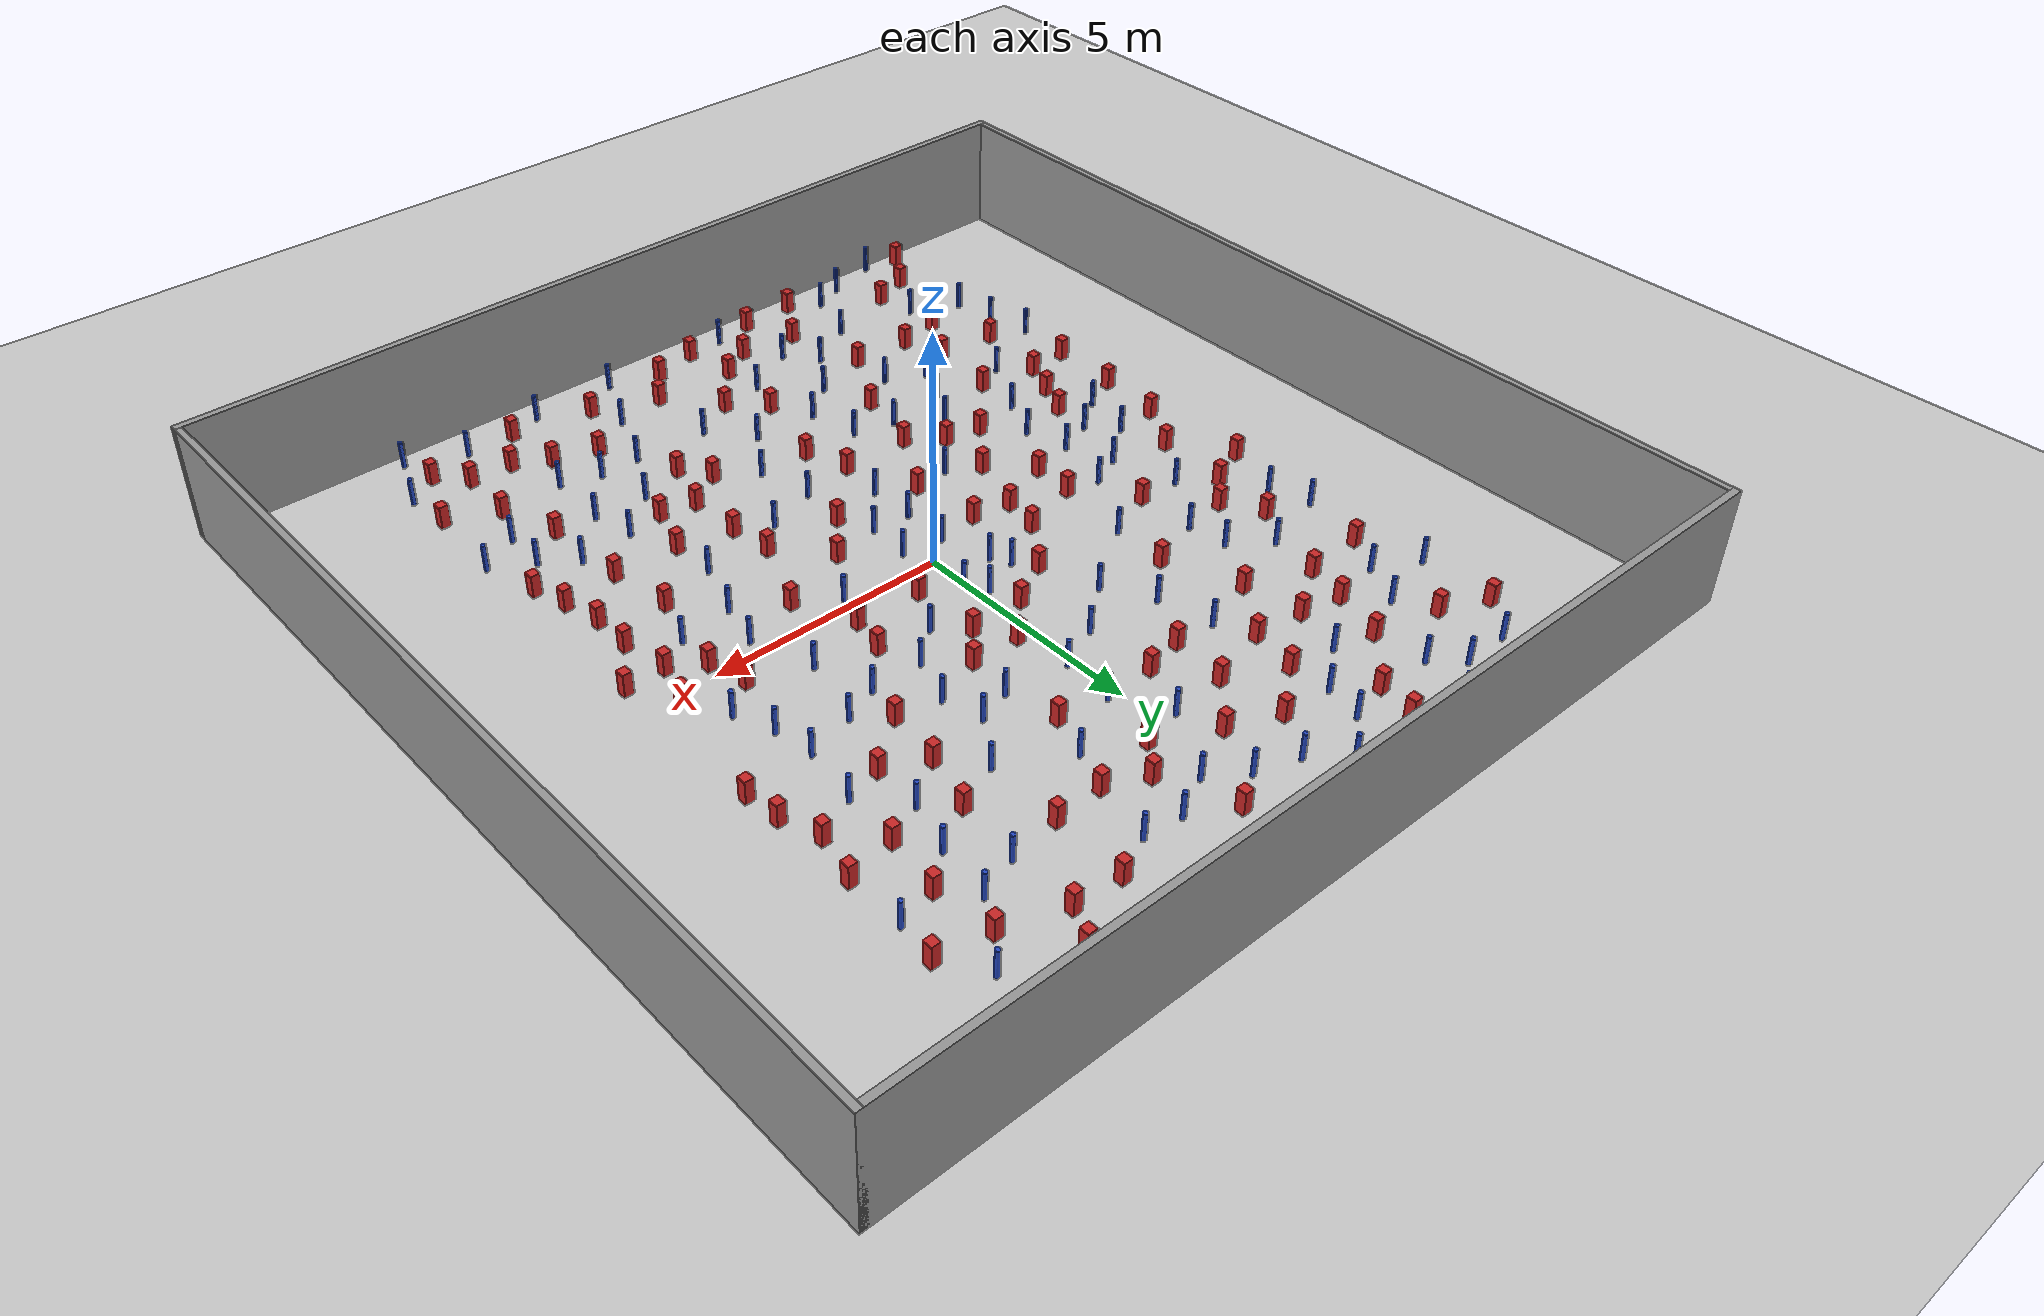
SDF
<sdf version="1.6">
 <world name="default">
  <light name="sun" type="directional">
   <pose>0 0 10 0 -0 0</pose>
   <diffuse>0.8 0.8 0.8 1</diffuse>
   <specular>0.1 0.1 0.1 1</specular>
   <attenuation>
    <range>1000</range>
    <constant>0.9</constant>
    <linear>0.01</linear>
    <quadratic>0.001</quadratic>
   </attenuation>
   <direction>-0.5 0.5 -1</direction>
  </light>
  <model name="ground_plane">
   <static>1</static>
   <link name="link">
    <collision name="collision">
     <geometry><plane><normal>0 0 1</normal><size>100 100</size></plane></geometry>
     <surface><friction><ode><mu>100</mu><mu2>50</mu2></ode></friction></surface>
    </collision>
    <visual name="visual">
     <cast_shadows>0</cast_shadows>
     <geometry><plane><normal>0 0 1</normal><size>100 100</size></plane></geometry>
     <material>
      <script><uri>file://media/materials/scripts/gazebo.material</uri><name>Gazebo/Grey</name></script>
     </material>
    </visual>
   </link>
  </model>
  <gravity>0 0 -9.8</gravity>
  <magnetic_field>6e-06 2.3e-05 -4.2e-05</magnetic_field>
  <atmosphere type="adiabatic"/>
  <physics name="default_physics" default="0" type="ode">
   <max_step_size>0.001</max_step_size>
   <real_time_factor>1</real_time_factor>
   <real_time_update_rate>1000</real_time_update_rate>
  </physics>
  <scene><ambient>0.4 0.4 0.4 1</ambient><background>0.7 0.7 0.7 1</background><shadows>1</shadows></scene>
  <spherical_coordinates>
   <surface_model>EARTH_WGS84</surface_model>
   <latitude_deg>0</latitude_deg>
   <longitude_deg>0</longitude_deg>
   <elevation>0</elevation>
   <heading_deg>0</heading_deg>
  </spherical_coordinates>
  <model name="20x20_walls">
   <pose>0.044518 0.1761 0 0 -0 0</pose>
   <link name="Wall_1">
    <collision name="Wall_1_Collision">
     <geometry><box><size>20 0.15 2.5</size></box></geometry>
     <pose>0 0 1.25 0 -0 0</pose>
    </collision>
    <visual name="Wall_1_Visual">
     <pose>0 0 1.25 0 -0 0</pose>
     <geometry><box><size>20 0.15 2.5</size></box></geometry>
     <material>
      <script><uri>file://media/materials/scripts/gazebo.material</uri><name>Gazebo/Grey</name></script>
      <ambient>0.976471 0.992157 1 1</ambient>
     </material>
     <meta><layer>0</layer></meta>
    </visual>
    <pose>0 9.925 0 0 -0 0</pose>
   </link>
   <link name="Wall_3">
    <collision name="Wall_3_Collision">
     <geometry><box><size>20 0.15 2.5</size></box></geometry>
     <pose>0 0 1.25 0 -0 0</pose>
    </collision>
    <visual name="Wall_3_Visual">
     <pose>0 0 1.25 0 -0 0</pose>
     <geometry><box><size>20 0.15 2.5</size></box></geometry>
     <material>
      <script><uri>file://media/materials/scripts/gazebo.material</uri><name>Gazebo/Grey</name></script>
      <ambient>0.976471 0.992157 1 1</ambient>
     </material>
     <meta><layer>0</layer></meta>
    </visual>
    <pose>9.925 0 0 0 0 -1.5708</pose>
   </link>
   <link name="Wall_4">
    <collision name="Wall_4_Collision">
     <geometry><box><size>20 0.15 2.5</size></box></geometry>
     <pose>0 0 1.25 0 -0 0</pose>
    </collision>
    <visual name="Wall_4_Visual">
     <pose>0 0 1.25 0 -0 0</pose>
     <geometry><box><size>20 0.15 2.5</size></box></geometry>
     <material>
      <script><uri>file://media/materials/scripts/gazebo.material</uri><name>Gazebo/Grey</name></script>
      <ambient>0.976471 0.992157 1 1</ambient>
     </material>
     <meta><layer>0</layer></meta>
    </visual>
    <pose>0 -9.925 0 0 -0 3.14159</pose>
   </link>
   <link name="Wall_5">
    <collision name="Wall_5_Collision">
     <geometry><box><size>20 0.15 2.5</size></box></geometry>
     <pose>0 0 1.25 0 -0 0</pose>
    </collision>
    <visual name="Wall_5_Visual">
     <pose>0 0 1.25 0 -0 0</pose>
     <geometry><box><size>20 0.15 2.5</size></box></geometry>
     <material>
      <script><uri>file://media/materials/scripts/gazebo.material</uri><name>Gazebo/Grey</name></script>
      <ambient>0.976471 0.992157 1 1</ambient>
     </material>
     <meta><layer>0</layer></meta>
    </visual>
    <pose>-9.925 0 0 0 -0 1.5708</pose>
   </link>
   <static>1</static>
  </model>
  <model name="square_post_obstacle0">
   <static>0</static>
   <link name="link">
    <pose>0 0 0.25 0 -0 0</pose>
    <inertial>
     <mass>100</mass>
     <inertia>
      <ixx>0.166667</ixx>
      <ixy>0</ixy>
      <ixz>0</ixz>
      <iyy>0.166667</iyy>
      <iyz>0</iyz>
      <izz>0.166667</izz>
     </inertia>
    </inertial>
    <collision name="collision"><geometry><box><size>0.2 0.2 0.5</size></box></geometry></collision>
    <visual name="visual">
     <geometry><box><size>0.2 0.2 0.5</size></box></geometry>
     <material>
      <script><name>Gazebo/Red</name><uri>file://media/materials/scripts/gazebo.material</uri></script>
     </material>
    </visual>
   </link>
   <pose>-6.057 0.183913 0 -4e-06 1e-06 -0.000299</pose>
  </model>
  <model name="pole_obstacle0">
   <static>0</static>
   <link name="link">
    <pose>0 0 0.3 0 -0 0</pose>
    <inertial>
     <mass>1</mass>
     <inertia><ixx>0.145833</ixx><ixy>0</ixy><ixz>0</ixz><iyy>0.145833</iyy><iyz>0</iyz><izz>0.125</izz></inertia>
    </inertial>
    <collision name="collision">
     <geometry><cylinder><radius>0.05</radius><length>0.6</length></cylinder></geometry>
    </collision>
    <visual name="visual">
     <geometry><cylinder><radius>0.05</radius><length>0.6</length></cylinder></geometry>
     <material>
      <script><name>Gazebo/Blue</name><uri>file://media/materials/scripts/gazebo.material</uri></script>
     </material>
    </visual>
   </link>
   <pose>-6.20952 8.3445 -5e-06 0 0 -2.4e-05</pose>
  </model>
  <model name="square_post_obstacle1">
   <static>0</static>
   <link name="link">
    <pose>0 0 0.25 0 -0 0</pose>
    <inertial>
     <mass>100</mass>
     <inertia>
      <ixx>0.166667</ixx>
      <ixy>0</ixy>
      <ixz>0</ixz>
      <iyy>0.166667</iyy>
      <iyz>0</iyz>
      <izz>0.166667</izz>
     </inertia>
    </inertial>
    <collision name="collision"><geometry><box><size>0.2 0.2 0.5</size></box></geometry></collision>
    <visual name="visual">
     <geometry><box><size>0.2 0.2 0.5</size></box></geometry>
     <material>
      <script><name>Gazebo/Red</name><uri>file://media/materials/scripts/gazebo.material</uri></script>
     </material>
    </visual>
   </link>
   <pose>-5.43486 -8.11833 0 -4e-06 1e-06 -0.000299</pose>
  </model>
  <model name="pole_obstacle1">
   <static>0</static>
   <link name="link">
    <pose>0 0 0.3 0 -0 0</pose>
    <inertial>
     <mass>1</mass>
     <inertia><ixx>0.145833</ixx><ixy>0</ixy><ixz>0</ixz><iyy>0.145833</iyy><iyz>0</iyz><izz>0.125</izz></inertia>
    </inertial>
    <collision name="collision">
     <geometry><cylinder><radius>0.05</radius><length>0.6</length></cylinder></geometry>
    </collision>
    <visual name="visual">
     <geometry><cylinder><radius>0.05</radius><length>0.6</length></cylinder></geometry>
     <material>
      <script><name>Gazebo/Blue</name><uri>file://media/materials/scripts/gazebo.material</uri></script>
     </material>
    </visual>
   </link>
   <pose>-1.56175 -4.29624 -5e-06 0 -0 2.8e-05</pose>
  </model>
  <model name="square_post_obstacle2">
   <static>0</static>
   <link name="link">
    <pose>0 0 0.25 0 -0 0</pose>
    <inertial>
     <mass>100</mass>
     <inertia>
      <ixx>0.166667</ixx>
      <ixy>0</ixy>
      <ixz>0</ixz>
      <iyy>0.166667</iyy>
      <iyz>0</iyz>
      <izz>0.166667</izz>
     </inertia>
    </inertial>
    <collision name="collision"><geometry><box><size>0.2 0.2 0.5</size></box></geometry></collision>
    <visual name="visual">
     <geometry><box><size>0.2 0.2 0.5</size></box></geometry>
     <material>
      <script><name>Gazebo/Red</name><uri>file://media/materials/scripts/gazebo.material</uri></script>
     </material>
    </visual>
   </link>
   <pose>-3.76358 4.37344 0 -4e-06 1e-06 -0.000299</pose>
  </model>
  <model name="square_post_obstacle3">
   <static>0</static>
   <link name="link">
    <pose>0 0 0.25 0 -0 0</pose>
    <inertial>
     <mass>100</mass>
     <inertia>
      <ixx>0.166667</ixx>
      <ixy>0</ixy>
      <ixz>0</ixz>
      <iyy>0.166667</iyy>
      <iyz>0</iyz>
      <izz>0.166667</izz>
     </inertia>
    </inertial>
    <collision name="collision"><geometry><box><size>0.2 0.2 0.5</size></box></geometry></collision>
    <visual name="visual">
     <geometry><box><size>0.2 0.2 0.5</size></box></geometry>
     <material>
      <script><name>Gazebo/Red</name><uri>file://media/materials/scripts/gazebo.material</uri></script>
     </material>
    </visual>
   </link>
   <pose>-4.34566 1.1971 0 -4e-06 1e-06 -0.000299</pose>
  </model>
  <model name="pole_obstacle2">
   <static>0</static>
   <link name="link">
    <pose>0 0 0.3 0 -0 0</pose>
    <inertial>
     <mass>1</mass>
     <inertia><ixx>0.145833</ixx><ixy>0</ixy><ixz>0</ixz><iyy>0.145833</iyy><iyz>0</iyz><izz>0.125</izz></inertia>
    </inertial>
    <collision name="collision">
     <geometry><cylinder><radius>0.05</radius><length>0.6</length></cylinder></geometry>
    </collision>
    <visual name="visual">
     <geometry><cylinder><radius>0.05</radius><length>0.6</length></cylinder></geometry>
     <material>
      <script><name>Gazebo/Blue</name><uri>file://media/materials/scripts/gazebo.material</uri></script>
     </material>
    </visual>
   </link>
   <pose>-4.2765 -2.01797 -5e-06 0 -0 1e-06</pose>
  </model>
  <model name="square_post_obstacle4">
   <static>0</static>
   <link name="link">
    <pose>0 0 0.25 0 -0 0</pose>
    <inertial>
     <mass>100</mass>
     <inertia>
      <ixx>0.166667</ixx>
      <ixy>0</ixy>
      <ixz>0</ixz>
      <iyy>0.166667</iyy>
      <iyz>0</iyz>
      <izz>0.166667</izz>
     </inertia>
    </inertial>
    <collision name="collision"><geometry><box><size>0.2 0.2 0.5</size></box></geometry></collision>
    <visual name="visual">
     <geometry><box><size>0.2 0.2 0.5</size></box></geometry>
     <material>
      <script><name>Gazebo/Red</name><uri>file://media/materials/scripts/gazebo.material</uri></script>
     </material>
    </visual>
   </link>
   <pose>-2.26076 -0.344597 0 -4e-06 1e-06 -0.000299</pose>
  </model>
  <model name="pole_obstacle3">
   <static>0</static>
   <link name="link">
    <pose>0 0 0.3 0 -0 0</pose>
    <inertial>
     <mass>1</mass>
     <inertia><ixx>0.145833</ixx><ixy>0</ixy><ixz>0</ixz><iyy>0.145833</iyy><iyz>0</iyz><izz>0.125</izz></inertia>
    </inertial>
    <collision name="collision">
     <geometry><cylinder><radius>0.05</radius><length>0.6</length></cylinder></geometry>
    </collision>
    <visual name="visual">
     <geometry><cylinder><radius>0.05</radius><length>0.6</length></cylinder></geometry>
     <material>
      <script><name>Gazebo/Blue</name><uri>file://media/materials/scripts/gazebo.material</uri></script>
     </material>
    </visual>
   </link>
   <pose>5.63583 -5.72954 -5e-06 0 0 -6.5e-05</pose>
  </model>
  <model name="square_post_obstacle5">
   <static>0</static>
   <link name="link">
    <pose>0 0 0.25 0 -0 0</pose>
    <inertial>
     <mass>100</mass>
     <inertia>
      <ixx>0.166667</ixx>
      <ixy>0</ixy>
      <ixz>0</ixz>
      <iyy>0.166667</iyy>
      <iyz>0</iyz>
      <izz>0.166667</izz>
     </inertia>
    </inertial>
    <collision name="collision"><geometry><box><size>0.2 0.2 0.5</size></box></geometry></collision>
    <visual name="visual">
     <geometry><box><size>0.2 0.2 0.5</size></box></geometry>
     <material>
      <script><name>Gazebo/Red</name><uri>file://media/materials/scripts/gazebo.material</uri></script>
     </material>
    </visual>
   </link>
   <pose>-3.60196 -9.20631 0 -4e-06 1e-06 -0.000299</pose>
  </model>
  <model name="pole_obstacle4">
   <static>0</static>
   <link name="link">
    <pose>0 0 0.3 0 -0 0</pose>
    <inertial>
     <mass>1</mass>
     <inertia><ixx>0.145833</ixx><ixy>0</ixy><ixz>0</ixz><iyy>0.145833</iyy><iyz>0</iyz><izz>0.125</izz></inertia>
    </inertial>
    <collision name="collision">
     <geometry><cylinder><radius>0.05</radius><length>0.6</length></cylinder></geometry>
    </collision>
    <visual name="visual">
     <geometry><cylinder><radius>0.05</radius><length>0.6</length></cylinder></geometry>
     <material>
      <script><name>Gazebo/Blue</name><uri>file://media/materials/scripts/gazebo.material</uri></script>
     </material>
    </visual>
   </link>
   <pose>0.473896 -3.21409 -5e-06 0 0 -1.9e-05</pose>
  </model>
  <model name="square_post_obstacle6">
   <static>0</static>
   <link name="link">
    <pose>0 0 0.25 0 -0 0</pose>
    <inertial>
     <mass>100</mass>
     <inertia>
      <ixx>0.166667</ixx>
      <ixy>0</ixy>
      <ixz>0</ixz>
      <iyy>0.166667</iyy>
      <iyz>0</iyz>
      <izz>0.166667</izz>
     </inertia>
    </inertial>
    <collision name="collision"><geometry><box><size>0.2 0.2 0.5</size></box></geometry></collision>
    <visual name="visual">
     <geometry><box><size>0.2 0.2 0.5</size></box></geometry>
     <material>
      <script><name>Gazebo/Red</name><uri>file://media/materials/scripts/gazebo.material</uri></script>
     </material>
    </visual>
   </link>
   <pose>5.26196 5.11522 0 -4e-06 1e-06 -0.000299</pose>
  </model>
  <model name="pole_obstacle5">
   <static>0</static>
   <link name="link">
    <pose>0 0 0.3 0 -0 0</pose>
    <inertial>
     <mass>1</mass>
     <inertia><ixx>0.145833</ixx><ixy>0</ixy><ixz>0</ixz><iyy>0.145833</iyy><iyz>0</iyz><izz>0.125</izz></inertia>
    </inertial>
    <collision name="collision">
     <geometry><cylinder><radius>0.05</radius><length>0.6</length></cylinder></geometry>
    </collision>
    <visual name="visual">
     <geometry><cylinder><radius>0.05</radius><length>0.6</length></cylinder></geometry>
     <material>
      <script><name>Gazebo/Blue</name><uri>file://media/materials/scripts/gazebo.material</uri></script>
     </material>
    </visual>
   </link>
   <pose>-3.27165 1.61809 -5e-06 0 -0 1.5e-05</pose>
  </model>
  <model name="pole_obstacle6">
   <static>0</static>
   <link name="link">
    <pose>0 0 0.3 0 -0 0</pose>
    <inertial>
     <mass>1</mass>
     <inertia><ixx>0.145833</ixx><ixy>0</ixy><ixz>0</ixz><iyy>0.145833</iyy><iyz>0</iyz><izz>0.125</izz></inertia>
    </inertial>
    <collision name="collision">
     <geometry><cylinder><radius>0.05</radius><length>0.6</length></cylinder></geometry>
    </collision>
    <visual name="visual">
     <geometry><cylinder><radius>0.05</radius><length>0.6</length></cylinder></geometry>
     <material>
      <script><name>Gazebo/Blue</name><uri>file://media/materials/scripts/gazebo.material</uri></script>
     </material>
    </visual>
   </link>
   <pose>2.18299 7.62151 -5e-06 0 0 -8e-06</pose>
  </model>
  <model name="pole_obstacle7">
   <static>0</static>
   <link name="link">
    <pose>0 0 0.3 0 -0 0</pose>
    <inertial>
     <mass>1</mass>
     <inertia><ixx>0.145833</ixx><ixy>0</ixy><ixz>0</ixz><iyy>0.145833</iyy><iyz>0</iyz><izz>0.125</izz></inertia>
    </inertial>
    <collision name="collision">
     <geometry><cylinder><radius>0.05</radius><length>0.6</length></cylinder></geometry>
    </collision>
    <visual name="visual">
     <geometry><cylinder><radius>0.05</radius><length>0.6</length></cylinder></geometry>
     <material>
      <script><name>Gazebo/Blue</name><uri>file://media/materials/scripts/gazebo.material</uri></script>
     </material>
    </visual>
   </link>
   <pose>2.45431 3.07016 -5e-06 0 0 -1.5e-05</pose>
  </model>
  <model name="pole_obstacle8">
   <static>0</static>
   <link name="link">
    <pose>0 0 0.3 0 -0 0</pose>
    <inertial>
     <mass>1</mass>
     <inertia><ixx>0.145833</ixx><ixy>0</ixy><ixz>0</ixz><iyy>0.145833</iyy><iyz>0</iyz><izz>0.125</izz></inertia>
    </inertial>
    <collision name="collision">
     <geometry><cylinder><radius>0.05</radius><length>0.6</length></cylinder></geometry>
    </collision>
    <visual name="visual">
     <geometry><cylinder><radius>0.05</radius><length>0.6</length></cylinder></geometry>
     <material>
      <script><name>Gazebo/Blue</name><uri>file://media/materials/scripts/gazebo.material</uri></script>
     </material>
    </visual>
   </link>
   <pose>1.52208 3.65928 -5e-06 0 -0 1e-05</pose>
  </model>
  <model name="pole_obstacle9">
   <static>0</static>
   <link name="link">
    <pose>0 0 0.3 0 -0 0</pose>
    <inertial>
     <mass>1</mass>
     <inertia><ixx>0.145833</ixx><ixy>0</ixy><ixz>0</ixz><iyy>0.145833</iyy><iyz>0</iyz><izz>0.125</izz></inertia>
    </inertial>
    <collision name="collision">
     <geometry><cylinder><radius>0.05</radius><length>0.6</length></cylinder></geometry>
    </collision>
    <visual name="visual">
     <geometry><cylinder><radius>0.05</radius><length>0.6</length></cylinder></geometry>
     <material>
      <script><name>Gazebo/Blue</name><uri>file://media/materials/scripts/gazebo.material</uri></script>
     </material>
    </visual>
   </link>
   <pose>-3.32276 -3.48487 -5e-06 0 -0 1.7e-05</pose>
  </model>
  <model name="pole_obstacle10">
   <static>0</static>
   <link name="link">
    <pose>0 0 0.3 0 -0 0</pose>
    <inertial>
     <mass>1</mass>
     <inertia><ixx>0.145833</ixx><ixy>0</ixy><ixz>0</ixz><iyy>0.145833</iyy><iyz>0</iyz><izz>0.125</izz></inertia>
    </inertial>
    <collision name="collision">
     <geometry><cylinder><radius>0.05</radius><length>0.6</length></cylinder></geometry>
    </collision>
    <visual name="visual">
     <geometry><cylinder><radius>0.05</radius><length>0.6</length></cylinder></geometry>
     <material>
      <script><name>Gazebo/Blue</name><uri>file://media/materials/scripts/gazebo.material</uri></script>
     </material>
    </visual>
   </link>
   <pose>4.03651 -5.31146 -5e-06 0 0 -3.6e-05</pose>
  </model>
  <model name="pole_obstacle11">
   <static>0</static>
   <link name="link">
    <pose>0 0 0.3 0 -0 0</pose>
    <inertial>
     <mass>1</mass>
     <inertia><ixx>0.145833</ixx><ixy>0</ixy><ixz>0</ixz><iyy>0.145833</iyy><iyz>0</iyz><izz>0.125</izz></inertia>
    </inertial>
    <collision name="collision">
     <geometry><cylinder><radius>0.05</radius><length>0.6</length></cylinder></geometry>
    </collision>
    <visual name="visual">
     <geometry><cylinder><radius>0.05</radius><length>0.6</length></cylinder></geometry>
     <material>
      <script><name>Gazebo/Blue</name><uri>file://media/materials/scripts/gazebo.material</uri></script>
     </material>
    </visual>
   </link>
   <pose>-2.13825 -6.03356 -5e-06 0 -0 3.5e-05</pose>
  </model>
  <model name="square_post_obstacle7">
   <static>0</static>
   <link name="link">
    <pose>0 0 0.25 0 -0 0</pose>
    <inertial>
     <mass>100</mass>
     <inertia>
      <ixx>0.166667</ixx>
      <ixy>0</ixy>
      <ixz>0</ixz>
      <iyy>0.166667</iyy>
      <iyz>0</iyz>
      <izz>0.166667</izz>
     </inertia>
    </inertial>
    <collision name="collision"><geometry><box><size>0.2 0.2 0.5</size></box></geometry></collision>
    <visual name="visual">
     <geometry><box><size>0.2 0.2 0.5</size></box></geometry>
     <material>
      <script><name>Gazebo/Red</name><uri>file://media/materials/scripts/gazebo.material</uri></script>
     </material>
    </visual>
   </link>
   <pose>-5.09435 4.88945 0 -4e-06 1e-06 -0.000299</pose>
  </model>
  <model name="pole_obstacle12">
   <static>0</static>
   <link name="link">
    <pose>0 0 0.3 0 -0 0</pose>
    <inertial>
     <mass>1</mass>
     <inertia><ixx>0.145833</ixx><ixy>0</ixy><ixz>0</ixz><iyy>0.145833</iyy><iyz>0</iyz><izz>0.125</izz></inertia>
    </inertial>
    <collision name="collision">
     <geometry><cylinder><radius>0.05</radius><length>0.6</length></cylinder></geometry>
    </collision>
    <visual name="visual">
     <geometry><cylinder><radius>0.05</radius><length>0.6</length></cylinder></geometry>
     <material>
      <script><name>Gazebo/Blue</name><uri>file://media/materials/scripts/gazebo.material</uri></script>
     </material>
    </visual>
   </link>
   <pose>3.95517 2.39756 -5e-06 0 -0 1.3e-05</pose>
  </model>
  <model name="square_post_obstacle8">
   <static>0</static>
   <link name="link">
    <pose>0 0 0.25 0 -0 0</pose>
    <inertial>
     <mass>100</mass>
     <inertia>
      <ixx>0.166667</ixx>
      <ixy>0</ixy>
      <ixz>0</ixz>
      <iyy>0.166667</iyy>
      <iyz>0</iyz>
      <izz>0.166667</izz>
     </inertia>
    </inertial>
    <collision name="collision"><geometry><box><size>0.2 0.2 0.5</size></box></geometry></collision>
    <visual name="visual">
     <geometry><box><size>0.2 0.2 0.5</size></box></geometry>
     <material>
      <script><name>Gazebo/Red</name><uri>file://media/materials/scripts/gazebo.material</uri></script>
     </material>
    </visual>
   </link>
   <pose>-3.47759 -0.826707 0 -4e-06 1e-06 -0.000299</pose>
  </model>
  <model name="square_post_obstacle9">
   <static>0</static>
   <link name="link">
    <pose>0 0 0.25 0 -0 0</pose>
    <inertial>
     <mass>100</mass>
     <inertia>
      <ixx>0.166667</ixx>
      <ixy>0</ixy>
      <ixz>0</ixz>
      <iyy>0.166667</iyy>
      <iyz>0</iyz>
      <izz>0.166667</izz>
     </inertia>
    </inertial>
    <collision name="collision"><geometry><box><size>0.2 0.2 0.5</size></box></geometry></collision>
    <visual name="visual">
     <geometry><box><size>0.2 0.2 0.5</size></box></geometry>
     <material>
      <script><name>Gazebo/Red</name><uri>file://media/materials/scripts/gazebo.material</uri></script>
     </material>
    </visual>
   </link>
   <pose>-2.89968 -8.10986 0 -4e-06 1e-06 -0.000299</pose>
  </model>
  <model name="pole_obstacle13">
   <static>0</static>
   <link name="link">
    <pose>0 0 0.3 0 -0 0</pose>
    <inertial>
     <mass>1</mass>
     <inertia><ixx>0.145833</ixx><ixy>0</ixy><ixz>0</ixz><iyy>0.145833</iyy><iyz>0</iyz><izz>0.125</izz></inertia>
    </inertial>
    <collision name="collision">
     <geometry><cylinder><radius>0.05</radius><length>0.6</length></cylinder></geometry>
    </collision>
    <visual name="visual">
     <geometry><cylinder><radius>0.05</radius><length>0.6</length></cylinder></geometry>
     <material>
      <script><name>Gazebo/Blue</name><uri>file://media/materials/scripts/gazebo.material</uri></script>
     </material>
    </visual>
   </link>
   <pose>1.98811 -0.198835 -5e-06 0 -0 2e-06</pose>
  </model>
  <model name="square_post_obstacle10">
   <static>0</static>
   <link name="link">
    <pose>0 0 0.25 0 -0 0</pose>
    <inertial>
     <mass>100</mass>
     <inertia>
      <ixx>0.166667</ixx>
      <ixy>0</ixy>
      <ixz>0</ixz>
      <iyy>0.166667</iyy>
      <iyz>0</iyz>
      <izz>0.166667</izz>
     </inertia>
    </inertial>
    <collision name="collision"><geometry><box><size>0.2 0.2 0.5</size></box></geometry></collision>
    <visual name="visual">
     <geometry><box><size>0.2 0.2 0.5</size></box></geometry>
     <material>
      <script><name>Gazebo/Red</name><uri>file://media/materials/scripts/gazebo.material</uri></script>
     </material>
    </visual>
   </link>
   <pose>2.82312 -0.687171 0 -4e-06 1e-06 -0.000299</pose>
  </model>
  <model name="pole_obstacle14">
   <static>0</static>
   <link name="link">
    <pose>0 0 0.3 0 -0 0</pose>
    <inertial>
     <mass>1</mass>
     <inertia><ixx>0.145833</ixx><ixy>0</ixy><ixz>0</ixz><iyy>0.145833</iyy><iyz>0</iyz><izz>0.125</izz></inertia>
    </inertial>
    <collision name="collision">
     <geometry><cylinder><radius>0.05</radius><length>0.6</length></cylinder></geometry>
    </collision>
    <visual name="visual">
     <geometry><cylinder><radius>0.05</radius><length>0.6</length></cylinder></geometry>
     <material>
      <script><name>Gazebo/Blue</name><uri>file://media/materials/scripts/gazebo.material</uri></script>
     </material>
    </visual>
   </link>
   <pose>-1.05503 1.01681 -5e-06 0 0 -1.4e-05</pose>
  </model>
  <model name="square_post_obstacle11">
   <static>0</static>
   <link name="link">
    <pose>0 0 0.25 0 -0 0</pose>
    <inertial>
     <mass>100</mass>
     <inertia>
      <ixx>0.166667</ixx>
      <ixy>0</ixy>
      <ixz>0</ixz>
      <iyy>0.166667</iyy>
      <iyz>0</iyz>
      <izz>0.166667</izz>
     </inertia>
    </inertial>
    <collision name="collision"><geometry><box><size>0.2 0.2 0.5</size></box></geometry></collision>
    <visual name="visual">
     <geometry><box><size>0.2 0.2 0.5</size></box></geometry>
     <material>
      <script><name>Gazebo/Red</name><uri>file://media/materials/scripts/gazebo.material</uri></script>
     </material>
    </visual>
   </link>
   <pose>-2.71039 -1.64454 0 -4e-06 1e-06 -0.000299</pose>
  </model>
  <model name="square_post_obstacle12">
   <static>0</static>
   <link name="link">
    <pose>0 0 0.25 0 -0 0</pose>
    <inertial>
     <mass>100</mass>
     <inertia>
      <ixx>0.166667</ixx>
      <ixy>0</ixy>
      <ixz>0</ixz>
      <iyy>0.166667</iyy>
      <iyz>0</iyz>
      <izz>0.166667</izz>
     </inertia>
    </inertial>
    <collision name="collision"><geometry><box><size>0.2 0.2 0.5</size></box></geometry></collision>
    <visual name="visual">
     <geometry><box><size>0.2 0.2 0.5</size></box></geometry>
     <material>
      <script><name>Gazebo/Red</name><uri>file://media/materials/scripts/gazebo.material</uri></script>
     </material>
    </visual>
   </link>
   <pose>-0.833716 -6.15632 0 -4e-06 1e-06 -0.000299</pose>
  </model>
  <model name="pole_obstacle15">
   <static>0</static>
   <link name="link">
    <pose>0 0 0.3 0 -0 0</pose>
    <inertial>
     <mass>1</mass>
     <inertia><ixx>0.145833</ixx><ixy>0</ixy><ixz>0</ixz><iyy>0.145833</iyy><iyz>0</iyz><izz>0.125</izz></inertia>
    </inertial>
    <collision name="collision">
     <geometry><cylinder><radius>0.05</radius><length>0.6</length></cylinder></geometry>
    </collision>
    <visual name="visual">
     <geometry><cylinder><radius>0.05</radius><length>0.6</length></cylinder></geometry>
     <material>
      <script><name>Gazebo/Blue</name><uri>file://media/materials/scripts/gazebo.material</uri></script>
     </material>
    </visual>
   </link>
   <pose>-4.40507 8.88915 -5e-06 0 -0 2.1e-05</pose>
  </model>
  <model name="square_post_obstacle13">
   <static>0</static>
   <link name="link">
    <pose>0 0 0.25 0 -0 0</pose>
    <inertial>
     <mass>100</mass>
     <inertia>
      <ixx>0.166667</ixx>
      <ixy>0</ixy>
      <ixz>0</ixz>
      <iyy>0.166667</iyy>
      <iyz>0</iyz>
      <izz>0.166667</izz>
     </inertia>
    </inertial>
    <collision name="collision"><geometry><box><size>0.2 0.2 0.5</size></box></geometry></collision>
    <visual name="visual">
     <geometry><box><size>0.2 0.2 0.5</size></box></geometry>
     <material>
      <script><name>Gazebo/Red</name><uri>file://media/materials/scripts/gazebo.material</uri></script>
     </material>
    </visual>
   </link>
   <pose>-1.67024 7.18728 0 -4e-06 1e-06 -0.000299</pose>
  </model>
  <model name="square_post_obstacle14">
   <static>0</static>
   <link name="link">
    <pose>0 0 0.25 0 -0 0</pose>
    <inertial>
     <mass>100</mass>
     <inertia>
      <ixx>0.166667</ixx>
      <ixy>0</ixy>
      <ixz>0</ixz>
      <iyy>0.166667</iyy>
      <iyz>0</iyz>
      <izz>0.166667</izz>
     </inertia>
    </inertial>
    <collision name="collision"><geometry><box><size>0.2 0.2 0.5</size></box></geometry></collision>
    <visual name="visual">
     <geometry><box><size>0.2 0.2 0.5</size></box></geometry>
     <material>
      <script><name>Gazebo/Red</name><uri>file://media/materials/scripts/gazebo.material</uri></script>
     </material>
    </visual>
   </link>
   <pose>-5.35035 2.31245 0 -4e-06 1e-06 -0.000299</pose>
  </model>
  <model name="pole_obstacle16">
   <static>0</static>
   <link name="link">
    <pose>0 0 0.3 0 -0 0</pose>
    <inertial>
     <mass>1</mass>
     <inertia><ixx>0.145833</ixx><ixy>0</ixy><ixz>0</ixz><iyy>0.145833</iyy><iyz>0</iyz><izz>0.125</izz></inertia>
    </inertial>
    <collision name="collision">
     <geometry><cylinder><radius>0.05</radius><length>0.6</length></cylinder></geometry>
    </collision>
    <visual name="visual">
     <geometry><cylinder><radius>0.05</radius><length>0.6</length></cylinder></geometry>
     <material>
      <script><name>Gazebo/Blue</name><uri>file://media/materials/scripts/gazebo.material</uri></script>
     </material>
    </visual>
   </link>
   <pose>0.024837 -5.471 -5e-06 0 0 -5.9e-05</pose>
  </model>
  <model name="square_post_obstacle15">
   <static>0</static>
   <link name="link">
    <pose>0 0 0.25 0 -0 0</pose>
    <inertial>
     <mass>100</mass>
     <inertia>
      <ixx>0.166667</ixx>
      <ixy>0</ixy>
      <ixz>0</ixz>
      <iyy>0.166667</iyy>
      <iyz>0</iyz>
      <izz>0.166667</izz>
     </inertia>
    </inertial>
    <collision name="collision"><geometry><box><size>0.2 0.2 0.5</size></box></geometry></collision>
    <visual name="visual">
     <geometry><box><size>0.2 0.2 0.5</size></box></geometry>
     <material>
      <script><name>Gazebo/Red</name><uri>file://media/materials/scripts/gazebo.material</uri></script>
     </material>
    </visual>
   </link>
   <pose>-0.346076 9.31122 0 -4e-06 1e-06 -0.000299</pose>
  </model>
  <model name="square_post_obstacle16">
   <static>0</static>
   <link name="link">
    <pose>0 0 0.25 0 -0 0</pose>
    <inertial>
     <mass>100</mass>
     <inertia>
      <ixx>0.166667</ixx>
      <ixy>0</ixy>
      <ixz>0</ixz>
      <iyy>0.166667</iyy>
      <iyz>0</iyz>
      <izz>0.166667</izz>
     </inertia>
    </inertial>
    <collision name="collision"><geometry><box><size>0.2 0.2 0.5</size></box></geometry></collision>
    <visual name="visual">
     <geometry><box><size>0.2 0.2 0.5</size></box></geometry>
     <material>
      <script><name>Gazebo/Red</name><uri>file://media/materials/scripts/gazebo.material</uri></script>
     </material>
    </visual>
   </link>
   <pose>6.39479 2.78555 0 -4e-06 1e-06 -0.000299</pose>
  </model>
  <model name="pole_obstacle17">
   <static>0</static>
   <link name="link">
    <pose>0 0 0.3 0 -0 0</pose>
    <inertial>
     <mass>1</mass>
     <inertia><ixx>0.145833</ixx><ixy>0</ixy><ixz>0</ixz><iyy>0.145833</iyy><iyz>0</iyz><izz>0.125</izz></inertia>
    </inertial>
    <collision name="collision">
     <geometry><cylinder><radius>0.05</radius><length>0.6</length></cylinder></geometry>
    </collision>
    <visual name="visual">
     <geometry><cylinder><radius>0.05</radius><length>0.6</length></cylinder></geometry>
     <material>
      <script><name>Gazebo/Blue</name><uri>file://media/materials/scripts/gazebo.material</uri></script>
     </material>
    </visual>
   </link>
   <pose>-5.99466 5.53293 -5e-06 0 0 -6.5e-05</pose>
  </model>
  <model name="pole_obstacle18">
   <static>0</static>
   <link name="link">
    <pose>0 0 0.3 0 -0 0</pose>
    <inertial>
     <mass>1</mass>
     <inertia><ixx>0.145833</ixx><ixy>0</ixy><ixz>0</ixz><iyy>0.145833</iyy><iyz>0</iyz><izz>0.125</izz></inertia>
    </inertial>
    <collision name="collision">
     <geometry><cylinder><radius>0.05</radius><length>0.6</length></cylinder></geometry>
    </collision>
    <visual name="visual">
     <geometry><cylinder><radius>0.05</radius><length>0.6</length></cylinder></geometry>
     <material>
      <script><name>Gazebo/Blue</name><uri>file://media/materials/scripts/gazebo.material</uri></script>
     </material>
    </visual>
   </link>
   <pose>0.723135 -4.39332 -5e-06 0 0 -5.4e-05</pose>
  </model>
  <model name="square_post_obstacle17">
   <static>0</static>
   <link name="link">
    <pose>0 0 0.25 0 -0 0</pose>
    <inertial>
     <mass>100</mass>
     <inertia>
      <ixx>0.166667</ixx>
      <ixy>0</ixy>
      <ixz>0</ixz>
      <iyy>0.166667</iyy>
      <iyz>0</iyz>
      <izz>0.166667</izz>
     </inertia>
    </inertial>
    <collision name="collision"><geometry><box><size>0.2 0.2 0.5</size></box></geometry></collision>
    <visual name="visual">
     <geometry><box><size>0.2 0.2 0.5</size></box></geometry>
     <material>
      <script><name>Gazebo/Red</name><uri>file://media/materials/scripts/gazebo.material</uri></script>
     </material>
    </visual>
   </link>
   <pose>-5.96872 -3.64636 0 -4e-06 1e-06 -0.000299</pose>
  </model>
  <model name="square_post_obstacle18">
   <static>0</static>
   <link name="link">
    <pose>0 0 0.25 0 -0 0</pose>
    <inertial>
     <mass>100</mass>
     <inertia>
      <ixx>0.166667</ixx>
      <ixy>0</ixy>
      <ixz>0</ixz>
      <iyy>0.166667</iyy>
      <iyz>0</iyz>
      <izz>0.166667</izz>
     </inertia>
    </inertial>
    <collision name="collision"><geometry><box><size>0.2 0.2 0.5</size></box></geometry></collision>
    <visual name="visual">
     <geometry><box><size>0.2 0.2 0.5</size></box></geometry>
     <material>
      <script><name>Gazebo/Red</name><uri>file://media/materials/scripts/gazebo.material</uri></script>
     </material>
    </visual>
   </link>
   <pose>5.32556 -6.58024 0 -4e-06 1e-06 -0.000299</pose>
  </model>
  <model name="pole_obstacle19">
   <static>0</static>
   <link name="link">
    <pose>0 0 0.3 0 -0 0</pose>
    <inertial>
     <mass>1</mass>
     <inertia><ixx>0.145833</ixx><ixy>0</ixy><ixz>0</ixz><iyy>0.145833</iyy><iyz>0</iyz><izz>0.125</izz></inertia>
    </inertial>
    <collision name="collision">
     <geometry><cylinder><radius>0.05</radius><length>0.6</length></cylinder></geometry>
    </collision>
    <visual name="visual">
     <geometry><cylinder><radius>0.05</radius><length>0.6</length></cylinder></geometry>
     <material>
      <script><name>Gazebo/Blue</name><uri>file://media/materials/scripts/gazebo.material</uri></script>
     </material>
    </visual>
   </link>
   <pose>-0.563974 -2.40834 -5e-06 0 -0 6e-06</pose>
  </model>
  <model name="pole_obstacle20">
   <static>0</static>
   <link name="link">
    <pose>0 0 0.3 0 -0 0</pose>
    <inertial>
     <mass>1</mass>
     <inertia><ixx>0.145833</ixx><ixy>0</ixy><ixz>0</ixz><iyy>0.145833</iyy><iyz>0</iyz><izz>0.125</izz></inertia>
    </inertial>
    <collision name="collision">
     <geometry><cylinder><radius>0.05</radius><length>0.6</length></cylinder></geometry>
    </collision>
    <visual name="visual">
     <geometry><cylinder><radius>0.05</radius><length>0.6</length></cylinder></geometry>
     <material>
      <script><name>Gazebo/Blue</name><uri>file://media/materials/scripts/gazebo.material</uri></script>
     </material>
    </visual>
   </link>
   <pose>3.57013 0.94303 -5e-06 0 -0 2e-06</pose>
  </model>
  <model name="pole_obstacle21">
   <static>0</static>
   <link name="link">
    <pose>0 0 0.3 0 -0 0</pose>
    <inertial>
     <mass>1</mass>
     <inertia><ixx>0.145833</ixx><ixy>0</ixy><ixz>0</ixz><iyy>0.145833</iyy><iyz>0</iyz><izz>0.125</izz></inertia>
    </inertial>
    <collision name="collision">
     <geometry><cylinder><radius>0.05</radius><length>0.6</length></cylinder></geometry>
    </collision>
    <visual name="visual">
     <geometry><cylinder><radius>0.05</radius><length>0.6</length></cylinder></geometry>
     <material>
      <script><name>Gazebo/Blue</name><uri>file://media/materials/scripts/gazebo.material</uri></script>
     </material>
    </visual>
   </link>
   <pose>-6.75724 3.41665 -5e-06 0 0 -2e-06</pose>
  </model>
  <model name="square_post_obstacle19">
   <static>0</static>
   <link name="link">
    <pose>0 0 0.25 0 -0 0</pose>
    <inertial>
     <mass>100</mass>
     <inertia>
      <ixx>0.166667</ixx>
      <ixy>0</ixy>
      <ixz>0</ixz>
      <iyy>0.166667</iyy>
      <iyz>0</iyz>
      <izz>0.166667</izz>
     </inertia>
    </inertial>
    <collision name="collision"><geometry><box><size>0.2 0.2 0.5</size></box></geometry></collision>
    <visual name="visual">
     <geometry><box><size>0.2 0.2 0.5</size></box></geometry>
     <material>
      <script><name>Gazebo/Red</name><uri>file://media/materials/scripts/gazebo.material</uri></script>
     </material>
    </visual>
   </link>
   <pose>-1.44666 -0.499344 0 -4e-06 1e-06 -0.000299</pose>
  </model>
  <model name="square_post_obstacle20">
   <static>0</static>
   <link name="link">
    <pose>0 0 0.25 0 -0 0</pose>
    <inertial>
     <mass>100</mass>
     <inertia>
      <ixx>0.166667</ixx>
      <ixy>0</ixy>
      <ixz>0</ixz>
      <iyy>0.166667</iyy>
      <iyz>0</iyz>
      <izz>0.166667</izz>
     </inertia>
    </inertial>
    <collision name="collision"><geometry><box><size>0.2 0.2 0.5</size></box></geometry></collision>
    <visual name="visual">
     <geometry><box><size>0.2 0.2 0.5</size></box></geometry>
     <material>
      <script><name>Gazebo/Red</name><uri>file://media/materials/scripts/gazebo.material</uri></script>
     </material>
    </visual>
   </link>
   <pose>-2.49949 -4.89652 0 -4e-06 1e-06 -0.000299</pose>
  </model>
  <model name="pole_obstacle22">
   <static>0</static>
   <link name="link">
    <pose>0 0 0.3 0 -0 0</pose>
    <inertial>
     <mass>1</mass>
     <inertia><ixx>0.145833</ixx><ixy>0</ixy><ixz>0</ixz><iyy>0.145833</iyy><iyz>0</iyz><izz>0.125</izz></inertia>
    </inertial>
    <collision name="collision">
     <geometry><cylinder><radius>0.05</radius><length>0.6</length></cylinder></geometry>
    </collision>
    <visual name="visual">
     <geometry><cylinder><radius>0.05</radius><length>0.6</length></cylinder></geometry>
     <material>
      <script><name>Gazebo/Blue</name><uri>file://media/materials/scripts/gazebo.material</uri></script>
     </material>
    </visual>
   </link>
   <pose>6.45357 -8.04953 -5e-06 0 0 -4.9e-05</pose>
  </model>
  <model name="square_post_obstacle21">
   <static>0</static>
   <link name="link">
    <pose>0 0 0.25 0 -0 0</pose>
    <inertial>
     <mass>100</mass>
     <inertia>
      <ixx>0.166667</ixx>
      <ixy>0</ixy>
      <ixz>0</ixz>
      <iyy>0.166667</iyy>
      <iyz>0</iyz>
      <izz>0.166667</izz>
     </inertia>
    </inertial>
    <collision name="collision"><geometry><box><size>0.2 0.2 0.5</size></box></geometry></collision>
    <visual name="visual">
     <geometry><box><size>0.2 0.2 0.5</size></box></geometry>
     <material>
      <script><name>Gazebo/Red</name><uri>file://media/materials/scripts/gazebo.material</uri></script>
     </material>
    </visual>
   </link>
   <pose>6.29388 5.31356 0 -4e-06 1e-06 -0.000299</pose>
  </model>
  <model name="pole_obstacle23">
   <static>0</static>
   <link name="link">
    <pose>0 0 0.3 0 -0 0</pose>
    <inertial>
     <mass>1</mass>
     <inertia><ixx>0.145833</ixx><ixy>0</ixy><ixz>0</ixz><iyy>0.145833</iyy><iyz>0</iyz><izz>0.125</izz></inertia>
    </inertial>
    <collision name="collision">
     <geometry><cylinder><radius>0.05</radius><length>0.6</length></cylinder></geometry>
    </collision>
    <visual name="visual">
     <geometry><cylinder><radius>0.05</radius><length>0.6</length></cylinder></geometry>
     <material>
      <script><name>Gazebo/Blue</name><uri>file://media/materials/scripts/gazebo.material</uri></script>
     </material>
    </visual>
   </link>
   <pose>0.292143 -0.538105 -5e-06 0 0 -7.8e-05</pose>
  </model>
  <model name="square_post_obstacle22">
   <static>0</static>
   <link name="link">
    <pose>0 0 0.25 0 -0 0</pose>
    <inertial>
     <mass>100</mass>
     <inertia>
      <ixx>0.166667</ixx>
      <ixy>0</ixy>
      <ixz>0</ixz>
      <iyy>0.166667</iyy>
      <iyz>0</iyz>
      <izz>0.166667</izz>
     </inertia>
    </inertial>
    <collision name="collision"><geometry><box><size>0.2 0.2 0.5</size></box></geometry></collision>
    <visual name="visual">
     <geometry><box><size>0.2 0.2 0.5</size></box></geometry>
     <material>
      <script><name>Gazebo/Red</name><uri>file://media/materials/scripts/gazebo.material</uri></script>
     </material>
    </visual>
   </link>
   <pose>1.95897 9.23439 0 -4e-06 1e-06 -0.000299</pose>
  </model>
  <model name="pole_obstacle24">
   <static>0</static>
   <link name="link">
    <pose>0 0 0.3 0 -0 0</pose>
    <inertial>
     <mass>1</mass>
     <inertia><ixx>0.145833</ixx><ixy>0</ixy><ixz>0</ixz><iyy>0.145833</iyy><iyz>0</iyz><izz>0.125</izz></inertia>
    </inertial>
    <collision name="collision">
     <geometry><cylinder><radius>0.05</radius><length>0.6</length></cylinder></geometry>
    </collision>
    <visual name="visual">
     <geometry><cylinder><radius>0.05</radius><length>0.6</length></cylinder></geometry>
     <material>
      <script><name>Gazebo/Blue</name><uri>file://media/materials/scripts/gazebo.material</uri></script>
     </material>
    </visual>
   </link>
   <pose>2.93959 4.86071 -5e-06 0 0 -8e-06</pose>
  </model>
  <model name="square_post_obstacle23">
   <static>0</static>
   <link name="link">
    <pose>0 0 0.25 0 -0 0</pose>
    <inertial>
     <mass>100</mass>
     <inertia>
      <ixx>0.166667</ixx>
      <ixy>0</ixy>
      <ixz>0</ixz>
      <iyy>0.166667</iyy>
      <iyz>0</iyz>
      <izz>0.166667</izz>
     </inertia>
    </inertial>
    <collision name="collision"><geometry><box><size>0.2 0.2 0.5</size></box></geometry></collision>
    <visual name="visual">
     <geometry><box><size>0.2 0.2 0.5</size></box></geometry>
     <material>
      <script><name>Gazebo/Red</name><uri>file://media/materials/scripts/gazebo.material</uri></script>
     </material>
    </visual>
   </link>
   <pose>4.95141 -0.267317 0 -4e-06 1e-06 -0.000299</pose>
  </model>
  <model name="pole_obstacle25">
   <static>0</static>
   <link name="link">
    <pose>0 0 0.3 0 -0 0</pose>
    <inertial>
     <mass>1</mass>
     <inertia><ixx>0.145833</ixx><ixy>0</ixy><ixz>0</ixz><iyy>0.145833</iyy><iyz>0</iyz><izz>0.125</izz></inertia>
    </inertial>
    <collision name="collision">
     <geometry><cylinder><radius>0.05</radius><length>0.6</length></cylinder></geometry>
    </collision>
    <visual name="visual">
     <geometry><cylinder><radius>0.05</radius><length>0.6</length></cylinder></geometry>
     <material>
      <script><name>Gazebo/Blue</name><uri>file://media/materials/scripts/gazebo.material</uri></script>
     </material>
    </visual>
   </link>
   <pose>-4.88508 -0.141023 -5e-06 0 -0 0</pose>
  </model>
  <model name="pole_obstacle26">
   <static>0</static>
   <link name="link">
    <pose>0 0 0.3 0 -0 0</pose>
    <inertial>
     <mass>1</mass>
     <inertia><ixx>0.145833</ixx><ixy>0</ixy><ixz>0</ixz><iyy>0.145833</iyy><iyz>0</iyz><izz>0.125</izz></inertia>
    </inertial>
    <collision name="collision">
     <geometry><cylinder><radius>0.05</radius><length>0.6</length></cylinder></geometry>
    </collision>
    <visual name="visual">
     <geometry><cylinder><radius>0.05</radius><length>0.6</length></cylinder></geometry>
     <material>
      <script><name>Gazebo/Blue</name><uri>file://media/materials/scripts/gazebo.material</uri></script>
     </material>
    </visual>
   </link>
   <pose>4.91337 -1.1411 -5e-06 0 0 -5.7e-05</pose>
  </model>
  <model name="pole_obstacle27">
   <static>0</static>
   <link name="link">
    <pose>0 0 0.3 0 -0 0</pose>
    <inertial>
     <mass>1</mass>
     <inertia><ixx>0.145833</ixx><ixy>0</ixy><ixz>0</ixz><iyy>0.145833</iyy><iyz>0</iyz><izz>0.125</izz></inertia>
    </inertial>
    <collision name="collision">
     <geometry><cylinder><radius>0.05</radius><length>0.6</length></cylinder></geometry>
    </collision>
    <visual name="visual">
     <geometry><cylinder><radius>0.05</radius><length>0.6</length></cylinder></geometry>
     <material>
      <script><name>Gazebo/Blue</name><uri>file://media/materials/scripts/gazebo.material</uri></script>
     </material>
    </visual>
   </link>
   <pose>0.235479 -1.47166 -5e-06 0 -0 1e-06</pose>
  </model>
  <model name="pole_obstacle28">
   <static>0</static>
   <link name="link">
    <pose>0 0 0.3 0 -0 0</pose>
    <inertial>
     <mass>1</mass>
     <inertia><ixx>0.145833</ixx><ixy>0</ixy><ixz>0</ixz><iyy>0.145833</iyy><iyz>0</iyz><izz>0.125</izz></inertia>
    </inertial>
    <collision name="collision">
     <geometry><cylinder><radius>0.05</radius><length>0.6</length></cylinder></geometry>
    </collision>
    <visual name="visual">
     <geometry><cylinder><radius>0.05</radius><length>0.6</length></cylinder></geometry>
     <material>
      <script><name>Gazebo/Blue</name><uri>file://media/materials/scripts/gazebo.material</uri></script>
     </material>
    </visual>
   </link>
   <pose>4.97068 2.67329 -5e-06 0 -0 1e-05</pose>
  </model>
  <model name="square_post_obstacle24">
   <static>0</static>
   <link name="link">
    <pose>0 0 0.25 0 -0 0</pose>
    <inertial>
     <mass>100</mass>
     <inertia>
      <ixx>0.166667</ixx>
      <ixy>0</ixy>
      <ixz>0</ixz>
      <iyy>0.166667</iyy>
      <iyz>0</iyz>
      <izz>0.166667</izz>
     </inertia>
    </inertial>
    <collision name="collision"><geometry><box><size>0.2 0.2 0.5</size></box></geometry></collision>
    <visual name="visual">
     <geometry><box><size>0.2 0.2 0.5</size></box></geometry>
     <material>
      <script><name>Gazebo/Red</name><uri>file://media/materials/scripts/gazebo.material</uri></script>
     </material>
    </visual>
   </link>
   <pose>-6.8776 -3.72016 0 -4e-06 1e-06 -0.000299</pose>
  </model>
  <model name="square_post_obstacle25">
   <static>0</static>
   <link name="link">
    <pose>0 0 0.25 0 -0 0</pose>
    <inertial>
     <mass>100</mass>
     <inertia>
      <ixx>0.166667</ixx>
      <ixy>0</ixy>
      <ixz>0</ixz>
      <iyy>0.166667</iyy>
      <iyz>0</iyz>
      <izz>0.166667</izz>
     </inertia>
    </inertial>
    <collision name="collision"><geometry><box><size>0.2 0.2 0.5</size></box></geometry></collision>
    <visual name="visual">
     <geometry><box><size>0.2 0.2 0.5</size></box></geometry>
     <material>
      <script><name>Gazebo/Red</name><uri>file://media/materials/scripts/gazebo.material</uri></script>
     </material>
    </visual>
   </link>
   <pose>4.36926 -7.84441 0 -4e-06 1e-06 -0.000299</pose>
  </model>
  <model name="pole_obstacle29">
   <static>0</static>
   <link name="link">
    <pose>0 0 0.3 0 -0 0</pose>
    <inertial>
     <mass>1</mass>
     <inertia><ixx>0.145833</ixx><ixy>0</ixy><ixz>0</ixz><iyy>0.145833</iyy><iyz>0</iyz><izz>0.125</izz></inertia>
    </inertial>
    <collision name="collision">
     <geometry><cylinder><radius>0.05</radius><length>0.6</length></cylinder></geometry>
    </collision>
    <visual name="visual">
     <geometry><cylinder><radius>0.05</radius><length>0.6</length></cylinder></geometry>
     <material>
      <script><name>Gazebo/Blue</name><uri>file://media/materials/scripts/gazebo.material</uri></script>
     </material>
    </visual>
   </link>
   <pose>4.98197 -4.29209 -4e-06 0 0 -6.7e-05</pose>
  </model>
  <model name="square_post_obstacle26">
   <static>0</static>
   <link name="link">
    <pose>0 0 0.25 0 -0 0</pose>
    <inertial>
     <mass>100</mass>
     <inertia>
      <ixx>0.166667</ixx>
      <ixy>0</ixy>
      <ixz>0</ixz>
      <iyy>0.166667</iyy>
      <iyz>0</iyz>
      <izz>0.166667</izz>
     </inertia>
    </inertial>
    <collision name="collision"><geometry><box><size>0.2 0.2 0.5</size></box></geometry></collision>
    <visual name="visual">
     <geometry><box><size>0.2 0.2 0.5</size></box></geometry>
     <material>
      <script><name>Gazebo/Red</name><uri>file://media/materials/scripts/gazebo.material</uri></script>
     </material>
    </visual>
   </link>
   <pose>4.68687 9.44771 0 -4e-06 1e-06 -0.000299</pose>
  </model>
  <model name="square_post_obstacle27">
   <static>0</static>
   <link name="link">
    <pose>0 0 0.25 0 -0 0</pose>
    <inertial>
     <mass>100</mass>
     <inertia>
      <ixx>0.166667</ixx>
      <ixy>0</ixy>
      <ixz>0</ixz>
      <iyy>0.166667</iyy>
      <iyz>0</iyz>
      <izz>0.166667</izz>
     </inertia>
    </inertial>
    <collision name="collision"><geometry><box><size>0.2 0.2 0.5</size></box></geometry></collision>
    <visual name="visual">
     <geometry><box><size>0.2 0.2 0.5</size></box></geometry>
     <material>
      <script><name>Gazebo/Red</name><uri>file://media/materials/scripts/gazebo.material</uri></script>
     </material>
    </visual>
   </link>
   <pose>2.17804 -2.25755 0 -4e-06 1e-06 -0.000299</pose>
  </model>
  <model name="square_post_obstacle28">
   <static>0</static>
   <link name="link">
    <pose>0 0 0.25 0 -0 0</pose>
    <inertial>
     <mass>100</mass>
     <inertia>
      <ixx>0.166667</ixx>
      <ixy>0</ixy>
      <ixz>0</ixz>
      <iyy>0.166667</iyy>
      <iyz>0</iyz>
      <izz>0.166667</izz>
     </inertia>
    </inertial>
    <collision name="collision"><geometry><box><size>0.2 0.2 0.5</size></box></geometry></collision>
    <visual name="visual">
     <geometry><box><size>0.2 0.2 0.5</size></box></geometry>
     <material>
      <script><name>Gazebo/Red</name><uri>file://media/materials/scripts/gazebo.material</uri></script>
     </material>
    </visual>
   </link>
   <pose>4.45696 8.67659 0 -4e-06 1e-06 -0.000299</pose>
  </model>
  <model name="square_post_obstacle29">
   <static>0</static>
   <link name="link">
    <pose>0 0 0.25 0 -0 0</pose>
    <inertial>
     <mass>100</mass>
     <inertia>
      <ixx>0.166667</ixx>
      <ixy>0</ixy>
      <ixz>0</ixz>
      <iyy>0.166667</iyy>
      <iyz>0</iyz>
      <izz>0.166667</izz>
     </inertia>
    </inertial>
    <collision name="collision"><geometry><box><size>0.2 0.2 0.5</size></box></geometry></collision>
    <visual name="visual">
     <geometry><box><size>0.2 0.2 0.5</size></box></geometry>
     <material>
      <script><name>Gazebo/Red</name><uri>file://media/materials/scripts/gazebo.material</uri></script>
     </material>
    </visual>
   </link>
   <pose>0.372643 2.73219 0 -4e-06 1e-06 -0.000299</pose>
  </model>
  <model name="square_post_obstacle30">
   <static>0</static>
   <link name="link">
    <pose>0 0 0.25 0 -0 0</pose>
    <inertial>
     <mass>100</mass>
     <inertia>
      <ixx>0.166667</ixx>
      <ixy>0</ixy>
      <ixz>0</ixz>
      <iyy>0.166667</iyy>
      <iyz>0</iyz>
      <izz>0.166667</izz>
     </inertia>
    </inertial>
    <collision name="collision"><geometry><box><size>0.2 0.2 0.5</size></box></geometry></collision>
    <visual name="visual">
     <geometry><box><size>0.2 0.2 0.5</size></box></geometry>
     <material>
      <script><name>Gazebo/Red</name><uri>file://media/materials/scripts/gazebo.material</uri></script>
     </material>
    </visual>
   </link>
   <pose>-4.61162 -6.2922 0 -4e-06 1e-06 -0.000299</pose>
  </model>
  <model name="square_post_obstacle31">
   <static>0</static>
   <link name="link">
    <pose>0 0 0.25 0 -0 0</pose>
    <inertial>
     <mass>100</mass>
     <inertia>
      <ixx>0.166667</ixx>
      <ixy>0</ixy>
      <ixz>0</ixz>
      <iyy>0.166667</iyy>
      <iyz>0</iyz>
      <izz>0.166667</izz>
     </inertia>
    </inertial>
    <collision name="collision"><geometry><box><size>0.2 0.2 0.5</size></box></geometry></collision>
    <visual name="visual">
     <geometry><box><size>0.2 0.2 0.5</size></box></geometry>
     <material>
      <script><name>Gazebo/Red</name><uri>file://media/materials/scripts/gazebo.material</uri></script>
     </material>
    </visual>
   </link>
   <pose>-1.65966 4.68439 0 -4e-06 1e-06 -0.000299</pose>
  </model>
  <model name="pole_obstacle30">
   <static>0</static>
   <link name="link">
    <pose>0 0 0.3 0 -0 0</pose>
    <inertial>
     <mass>1</mass>
     <inertia><ixx>0.145833</ixx><ixy>0</ixy><ixz>0</ixz><iyy>0.145833</iyy><iyz>0</iyz><izz>0.125</izz></inertia>
    </inertial>
    <collision name="collision">
     <geometry><cylinder><radius>0.05</radius><length>0.6</length></cylinder></geometry>
    </collision>
    <visual name="visual">
     <geometry><cylinder><radius>0.05</radius><length>0.6</length></cylinder></geometry>
     <material>
      <script><name>Gazebo/Blue</name><uri>file://media/materials/scripts/gazebo.material</uri></script>
     </material>
    </visual>
   </link>
   <pose>1.60497 5.58912 -5e-06 0 0 -3.9e-05</pose>
  </model>
  <model name="pole_obstacle31">
   <static>0</static>
   <link name="link">
    <pose>0 0 0.3 0 -0 0</pose>
    <inertial>
     <mass>1</mass>
     <inertia><ixx>0.145833</ixx><ixy>0</ixy><ixz>0</ixz><iyy>0.145833</iyy><iyz>0</iyz><izz>0.125</izz></inertia>
    </inertial>
    <collision name="collision">
     <geometry><cylinder><radius>0.05</radius><length>0.6</length></cylinder></geometry>
    </collision>
    <visual name="visual">
     <geometry><cylinder><radius>0.05</radius><length>0.6</length></cylinder></geometry>
     <material>
      <script><name>Gazebo/Blue</name><uri>file://media/materials/scripts/gazebo.material</uri></script>
     </material>
    </visual>
   </link>
   <pose>-0.199801 1.35164 -6e-06 0 -0 0.00014</pose>
  </model>
  <model name="square_post_obstacle32">
   <static>0</static>
   <link name="link">
    <pose>0 0 0.25 0 -0 0</pose>
    <inertial>
     <mass>100</mass>
     <inertia>
      <ixx>0.166667</ixx>
      <ixy>0</ixy>
      <ixz>0</ixz>
      <iyy>0.166667</iyy>
      <iyz>0</iyz>
      <izz>0.166667</izz>
     </inertia>
    </inertial>
    <collision name="collision"><geometry><box><size>0.2 0.2 0.5</size></box></geometry></collision>
    <visual name="visual">
     <geometry><box><size>0.2 0.2 0.5</size></box></geometry>
     <material>
      <script><name>Gazebo/Red</name><uri>file://media/materials/scripts/gazebo.material</uri></script>
     </material>
    </visual>
   </link>
   <pose>3.42953 -3.42662 0 -4e-06 1e-06 -0.000299</pose>
  </model>
  <model name="square_post_obstacle33">
   <static>0</static>
   <link name="link">
    <pose>0 0 0.25 0 -0 0</pose>
    <inertial>
     <mass>100</mass>
     <inertia>
      <ixx>0.166667</ixx>
      <ixy>0</ixy>
      <ixz>0</ixz>
      <iyy>0.166667</iyy>
      <iyz>0</iyz>
      <izz>0.166667</izz>
     </inertia>
    </inertial>
    <collision name="collision"><geometry><box><size>0.2 0.2 0.5</size></box></geometry></collision>
    <visual name="visual">
     <geometry><box><size>0.2 0.2 0.5</size></box></geometry>
     <material>
      <script><name>Gazebo/Red</name><uri>file://media/materials/scripts/gazebo.material</uri></script>
     </material>
    </visual>
   </link>
   <pose>3.90873 5.26894 0 -4e-06 1e-06 -0.000299</pose>
  </model>
  <model name="square_post_obstacle34">
   <static>0</static>
   <link name="link">
    <pose>0 0 0.25 0 -0 0</pose>
    <inertial>
     <mass>100</mass>
     <inertia>
      <ixx>0.166667</ixx>
      <ixy>0</ixy>
      <ixz>0</ixz>
      <iyy>0.166667</iyy>
      <iyz>0</iyz>
      <izz>0.166667</izz>
     </inertia>
    </inertial>
    <collision name="collision"><geometry><box><size>0.2 0.2 0.5</size></box></geometry></collision>
    <visual name="visual">
     <geometry><box><size>0.2 0.2 0.5</size></box></geometry>
     <material>
      <script><name>Gazebo/Red</name><uri>file://media/materials/scripts/gazebo.material</uri></script>
     </material>
    </visual>
   </link>
   <pose>-2.799 -2.84364 0 -4e-06 1e-06 -0.000299</pose>
  </model>
  <model name="square_post_obstacle35">
   <static>0</static>
   <link name="link">
    <pose>0 0 0.25 0 -0 0</pose>
    <inertial>
     <mass>100</mass>
     <inertia>
      <ixx>0.166667</ixx>
      <ixy>0</ixy>
      <ixz>0</ixz>
      <iyy>0.166667</iyy>
      <iyz>0</iyz>
      <izz>0.166667</izz>
     </inertia>
    </inertial>
    <collision name="collision"><geometry><box><size>0.2 0.2 0.5</size></box></geometry></collision>
    <visual name="visual">
     <geometry><box><size>0.2 0.2 0.5</size></box></geometry>
     <material>
      <script><name>Gazebo/Red</name><uri>file://media/materials/scripts/gazebo.material</uri></script>
     </material>
    </visual>
   </link>
   <pose>-3.42467 0.050333 0 -4e-06 1e-06 -0.000299</pose>
  </model>
  <model name="square_post_obstacle36">
   <static>0</static>
   <link name="link">
    <pose>0 0 0.25 0 -0 0</pose>
    <inertial>
     <mass>100</mass>
     <inertia>
      <ixx>0.166667</ixx>
      <ixy>0</ixy>
      <ixz>0</ixz>
      <iyy>0.166667</iyy>
      <iyz>0</iyz>
      <izz>0.166667</izz>
     </inertia>
    </inertial>
    <collision name="collision"><geometry><box><size>0.2 0.2 0.5</size></box></geometry></collision>
    <visual name="visual">
     <geometry><box><size>0.2 0.2 0.5</size></box></geometry>
     <material>
      <script><name>Gazebo/Red</name><uri>file://media/materials/scripts/gazebo.material</uri></script>
     </material>
    </visual>
   </link>
   <pose>-0.802271 4.87784 0 -4e-06 1e-06 -0.000299</pose>
  </model>
  <model name="pole_obstacle32">
   <static>0</static>
   <link name="link">
    <pose>0 0 0.3 0 -0 0</pose>
    <inertial>
     <mass>1</mass>
     <inertia><ixx>0.145833</ixx><ixy>0</ixy><ixz>0</ixz><iyy>0.145833</iyy><iyz>0</iyz><izz>0.125</izz></inertia>
    </inertial>
    <collision name="collision">
     <geometry><cylinder><radius>0.05</radius><length>0.6</length></cylinder></geometry>
    </collision>
    <visual name="visual">
     <geometry><cylinder><radius>0.05</radius><length>0.6</length></cylinder></geometry>
     <material>
      <script><name>Gazebo/Blue</name><uri>file://media/materials/scripts/gazebo.material</uri></script>
     </material>
    </visual>
   </link>
   <pose>-4.51287 3.23499 -5e-06 0 0 -0.000148</pose>
  </model>
  <model name="pole_obstacle33">
   <static>0</static>
   <link name="link">
    <pose>0 0 0.3 0 -0 0</pose>
    <inertial>
     <mass>1</mass>
     <inertia><ixx>0.145833</ixx><ixy>0</ixy><ixz>0</ixz><iyy>0.145833</iyy><iyz>0</iyz><izz>0.125</izz></inertia>
    </inertial>
    <collision name="collision">
     <geometry><cylinder><radius>0.05</radius><length>0.6</length></cylinder></geometry>
    </collision>
    <visual name="visual">
     <geometry><cylinder><radius>0.05</radius><length>0.6</length></cylinder></geometry>
     <material>
      <script><name>Gazebo/Blue</name><uri>file://media/materials/scripts/gazebo.material</uri></script>
     </material>
    </visual>
   </link>
   <pose>-4.39979 2.42005 -5e-06 0 0 -0.000148</pose>
  </model>
  <model name="pole_obstacle34">
   <static>0</static>
   <link name="link">
    <pose>0 0 0.3 0 -0 0</pose>
    <inertial>
     <mass>1</mass>
     <inertia><ixx>0.145833</ixx><ixy>0</ixy><ixz>0</ixz><iyy>0.145833</iyy><iyz>0</iyz><izz>0.125</izz></inertia>
    </inertial>
    <collision name="collision">
     <geometry><cylinder><radius>0.05</radius><length>0.6</length></cylinder></geometry>
    </collision>
    <visual name="visual">
     <geometry><cylinder><radius>0.05</radius><length>0.6</length></cylinder></geometry>
     <material>
      <script><name>Gazebo/Blue</name><uri>file://media/materials/scripts/gazebo.material</uri></script>
     </material>
    </visual>
   </link>
   <pose>-1.33434 -5.38108 -5e-06 0 -0 2.8e-05</pose>
  </model>
  <model name="pole_obstacle35">
   <static>0</static>
   <link name="link">
    <pose>0 0 0.3 0 -0 0</pose>
    <inertial>
     <mass>1</mass>
     <inertia><ixx>0.145833</ixx><ixy>0</ixy><ixz>0</ixz><iyy>0.145833</iyy><iyz>0</iyz><izz>0.125</izz></inertia>
    </inertial>
    <collision name="collision">
     <geometry><cylinder><radius>0.05</radius><length>0.6</length></cylinder></geometry>
    </collision>
    <visual name="visual">
     <geometry><cylinder><radius>0.05</radius><length>0.6</length></cylinder></geometry>
     <material>
      <script><name>Gazebo/Blue</name><uri>file://media/materials/scripts/gazebo.material</uri></script>
     </material>
    </visual>
   </link>
   <pose>-0.852611 0.627891 -5e-06 0 0 -2.3e-05</pose>
  </model>
  <model name="pole_obstacle36">
   <static>0</static>
   <link name="link">
    <pose>0 0 0.3 0 -0 0</pose>
    <inertial>
     <mass>1</mass>
     <inertia><ixx>0.145833</ixx><ixy>0</ixy><ixz>0</ixz><iyy>0.145833</iyy><iyz>0</iyz><izz>0.125</izz></inertia>
    </inertial>
    <collision name="collision">
     <geometry><cylinder><radius>0.05</radius><length>0.6</length></cylinder></geometry>
    </collision>
    <visual name="visual">
     <geometry><cylinder><radius>0.05</radius><length>0.6</length></cylinder></geometry>
     <material>
      <script><name>Gazebo/Blue</name><uri>file://media/materials/scripts/gazebo.material</uri></script>
     </material>
    </visual>
   </link>
   <pose>-1.59232 -9.04654 -5e-06 0 -0 1e-06</pose>
  </model>
  <model name="pole_obstacle37">
   <static>0</static>
   <link name="link">
    <pose>0 0 0.3 0 -0 0</pose>
    <inertial>
     <mass>1</mass>
     <inertia><ixx>0.145833</ixx><ixy>0</ixy><ixz>0</ixz><iyy>0.145833</iyy><iyz>0</iyz><izz>0.125</izz></inertia>
    </inertial>
    <collision name="collision">
     <geometry><cylinder><radius>0.05</radius><length>0.6</length></cylinder></geometry>
    </collision>
    <visual name="visual">
     <geometry><cylinder><radius>0.05</radius><length>0.6</length></cylinder></geometry>
     <material>
      <script><name>Gazebo/Blue</name><uri>file://media/materials/scripts/gazebo.material</uri></script>
     </material>
    </visual>
   </link>
   <pose>4.7955 -8.80986 -5e-06 0 0 -2.4e-05</pose>
  </model>
  <model name="pole_obstacle38">
   <static>0</static>
   <link name="link">
    <pose>0 0 0.3 0 -0 0</pose>
    <inertial>
     <mass>1</mass>
     <inertia><ixx>0.145833</ixx><ixy>0</ixy><ixz>0</ixz><iyy>0.145833</iyy><iyz>0</iyz><izz>0.125</izz></inertia>
    </inertial>
    <collision name="collision">
     <geometry><cylinder><radius>0.05</radius><length>0.6</length></cylinder></geometry>
    </collision>
    <visual name="visual">
     <geometry><cylinder><radius>0.05</radius><length>0.6</length></cylinder></geometry>
     <material>
      <script><name>Gazebo/Blue</name><uri>file://media/materials/scripts/gazebo.material</uri></script>
     </material>
    </visual>
   </link>
   <pose>-1.78259 8.6499 -5e-06 0 -0 3e-06</pose>
  </model>
  <model name="square_post_obstacle37">
   <static>0</static>
   <link name="link">
    <pose>0 0 0.25 0 -0 0</pose>
    <inertial>
     <mass>100</mass>
     <inertia>
      <ixx>0.166667</ixx>
      <ixy>0</ixy>
      <ixz>0</ixz>
      <iyy>0.166667</iyy>
      <iyz>0</iyz>
      <izz>0.166667</izz>
     </inertia>
    </inertial>
    <collision name="collision"><geometry><box><size>0.2 0.2 0.5</size></box></geometry></collision>
    <visual name="visual">
     <geometry><box><size>0.2 0.2 0.5</size></box></geometry>
     <material>
      <script><name>Gazebo/Red</name><uri>file://media/materials/scripts/gazebo.material</uri></script>
     </material>
    </visual>
   </link>
   <pose>-5.29714 9.43185 0 -4e-06 1e-06 -0.000299</pose>
  </model>
  <model name="square_post_obstacle38">
   <static>0</static>
   <link name="link">
    <pose>0 0 0.25 0 -0 0</pose>
    <inertial>
     <mass>100</mass>
     <inertia>
      <ixx>0.166667</ixx>
      <ixy>0</ixy>
      <ixz>0</ixz>
      <iyy>0.166667</iyy>
      <iyz>0</iyz>
      <izz>0.166667</izz>
     </inertia>
    </inertial>
    <collision name="collision"><geometry><box><size>0.2 0.2 0.5</size></box></geometry></collision>
    <visual name="visual">
     <geometry><box><size>0.2 0.2 0.5</size></box></geometry>
     <material>
      <script><name>Gazebo/Red</name><uri>file://media/materials/scripts/gazebo.material</uri></script>
     </material>
    </visual>
   </link>
   <pose>-2.68079 6.44468 0 -4e-06 1e-06 -0.000299</pose>
  </model>
  <model name="pole_obstacle39">
   <static>0</static>
   <link name="link">
    <pose>0 0 0.3 0 -0 0</pose>
    <inertial>
     <mass>1</mass>
     <inertia><ixx>0.145833</ixx><ixy>0</ixy><ixz>0</ixz><iyy>0.145833</iyy><iyz>0</iyz><izz>0.125</izz></inertia>
    </inertial>
    <collision name="collision">
     <geometry><cylinder><radius>0.05</radius><length>0.6</length></cylinder></geometry>
    </collision>
    <visual name="visual">
     <geometry><cylinder><radius>0.05</radius><length>0.6</length></cylinder></geometry>
     <material>
      <script><name>Gazebo/Blue</name><uri>file://media/materials/scripts/gazebo.material</uri></script>
     </material>
    </visual>
   </link>
   <pose>-1.10255 -7.00117 -5e-06 0 0 -5.9e-05</pose>
  </model>
  <model name="square_post_obstacle39">
   <static>0</static>
   <link name="link">
    <pose>0 0 0.25 0 -0 0</pose>
    <inertial>
     <mass>100</mass>
     <inertia>
      <ixx>0.166667</ixx>
      <ixy>0</ixy>
      <ixz>0</ixz>
      <iyy>0.166667</iyy>
      <iyz>0</iyz>
      <izz>0.166667</izz>
     </inertia>
    </inertial>
    <collision name="collision"><geometry><box><size>0.2 0.2 0.5</size></box></geometry></collision>
    <visual name="visual">
     <geometry><box><size>0.2 0.2 0.5</size></box></geometry>
     <material>
      <script><name>Gazebo/Red</name><uri>file://media/materials/scripts/gazebo.material</uri></script>
     </material>
    </visual>
   </link>
   <pose>0.880833 0.609658 0 -4e-06 1e-06 -0.000299</pose>
  </model>
  <model name="square_post_obstacle40">
   <static>0</static>
   <link name="link">
    <pose>0 0 0.25 0 -0 0</pose>
    <inertial>
     <mass>100</mass>
     <inertia>
      <ixx>0.166667</ixx>
      <ixy>0</ixy>
      <ixz>0</ixz>
      <iyy>0.166667</iyy>
      <iyz>0</iyz>
      <izz>0.166667</izz>
     </inertia>
    </inertial>
    <collision name="collision"><geometry><box><size>0.2 0.2 0.5</size></box></geometry></collision>
    <visual name="visual">
     <geometry><box><size>0.2 0.2 0.5</size></box></geometry>
     <material>
      <script><name>Gazebo/Red</name><uri>file://media/materials/scripts/gazebo.material</uri></script>
     </material>
    </visual>
   </link>
   <pose>3.56815 4.13191 0 -4e-06 1e-06 -0.000299</pose>
  </model>
  <model name="pole_obstacle40">
   <static>0</static>
   <link name="link">
    <pose>0 0 0.3 0 -0 0</pose>
    <inertial>
     <mass>1</mass>
     <inertia><ixx>0.145833</ixx><ixy>0</ixy><ixz>0</ixz><iyy>0.145833</iyy><iyz>0</iyz><izz>0.125</izz></inertia>
    </inertial>
    <collision name="collision">
     <geometry><cylinder><radius>0.05</radius><length>0.6</length></cylinder></geometry>
    </collision>
    <visual name="visual">
     <geometry><cylinder><radius>0.05</radius><length>0.6</length></cylinder></geometry>
     <material>
      <script><name>Gazebo/Blue</name><uri>file://media/materials/scripts/gazebo.material</uri></script>
     </material>
    </visual>
   </link>
   <pose>5.81154 8.16568 -5e-06 0 -0 2.1e-05</pose>
  </model>
  <model name="square_post_obstacle41">
   <static>0</static>
   <link name="link">
    <pose>0 0 0.25 0 -0 0</pose>
    <inertial>
     <mass>100</mass>
     <inertia>
      <ixx>0.166667</ixx>
      <ixy>0</ixy>
      <ixz>0</ixz>
      <iyy>0.166667</iyy>
      <iyz>0</iyz>
      <izz>0.166667</izz>
     </inertia>
    </inertial>
    <collision name="collision"><geometry><box><size>0.2 0.2 0.5</size></box></geometry></collision>
    <visual name="visual">
     <geometry><box><size>0.2 0.2 0.5</size></box></geometry>
     <material>
      <script><name>Gazebo/Red</name><uri>file://media/materials/scripts/gazebo.material</uri></script>
     </material>
    </visual>
   </link>
   <pose>-0.626917 6.77178 0 -4e-06 1e-06 -0.000299</pose>
  </model>
  <model name="pole_obstacle41">
   <static>0</static>
   <link name="link">
    <pose>0 0 0.3 0 -0 0</pose>
    <inertial>
     <mass>1</mass>
     <inertia><ixx>0.145833</ixx><ixy>0</ixy><ixz>0</ixz><iyy>0.145833</iyy><iyz>0</iyz><izz>0.125</izz></inertia>
    </inertial>
    <collision name="collision">
     <geometry><cylinder><radius>0.05</radius><length>0.6</length></cylinder></geometry>
    </collision>
    <visual name="visual">
     <geometry><cylinder><radius>0.05</radius><length>0.6</length></cylinder></geometry>
     <material>
      <script><name>Gazebo/Blue</name><uri>file://media/materials/scripts/gazebo.material</uri></script>
     </material>
    </visual>
   </link>
   <pose>3.167 -6.42083 -5e-06 0 0 -8e-06</pose>
  </model>
  <model name="square_post_obstacle42">
   <static>0</static>
   <link name="link">
    <pose>0 0 0.25 0 -0 0</pose>
    <inertial>
     <mass>100</mass>
     <inertia>
      <ixx>0.166667</ixx>
      <ixy>0</ixy>
      <ixz>0</ixz>
      <iyy>0.166667</iyy>
      <iyz>0</iyz>
      <izz>0.166667</izz>
     </inertia>
    </inertial>
    <collision name="collision"><geometry><box><size>0.2 0.2 0.5</size></box></geometry></collision>
    <visual name="visual">
     <geometry><box><size>0.2 0.2 0.5</size></box></geometry>
     <material>
      <script><name>Gazebo/Red</name><uri>file://media/materials/scripts/gazebo.material</uri></script>
     </material>
    </visual>
   </link>
   <pose>-3.35059 -6.38147 0 -4e-06 1e-06 -0.000299</pose>
  </model>
  <model name="pole_obstacle42">
   <static>0</static>
   <link name="link">
    <pose>0 0 0.3 0 -0 0</pose>
    <inertial>
     <mass>1</mass>
     <inertia><ixx>0.145833</ixx><ixy>0</ixy><ixz>0</ixz><iyy>0.145833</iyy><iyz>0</iyz><izz>0.125</izz></inertia>
    </inertial>
    <collision name="collision">
     <geometry><cylinder><radius>0.05</radius><length>0.6</length></cylinder></geometry>
    </collision>
    <visual name="visual">
     <geometry><cylinder><radius>0.05</radius><length>0.6</length></cylinder></geometry>
     <material>
      <script><name>Gazebo/Blue</name><uri>file://media/materials/scripts/gazebo.material</uri></script>
     </material>
    </visual>
   </link>
   <pose>0.0521 0.922775 -6e-06 0 0 -5e-05</pose>
  </model>
  <model name="pole_obstacle43">
   <static>0</static>
   <link name="link">
    <pose>0 0 0.3 0 -0 0</pose>
    <inertial>
     <mass>1</mass>
     <inertia><ixx>0.145833</ixx><ixy>0</ixy><ixz>0</ixz><iyy>0.145833</iyy><iyz>0</iyz><izz>0.125</izz></inertia>
    </inertial>
    <collision name="collision">
     <geometry><cylinder><radius>0.05</radius><length>0.6</length></cylinder></geometry>
    </collision>
    <visual name="visual">
     <geometry><cylinder><radius>0.05</radius><length>0.6</length></cylinder></geometry>
     <material>
      <script><name>Gazebo/Blue</name><uri>file://media/materials/scripts/gazebo.material</uri></script>
     </material>
    </visual>
   </link>
   <pose>-3.87862 -7.63569 -5e-06 0 0 -6.7e-05</pose>
  </model>
  <model name="square_post_obstacle43">
   <static>0</static>
   <link name="link">
    <pose>0 0 0.25 0 -0 0</pose>
    <inertial>
     <mass>100</mass>
     <inertia>
      <ixx>0.166667</ixx>
      <ixy>0</ixy>
      <ixz>0</ixz>
      <iyy>0.166667</iyy>
      <iyz>0</iyz>
      <izz>0.166667</izz>
     </inertia>
    </inertial>
    <collision name="collision"><geometry><box><size>0.2 0.2 0.5</size></box></geometry></collision>
    <visual name="visual">
     <geometry><box><size>0.2 0.2 0.5</size></box></geometry>
     <material>
      <script><name>Gazebo/Red</name><uri>file://media/materials/scripts/gazebo.material</uri></script>
     </material>
    </visual>
   </link>
   <pose>-6.87258 1.36134 0 -4e-06 1e-06 -0.000299</pose>
  </model>
  <model name="pole_obstacle44">
   <static>0</static>
   <link name="link">
    <pose>0 0 0.3 0 -0 0</pose>
    <inertial>
     <mass>1</mass>
     <inertia><ixx>0.145833</ixx><ixy>0</ixy><ixz>0</ixz><iyy>0.145833</iyy><iyz>0</iyz><izz>0.125</izz></inertia>
    </inertial>
    <collision name="collision">
     <geometry><cylinder><radius>0.05</radius><length>0.6</length></cylinder></geometry>
    </collision>
    <visual name="visual">
     <geometry><cylinder><radius>0.05</radius><length>0.6</length></cylinder></geometry>
     <material>
      <script><name>Gazebo/Blue</name><uri>file://media/materials/scripts/gazebo.material</uri></script>
     </material>
    </visual>
   </link>
   <pose>0.504518 7.28607 -5e-06 0 0 -1.4e-05</pose>
  </model>
  <model name="square_post_obstacle44">
   <static>0</static>
   <link name="link">
    <pose>0 0 0.25 0 -0 0</pose>
    <inertial>
     <mass>100</mass>
     <inertia>
      <ixx>0.166667</ixx>
      <ixy>0</ixy>
      <ixz>0</ixz>
      <iyy>0.166667</iyy>
      <iyz>0</iyz>
      <izz>0.166667</izz>
     </inertia>
    </inertial>
    <collision name="collision"><geometry><box><size>0.2 0.2 0.5</size></box></geometry></collision>
    <visual name="visual">
     <geometry><box><size>0.2 0.2 0.5</size></box></geometry>
     <material>
      <script><name>Gazebo/Red</name><uri>file://media/materials/scripts/gazebo.material</uri></script>
     </material>
    </visual>
   </link>
   <pose>-5.81455 3.10909 0 -4e-06 1e-06 -0.000299</pose>
  </model>
  <model name="square_post_obstacle45">
   <static>0</static>
   <link name="link">
    <pose>0 0 0.25 0 -0 0</pose>
    <inertial>
     <mass>100</mass>
     <inertia>
      <ixx>0.166667</ixx>
      <ixy>0</ixy>
      <ixz>0</ixz>
      <iyy>0.166667</iyy>
      <iyz>0</iyz>
      <izz>0.166667</izz>
     </inertia>
    </inertial>
    <collision name="collision"><geometry><box><size>0.2 0.2 0.5</size></box></geometry></collision>
    <visual name="visual">
     <geometry><box><size>0.2 0.2 0.5</size></box></geometry>
     <material>
      <script><name>Gazebo/Red</name><uri>file://media/materials/scripts/gazebo.material</uri></script>
     </material>
    </visual>
   </link>
   <pose>5.45671 6.32822 0 -4e-06 1e-06 -0.000299</pose>
  </model>
  <model name="square_post_obstacle46">
   <static>0</static>
   <link name="link">
    <pose>0 0 0.25 0 -0 0</pose>
    <inertial>
     <mass>100</mass>
     <inertia>
      <ixx>0.166667</ixx>
      <ixy>0</ixy>
      <ixz>0</ixz>
      <iyy>0.166667</iyy>
      <iyz>0</iyz>
      <izz>0.166667</izz>
     </inertia>
    </inertial>
    <collision name="collision"><geometry><box><size>0.2 0.2 0.5</size></box></geometry></collision>
    <visual name="visual">
     <geometry><box><size>0.2 0.2 0.5</size></box></geometry>
     <material>
      <script><name>Gazebo/Red</name><uri>file://media/materials/scripts/gazebo.material</uri></script>
     </material>
    </visual>
   </link>
   <pose>2.08424 -8.46592 0 -4e-06 1e-06 -0.000299</pose>
  </model>
  <model name="square_post_obstacle47">
   <static>0</static>
   <link name="link">
    <pose>0 0 0.25 0 -0 0</pose>
    <inertial>
     <mass>100</mass>
     <inertia>
      <ixx>0.166667</ixx>
      <ixy>0</ixy>
      <ixz>0</ixz>
      <iyy>0.166667</iyy>
      <iyz>0</iyz>
      <izz>0.166667</izz>
     </inertia>
    </inertial>
    <collision name="collision"><geometry><box><size>0.2 0.2 0.5</size></box></geometry></collision>
    <visual name="visual">
     <geometry><box><size>0.2 0.2 0.5</size></box></geometry>
     <material>
      <script><name>Gazebo/Red</name><uri>file://media/materials/scripts/gazebo.material</uri></script>
     </material>
    </visual>
   </link>
   <pose>0.58719 -2.145 0 -4e-06 1e-06 -0.000299</pose>
  </model>
  <model name="pole_obstacle45">
   <static>0</static>
   <link name="link">
    <pose>0 0 0.3 0 -0 0</pose>
    <inertial>
     <mass>1</mass>
     <inertia><ixx>0.145833</ixx><ixy>0</ixy><ixz>0</ixz><iyy>0.145833</iyy><iyz>0</iyz><izz>0.125</izz></inertia>
    </inertial>
    <collision name="collision">
     <geometry><cylinder><radius>0.05</radius><length>0.6</length></cylinder></geometry>
    </collision>
    <visual name="visual">
     <geometry><cylinder><radius>0.05</radius><length>0.6</length></cylinder></geometry>
     <material>
      <script><name>Gazebo/Blue</name><uri>file://media/materials/scripts/gazebo.material</uri></script>
     </material>
    </visual>
   </link>
   <pose>-5.61356 -7.31077 -5e-06 0 0 -6.5e-05</pose>
  </model>
  <model name="square_post_obstacle48">
   <static>0</static>
   <link name="link">
    <pose>0 0 0.25 0 -0 0</pose>
    <inertial>
     <mass>100</mass>
     <inertia>
      <ixx>0.166667</ixx>
      <ixy>0</ixy>
      <ixz>0</ixz>
      <iyy>0.166667</iyy>
      <iyz>0</iyz>
      <izz>0.166667</izz>
     </inertia>
    </inertial>
    <collision name="collision"><geometry><box><size>0.2 0.2 0.5</size></box></geometry></collision>
    <visual name="visual">
     <geometry><box><size>0.2 0.2 0.5</size></box></geometry>
     <material>
      <script><name>Gazebo/Red</name><uri>file://media/materials/scripts/gazebo.material</uri></script>
     </material>
    </visual>
   </link>
   <pose>6.32708 3.54568 0 -4e-06 1e-06 -0.000299</pose>
  </model>
  <model name="square_post_obstacle49">
   <static>0</static>
   <link name="link">
    <pose>0 0 0.25 0 -0 0</pose>
    <inertial>
     <mass>100</mass>
     <inertia>
      <ixx>0.166667</ixx>
      <ixy>0</ixy>
      <ixz>0</ixz>
      <iyy>0.166667</iyy>
      <iyz>0</iyz>
      <izz>0.166667</izz>
     </inertia>
    </inertial>
    <collision name="collision"><geometry><box><size>0.2 0.2 0.5</size></box></geometry></collision>
    <visual name="visual">
     <geometry><box><size>0.2 0.2 0.5</size></box></geometry>
     <material>
      <script><name>Gazebo/Red</name><uri>file://media/materials/scripts/gazebo.material</uri></script>
     </material>
    </visual>
   </link>
   <pose>0.565637 6.14735 0 -4e-06 1e-06 -0.000299</pose>
  </model>
  <model name="square_post_obstacle50">
   <static>0</static>
   <link name="link">
    <pose>0 0 0.25 0 -0 0</pose>
    <inertial>
     <mass>100</mass>
     <inertia>
      <ixx>0.166667</ixx>
      <ixy>0</ixy>
      <ixz>0</ixz>
      <iyy>0.166667</iyy>
      <iyz>0</iyz>
      <izz>0.166667</izz>
     </inertia>
    </inertial>
    <collision name="collision"><geometry><box><size>0.2 0.2 0.5</size></box></geometry></collision>
    <visual name="visual">
     <geometry><box><size>0.2 0.2 0.5</size></box></geometry>
     <material>
      <script><name>Gazebo/Red</name><uri>file://media/materials/scripts/gazebo.material</uri></script>
     </material>
    </visual>
   </link>
   <pose>-6.42275 4.78788 0 -4e-06 1e-06 -0.000299</pose>
  </model>
  <model name="pole_obstacle46">
   <static>0</static>
   <link name="link">
    <pose>0 0 0.3 0 -0 0</pose>
    <inertial>
     <mass>1</mass>
     <inertia><ixx>0.145833</ixx><ixy>0</ixy><ixz>0</ixz><iyy>0.145833</iyy><iyz>0</iyz><izz>0.125</izz></inertia>
    </inertial>
    <collision name="collision">
     <geometry><cylinder><radius>0.05</radius><length>0.6</length></cylinder></geometry>
    </collision>
    <visual name="visual">
     <geometry><cylinder><radius>0.05</radius><length>0.6</length></cylinder></geometry>
     <material>
      <script><name>Gazebo/Blue</name><uri>file://media/materials/scripts/gazebo.material</uri></script>
     </material>
    </visual>
   </link>
   <pose>-5.53856 6.38623 -5e-06 0 0 -6.4e-05</pose>
  </model>
  <model name="pole_obstacle47">
   <static>0</static>
   <link name="link">
    <pose>0 0 0.3 0 -0 0</pose>
    <inertial>
     <mass>1</mass>
     <inertia><ixx>0.145833</ixx><ixy>0</ixy><ixz>0</ixz><iyy>0.145833</iyy><iyz>0</iyz><izz>0.125</izz></inertia>
    </inertial>
    <collision name="collision">
     <geometry><cylinder><radius>0.05</radius><length>0.6</length></cylinder></geometry>
    </collision>
    <visual name="visual">
     <geometry><cylinder><radius>0.05</radius><length>0.6</length></cylinder></geometry>
     <material>
      <script><name>Gazebo/Blue</name><uri>file://media/materials/scripts/gazebo.material</uri></script>
     </material>
    </visual>
   </link>
   <pose>1.36773 1.49698 -5e-06 0 0 -1.4e-05</pose>
  </model>
  <model name="pole_obstacle48">
   <static>0</static>
   <link name="link">
    <pose>0 0 0.3 0 -0 0</pose>
    <inertial>
     <mass>1</mass>
     <inertia><ixx>0.145833</ixx><ixy>0</ixy><ixz>0</ixz><iyy>0.145833</iyy><iyz>0</iyz><izz>0.125</izz></inertia>
    </inertial>
    <collision name="collision">
     <geometry><cylinder><radius>0.05</radius><length>0.6</length></cylinder></geometry>
    </collision>
    <visual name="visual">
     <geometry><cylinder><radius>0.05</radius><length>0.6</length></cylinder></geometry>
     <material>
      <script><name>Gazebo/Blue</name><uri>file://media/materials/scripts/gazebo.material</uri></script>
     </material>
    </visual>
   </link>
   <pose>-6.63598 -6.8141 -5e-06 0 0 -6.5e-05</pose>
  </model>
  <model name="pole_obstacle49">
   <static>0</static>
   <link name="link">
    <pose>0 0 0.3 0 -0 0</pose>
    <inertial>
     <mass>1</mass>
     <inertia><ixx>0.145833</ixx><ixy>0</ixy><ixz>0</ixz><iyy>0.145833</iyy><iyz>0</iyz><izz>0.125</izz></inertia>
    </inertial>
    <collision name="collision">
     <geometry><cylinder><radius>0.05</radius><length>0.6</length></cylinder></geometry>
    </collision>
    <visual name="visual">
     <geometry><cylinder><radius>0.05</radius><length>0.6</length></cylinder></geometry>
     <material>
      <script><name>Gazebo/Blue</name><uri>file://media/materials/scripts/gazebo.material</uri></script>
     </material>
    </visual>
   </link>
   <pose>4.00499 -0.350412 -5e-06 0 -0 1.3e-05</pose>
  </model>
  <model name="pole_obstacle50">
   <static>0</static>
   <link name="link">
    <pose>0 0 0.3 0 -0 0</pose>
    <inertial>
     <mass>1</mass>
     <inertia><ixx>0.145833</ixx><ixy>0</ixy><ixz>0</ixz><iyy>0.145833</iyy><iyz>0</iyz><izz>0.125</izz></inertia>
    </inertial>
    <collision name="collision">
     <geometry><cylinder><radius>0.05</radius><length>0.6</length></cylinder></geometry>
    </collision>
    <visual name="visual">
     <geometry><cylinder><radius>0.05</radius><length>0.6</length></cylinder></geometry>
     <material>
      <script><name>Gazebo/Blue</name><uri>file://media/materials/scripts/gazebo.material</uri></script>
     </material>
    </visual>
   </link>
   <pose>1.24774 -9.08756 -5e-06 0 0 -1.4e-05</pose>
  </model>
  <model name="pole_obstacle51">
   <static>0</static>
   <link name="link">
    <pose>0 0 0.3 0 -0 0</pose>
    <inertial>
     <mass>1</mass>
     <inertia><ixx>0.145833</ixx><ixy>0</ixy><ixz>0</ixz><iyy>0.145833</iyy><iyz>0</iyz><izz>0.125</izz></inertia>
    </inertial>
    <collision name="collision">
     <geometry><cylinder><radius>0.05</radius><length>0.6</length></cylinder></geometry>
    </collision>
    <visual name="visual">
     <geometry><cylinder><radius>0.05</radius><length>0.6</length></cylinder></geometry>
     <material>
      <script><name>Gazebo/Blue</name><uri>file://media/materials/scripts/gazebo.material</uri></script>
     </material>
    </visual>
   </link>
   <pose>-5.29544 -1.38832 -5e-06 0 0 -5.7e-05</pose>
  </model>
  <model name="pole_obstacle52">
   <static>0</static>
   <link name="link">
    <pose>0 0 0.3 0 -0 0</pose>
    <inertial>
     <mass>1</mass>
     <inertia><ixx>0.145833</ixx><ixy>0</ixy><ixz>0</ixz><iyy>0.145833</iyy><iyz>0</iyz><izz>0.125</izz></inertia>
    </inertial>
    <collision name="collision">
     <geometry><cylinder><radius>0.05</radius><length>0.6</length></cylinder></geometry>
    </collision>
    <visual name="visual">
     <geometry><cylinder><radius>0.05</radius><length>0.6</length></cylinder></geometry>
     <material>
      <script><name>Gazebo/Blue</name><uri>file://media/materials/scripts/gazebo.material</uri></script>
     </material>
    </visual>
   </link>
   <pose>-6.09843 -9.4871 -5e-06 0 -0 2.1e-05</pose>
  </model>
  <model name="pole_obstacle53">
   <static>0</static>
   <link name="link">
    <pose>0 0 0.3 0 -0 0</pose>
    <inertial>
     <mass>1</mass>
     <inertia><ixx>0.145833</ixx><ixy>0</ixy><ixz>0</ixz><iyy>0.145833</iyy><iyz>0</iyz><izz>0.125</izz></inertia>
    </inertial>
    <collision name="collision">
     <geometry><cylinder><radius>0.05</radius><length>0.6</length></cylinder></geometry>
    </collision>
    <visual name="visual">
     <geometry><cylinder><radius>0.05</radius><length>0.6</length></cylinder></geometry>
     <material>
      <script><name>Gazebo/Blue</name><uri>file://media/materials/scripts/gazebo.material</uri></script>
     </material>
    </visual>
   </link>
   <pose>-0.214852 7.78259 -6e-06 0 0 -0.000161</pose>
  </model>
  <model name="square_post_obstacle51">
   <static>0</static>
   <link name="link">
    <pose>0 0 0.25 0 -0 0</pose>
    <inertial>
     <mass>100</mass>
     <inertia>
      <ixx>0.166667</ixx>
      <ixy>0</ixy>
      <ixz>0</ixz>
      <iyy>0.166667</iyy>
      <iyz>0</iyz>
      <izz>0.166667</izz>
     </inertia>
    </inertial>
    <collision name="collision"><geometry><box><size>0.2 0.2 0.5</size></box></geometry></collision>
    <visual name="visual">
     <geometry><box><size>0.2 0.2 0.5</size></box></geometry>
     <material>
      <script><name>Gazebo/Red</name><uri>file://media/materials/scripts/gazebo.material</uri></script>
     </material>
    </visual>
   </link>
   <pose>2.98259 6.47116 0 -4e-06 1e-06 -0.000299</pose>
  </model>
  <model name="square_post_obstacle52">
   <static>0</static>
   <link name="link">
    <pose>0 0 0.25 0 -0 0</pose>
    <inertial>
     <mass>100</mass>
     <inertia>
      <ixx>0.166667</ixx>
      <ixy>0</ixy>
      <ixz>0</ixz>
      <iyy>0.166667</iyy>
      <iyz>0</iyz>
      <izz>0.166667</izz>
     </inertia>
    </inertial>
    <collision name="collision"><geometry><box><size>0.2 0.2 0.5</size></box></geometry></collision>
    <visual name="visual">
     <geometry><box><size>0.2 0.2 0.5</size></box></geometry>
     <material>
      <script><name>Gazebo/Red</name><uri>file://media/materials/scripts/gazebo.material</uri></script>
     </material>
    </visual>
   </link>
   <pose>-0.757869 -8.95267 0 -4e-06 1e-06 -0.000299</pose>
  </model>
  <model name="pole_obstacle54">
   <static>0</static>
   <link name="link">
    <pose>0 0 0.3 0 -0 0</pose>
    <inertial>
     <mass>1</mass>
     <inertia><ixx>0.145833</ixx><ixy>0</ixy><ixz>0</ixz><iyy>0.145833</iyy><iyz>0</iyz><izz>0.125</izz></inertia>
    </inertial>
    <collision name="collision">
     <geometry><cylinder><radius>0.05</radius><length>0.6</length></cylinder></geometry>
    </collision>
    <visual name="visual">
     <geometry><cylinder><radius>0.05</radius><length>0.6</length></cylinder></geometry>
     <material>
      <script><name>Gazebo/Blue</name><uri>file://media/materials/scripts/gazebo.material</uri></script>
     </material>
    </visual>
   </link>
   <pose>-4.68913 -2.93747 -5e-06 0 0 -2e-06</pose>
  </model>
  <model name="square_post_obstacle53">
   <static>0</static>
   <link name="link">
    <pose>0 0 0.25 0 -0 0</pose>
    <inertial>
     <mass>100</mass>
     <inertia>
      <ixx>0.166667</ixx>
      <ixy>0</ixy>
      <ixz>0</ixz>
      <iyy>0.166667</iyy>
      <iyz>0</iyz>
      <izz>0.166667</izz>
     </inertia>
    </inertial>
    <collision name="collision"><geometry><box><size>0.2 0.2 0.5</size></box></geometry></collision>
    <visual name="visual">
     <geometry><box><size>0.2 0.2 0.5</size></box></geometry>
     <material>
      <script><name>Gazebo/Red</name><uri>file://media/materials/scripts/gazebo.material</uri></script>
     </material>
    </visual>
   </link>
   <pose>3.05359 8.02437 0 -4e-06 1e-06 -0.000299</pose>
  </model>
  <model name="pole_obstacle55">
   <static>0</static>
   <link name="link">
    <pose>0 0 0.3 0 -0 0</pose>
    <inertial>
     <mass>1</mass>
     <inertia><ixx>0.145833</ixx><ixy>0</ixy><ixz>0</ixz><iyy>0.145833</iyy><iyz>0</iyz><izz>0.125</izz></inertia>
    </inertial>
    <collision name="collision">
     <geometry><cylinder><radius>0.05</radius><length>0.6</length></cylinder></geometry>
    </collision>
    <visual name="visual">
     <geometry><cylinder><radius>0.05</radius><length>0.6</length></cylinder></geometry>
     <material>
      <script><name>Gazebo/Blue</name><uri>file://media/materials/scripts/gazebo.material</uri></script>
     </material>
    </visual>
   </link>
   <pose>-5.42375 -4.22332 -5e-06 0 0 -6.4e-05</pose>
  </model>
  <model name="square_post_obstacle54">
   <static>0</static>
   <link name="link">
    <pose>0 0 0.25 0 -0 0</pose>
    <inertial>
     <mass>100</mass>
     <inertia>
      <ixx>0.166667</ixx>
      <ixy>0</ixy>
      <ixz>0</ixz>
      <iyy>0.166667</iyy>
      <iyz>0</iyz>
      <izz>0.166667</izz>
     </inertia>
    </inertial>
    <collision name="collision"><geometry><box><size>0.2 0.2 0.5</size></box></geometry></collision>
    <visual name="visual">
     <geometry><box><size>0.2 0.2 0.5</size></box></geometry>
     <material>
      <script><name>Gazebo/Red</name><uri>file://media/materials/scripts/gazebo.material</uri></script>
     </material>
    </visual>
   </link>
   <pose>-1.52529 5.85384 0 -4e-06 1e-06 -0.000299</pose>
  </model>
  <model name="pole_obstacle56">
   <static>0</static>
   <link name="link">
    <pose>0 0 0.3 0 -0 0</pose>
    <inertial>
     <mass>1</mass>
     <inertia><ixx>0.145833</ixx><ixy>0</ixy><ixz>0</ixz><iyy>0.145833</iyy><iyz>0</iyz><izz>0.125</izz></inertia>
    </inertial>
    <collision name="collision">
     <geometry><cylinder><radius>0.05</radius><length>0.6</length></cylinder></geometry>
    </collision>
    <visual name="visual">
     <geometry><cylinder><radius>0.05</radius><length>0.6</length></cylinder></geometry>
     <material>
      <script><name>Gazebo/Blue</name><uri>file://media/materials/scripts/gazebo.material</uri></script>
     </material>
    </visual>
   </link>
   <pose>2.32097 -6.43254 -5e-06 0 0 -8e-06</pose>
  </model>
  <model name="square_post_obstacle55">
   <static>0</static>
   <link name="link">
    <pose>0 0 0.25 0 -0 0</pose>
    <inertial>
     <mass>100</mass>
     <inertia>
      <ixx>0.166667</ixx>
      <ixy>0</ixy>
      <ixz>0</ixz>
      <iyy>0.166667</iyy>
      <iyz>0</iyz>
      <izz>0.166667</izz>
     </inertia>
    </inertial>
    <collision name="collision"><geometry><box><size>0.2 0.2 0.5</size></box></geometry></collision>
    <visual name="visual">
     <geometry><box><size>0.2 0.2 0.5</size></box></geometry>
     <material>
      <script><name>Gazebo/Red</name><uri>file://media/materials/scripts/gazebo.material</uri></script>
     </material>
    </visual>
   </link>
   <pose>5.79617 -8.47825 0 -4e-06 1e-06 -0.000299</pose>
  </model>
  <model name="pole_obstacle57">
   <static>0</static>
   <link name="link">
    <pose>0 0 0.3 0 -0 0</pose>
    <inertial>
     <mass>1</mass>
     <inertia><ixx>0.145833</ixx><ixy>0</ixy><ixz>0</ixz><iyy>0.145833</iyy><iyz>0</iyz><izz>0.125</izz></inertia>
    </inertial>
    <collision name="collision">
     <geometry><cylinder><radius>0.05</radius><length>0.6</length></cylinder></geometry>
    </collision>
    <visual name="visual">
     <geometry><cylinder><radius>0.05</radius><length>0.6</length></cylinder></geometry>
     <material>
      <script><name>Gazebo/Blue</name><uri>file://media/materials/scripts/gazebo.material</uri></script>
     </material>
    </visual>
   </link>
   <pose>-1.11988 8.05863 -5e-06 0 0 -1.4e-05</pose>
  </model>
  <model name="square_post_obstacle56">
   <static>0</static>
   <link name="link">
    <pose>0 0 0.25 0 -0 0</pose>
    <inertial>
     <mass>100</mass>
     <inertia>
      <ixx>0.166667</ixx>
      <ixy>0</ixy>
      <ixz>0</ixz>
      <iyy>0.166667</iyy>
      <iyz>0</iyz>
      <izz>0.166667</izz>
     </inertia>
    </inertial>
    <collision name="collision"><geometry><box><size>0.2 0.2 0.5</size></box></geometry></collision>
    <visual name="visual">
     <geometry><box><size>0.2 0.2 0.5</size></box></geometry>
     <material>
      <script><name>Gazebo/Red</name><uri>file://media/materials/scripts/gazebo.material</uri></script>
     </material>
    </visual>
   </link>
   <pose>-2.11756 -3.37478 0 -4e-06 1e-06 -0.000299</pose>
  </model>
  <model name="pole_obstacle58">
   <static>0</static>
   <link name="link">
    <pose>0 0 0.3 0 -0 0</pose>
    <inertial>
     <mass>1</mass>
     <inertia><ixx>0.145833</ixx><ixy>0</ixy><ixz>0</ixz><iyy>0.145833</iyy><iyz>0</iyz><izz>0.125</izz></inertia>
    </inertial>
    <collision name="collision">
     <geometry><cylinder><radius>0.05</radius><length>0.6</length></cylinder></geometry>
    </collision>
    <visual name="visual">
     <geometry><cylinder><radius>0.05</radius><length>0.6</length></cylinder></geometry>
     <material>
      <script><name>Gazebo/Blue</name><uri>file://media/materials/scripts/gazebo.material</uri></script>
     </material>
    </visual>
   </link>
   <pose>-6.046 -1.91579 -5e-06 0 0 -5.7e-05</pose>
  </model>
  <model name="pole_obstacle59">
   <static>0</static>
   <link name="link">
    <pose>0 0 0.3 0 -0 0</pose>
    <inertial>
     <mass>1</mass>
     <inertia><ixx>0.145833</ixx><ixy>0</ixy><ixz>0</ixz><iyy>0.145833</iyy><iyz>0</iyz><izz>0.125</izz></inertia>
    </inertial>
    <collision name="collision">
     <geometry><cylinder><radius>0.05</radius><length>0.6</length></cylinder></geometry>
    </collision>
    <visual name="visual">
     <geometry><cylinder><radius>0.05</radius><length>0.6</length></cylinder></geometry>
     <material>
      <script><name>Gazebo/Blue</name><uri>file://media/materials/scripts/gazebo.material</uri></script>
     </material>
    </visual>
   </link>
   <pose>5.17397 3.91084 -5e-06 0 0 -2e-06</pose>
  </model>
  <model name="square_post_obstacle57">
   <static>0</static>
   <link name="link">
    <pose>0 0 0.25 0 -0 0</pose>
    <inertial>
     <mass>100</mass>
     <inertia>
      <ixx>0.166667</ixx>
      <ixy>0</ixy>
      <ixz>0</ixz>
      <iyy>0.166667</iyy>
      <iyz>0</iyz>
      <izz>0.166667</izz>
     </inertia>
    </inertial>
    <collision name="collision"><geometry><box><size>0.2 0.2 0.5</size></box></geometry></collision>
    <visual name="visual">
     <geometry><box><size>0.2 0.2 0.5</size></box></geometry>
     <material>
      <script><name>Gazebo/Red</name><uri>file://media/materials/scripts/gazebo.material</uri></script>
     </material>
    </visual>
   </link>
   <pose>3.07494 -4.49867 0 -4e-06 1e-06 -0.000299</pose>
  </model>
  <model name="pole_obstacle60">
   <static>0</static>
   <link name="link">
    <pose>0 0 0.3 0 -0 0</pose>
    <inertial>
     <mass>1</mass>
     <inertia><ixx>0.145833</ixx><ixy>0</ixy><ixz>0</ixz><iyy>0.145833</iyy><iyz>0</iyz><izz>0.125</izz></inertia>
    </inertial>
    <collision name="collision">
     <geometry><cylinder><radius>0.05</radius><length>0.6</length></cylinder></geometry>
    </collision>
    <visual name="visual">
     <geometry><cylinder><radius>0.05</radius><length>0.6</length></cylinder></geometry>
     <material>
      <script><name>Gazebo/Blue</name><uri>file://media/materials/scripts/gazebo.material</uri></script>
     </material>
    </visual>
   </link>
   <pose>-5.29189 3.82545 -5e-06 0 0 -1.3e-05</pose>
  </model>
  <model name="pole_obstacle61">
   <static>0</static>
   <link name="link">
    <pose>0 0 0.3 0 -0 0</pose>
    <inertial>
     <mass>1</mass>
     <inertia><ixx>0.145833</ixx><ixy>0</ixy><ixz>0</ixz><iyy>0.145833</iyy><iyz>0</iyz><izz>0.125</izz></inertia>
    </inertial>
    <collision name="collision">
     <geometry><cylinder><radius>0.05</radius><length>0.6</length></cylinder></geometry>
    </collision>
    <visual name="visual">
     <geometry><cylinder><radius>0.05</radius><length>0.6</length></cylinder></geometry>
     <material>
      <script><name>Gazebo/Blue</name><uri>file://media/materials/scripts/gazebo.material</uri></script>
     </material>
    </visual>
   </link>
   <pose>-2.32573 3.57509 -5e-06 0 0 -3.9e-05</pose>
  </model>
  <model name="square_post_obstacle58">
   <static>0</static>
   <link name="link">
    <pose>0 0 0.25 0 -0 0</pose>
    <inertial>
     <mass>100</mass>
     <inertia>
      <ixx>0.166667</ixx>
      <ixy>0</ixy>
      <ixz>0</ixz>
      <iyy>0.166667</iyy>
      <iyz>0</iyz>
      <izz>0.166667</izz>
     </inertia>
    </inertial>
    <collision name="collision"><geometry><box><size>0.2 0.2 0.5</size></box></geometry></collision>
    <visual name="visual">
     <geometry><box><size>0.2 0.2 0.5</size></box></geometry>
     <material>
      <script><name>Gazebo/Red</name><uri>file://media/materials/scripts/gazebo.material</uri></script>
     </material>
    </visual>
   </link>
   <pose>1.97257 -5.5136 0 -4e-06 1e-06 -0.000299</pose>
  </model>
  <model name="square_post_obstacle59">
   <static>0</static>
   <link name="link">
    <pose>0 0 0.25 0 -0 0</pose>
    <inertial>
     <mass>100</mass>
     <inertia>
      <ixx>0.166667</ixx>
      <ixy>0</ixy>
      <ixz>0</ixz>
      <iyy>0.166667</iyy>
      <iyz>0</iyz>
      <izz>0.166667</izz>
     </inertia>
    </inertial>
    <collision name="collision"><geometry><box><size>0.2 0.2 0.5</size></box></geometry></collision>
    <visual name="visual">
     <geometry><box><size>0.2 0.2 0.5</size></box></geometry>
     <material>
      <script><name>Gazebo/Red</name><uri>file://media/materials/scripts/gazebo.material</uri></script>
     </material>
    </visual>
   </link>
   <pose>-5.32028 -2.18047 0 -4e-06 1e-06 -0.000299</pose>
  </model>
  <model name="square_post_obstacle60">
   <static>0</static>
   <link name="link">
    <pose>0 0 0.25 0 -0 0</pose>
    <inertial>
     <mass>100</mass>
     <inertia>
      <ixx>0.166667</ixx>
      <ixy>0</ixy>
      <ixz>0</ixz>
      <iyy>0.166667</iyy>
      <iyz>0</iyz>
      <izz>0.166667</izz>
     </inertia>
    </inertial>
    <collision name="collision"><geometry><box><size>0.2 0.2 0.5</size></box></geometry></collision>
    <visual name="visual">
     <geometry><box><size>0.2 0.2 0.5</size></box></geometry>
     <material>
      <script><name>Gazebo/Red</name><uri>file://media/materials/scripts/gazebo.material</uri></script>
     </material>
    </visual>
   </link>
   <pose>1.30662 4.74991 0 -4e-06 1e-06 -0.000299</pose>
  </model>
  <model name="square_post_obstacle61">
   <static>0</static>
   <link name="link">
    <pose>0 0 0.25 0 -0 0</pose>
    <inertial>
     <mass>100</mass>
     <inertia>
      <ixx>0.166667</ixx>
      <ixy>0</ixy>
      <ixz>0</ixz>
      <iyy>0.166667</iyy>
      <iyz>0</iyz>
      <izz>0.166667</izz>
     </inertia>
    </inertial>
    <collision name="collision"><geometry><box><size>0.2 0.2 0.5</size></box></geometry></collision>
    <visual name="visual">
     <geometry><box><size>0.2 0.2 0.5</size></box></geometry>
     <material>
      <script><name>Gazebo/Red</name><uri>file://media/materials/scripts/gazebo.material</uri></script>
     </material>
    </visual>
   </link>
   <pose>6.42309 -0.677058 0 -4e-06 1e-06 -0.000299</pose>
  </model>
  <model name="pole_obstacle62">
   <static>0</static>
   <link name="link">
    <pose>0 0 0.3 0 -0 0</pose>
    <inertial>
     <mass>1</mass>
     <inertia><ixx>0.145833</ixx><ixy>0</ixy><ixz>0</ixz><iyy>0.145833</iyy><iyz>0</iyz><izz>0.125</izz></inertia>
    </inertial>
    <collision name="collision">
     <geometry><cylinder><radius>0.05</radius><length>0.6</length></cylinder></geometry>
    </collision>
    <visual name="visual">
     <geometry><cylinder><radius>0.05</radius><length>0.6</length></cylinder></geometry>
     <material>
      <script><name>Gazebo/Blue</name><uri>file://media/materials/scripts/gazebo.material</uri></script>
     </material>
    </visual>
   </link>
   <pose>-6.92216 6.01851 -5e-06 0 0 -6.4e-05</pose>
  </model>
  <model name="pole_obstacle63">
   <static>0</static>
   <link name="link">
    <pose>0 0 0.3 0 -0 0</pose>
    <inertial>
     <mass>1</mass>
     <inertia><ixx>0.145833</ixx><ixy>0</ixy><ixz>0</ixz><iyy>0.145833</iyy><iyz>0</iyz><izz>0.125</izz></inertia>
    </inertial>
    <collision name="collision">
     <geometry><cylinder><radius>0.05</radius><length>0.6</length></cylinder></geometry>
    </collision>
    <visual name="visual">
     <geometry><cylinder><radius>0.05</radius><length>0.6</length></cylinder></geometry>
     <material>
      <script><name>Gazebo/Blue</name><uri>file://media/materials/scripts/gazebo.material</uri></script>
     </material>
    </visual>
   </link>
   <pose>-3.74563 -4.27056 -5e-06 0 0 -6.7e-05</pose>
  </model>
  <model name="pole_obstacle64">
   <static>0</static>
   <link name="link">
    <pose>0 0 0.3 0 -0 0</pose>
    <inertial>
     <mass>1</mass>
     <inertia><ixx>0.145833</ixx><ixy>0</ixy><ixz>0</ixz><iyy>0.145833</iyy><iyz>0</iyz><izz>0.125</izz></inertia>
    </inertial>
    <collision name="collision">
     <geometry><cylinder><radius>0.05</radius><length>0.6</length></cylinder></geometry>
    </collision>
    <visual name="visual">
     <geometry><cylinder><radius>0.05</radius><length>0.6</length></cylinder></geometry>
     <material>
      <script><name>Gazebo/Blue</name><uri>file://media/materials/scripts/gazebo.material</uri></script>
     </material>
    </visual>
   </link>
   <pose>3.37387 -2.50317 -5e-06 0 -0 7e-06</pose>
  </model>
  <model name="square_post_obstacle62">
   <static>0</static>
   <link name="link">
    <pose>0 0 0.25 0 -0 0</pose>
    <inertial>
     <mass>100</mass>
     <inertia>
      <ixx>0.166667</ixx>
      <ixy>0</ixy>
      <ixz>0</ixz>
      <iyy>0.166667</iyy>
      <iyz>0</iyz>
      <izz>0.166667</izz>
     </inertia>
    </inertial>
    <collision name="collision"><geometry><box><size>0.2 0.2 0.5</size></box></geometry></collision>
    <visual name="visual">
     <geometry><box><size>0.2 0.2 0.5</size></box></geometry>
     <material>
      <script><name>Gazebo/Red</name><uri>file://media/materials/scripts/gazebo.material</uri></script>
     </material>
    </visual>
   </link>
   <pose>-1.2685 -1.94788 0 -4e-06 1e-06 -0.000299</pose>
  </model>
  <model name="pole_obstacle65">
   <static>0</static>
   <link name="link">
    <pose>0 0 0.3 0 -0 0</pose>
    <inertial>
     <mass>1</mass>
     <inertia><ixx>0.145833</ixx><ixy>0</ixy><ixz>0</ixz><iyy>0.145833</iyy><iyz>0</iyz><izz>0.125</izz></inertia>
    </inertial>
    <collision name="collision">
     <geometry><cylinder><radius>0.05</radius><length>0.6</length></cylinder></geometry>
    </collision>
    <visual name="visual">
     <geometry><cylinder><radius>0.05</radius><length>0.6</length></cylinder></geometry>
     <material>
      <script><name>Gazebo/Blue</name><uri>file://media/materials/scripts/gazebo.material</uri></script>
     </material>
    </visual>
   </link>
   <pose>6.46742 -5.26523 -5e-06 0 -0 5e-06</pose>
  </model>
  <model name="pole_obstacle66">
   <static>0</static>
   <link name="link">
    <pose>0 0 0.3 0 -0 0</pose>
    <inertial>
     <mass>1</mass>
     <inertia><ixx>0.145833</ixx><ixy>0</ixy><ixz>0</ixz><iyy>0.145833</iyy><iyz>0</iyz><izz>0.125</izz></inertia>
    </inertial>
    <collision name="collision">
     <geometry><cylinder><radius>0.05</radius><length>0.6</length></cylinder></geometry>
    </collision>
    <visual name="visual">
     <geometry><cylinder><radius>0.05</radius><length>0.6</length></cylinder></geometry>
     <material>
      <script><name>Gazebo/Blue</name><uri>file://media/materials/scripts/gazebo.material</uri></script>
     </material>
    </visual>
   </link>
   <pose>5.39848 1.03562 -5e-06 0 -0 2.4e-05</pose>
  </model>
  <model name="square_post_obstacle63">
   <static>0</static>
   <link name="link">
    <pose>0 0 0.25 0 -0 0</pose>
    <inertial>
     <mass>100</mass>
     <inertia>
      <ixx>0.166667</ixx>
      <ixy>0</ixy>
      <ixz>0</ixz>
      <iyy>0.166667</iyy>
      <iyz>0</iyz>
      <izz>0.166667</izz>
     </inertia>
    </inertial>
    <collision name="collision"><geometry><box><size>0.2 0.2 0.5</size></box></geometry></collision>
    <visual name="visual">
     <geometry><box><size>0.2 0.2 0.5</size></box></geometry>
     <material>
      <script><name>Gazebo/Red</name><uri>file://media/materials/scripts/gazebo.material</uri></script>
     </material>
    </visual>
   </link>
   <pose>4.4172 3.73209 0 -4e-06 1e-06 -0.000299</pose>
  </model>
  <model name="square_post_obstacle64">
   <static>0</static>
   <link name="link">
    <pose>0 0 0.25 0 -0 0</pose>
    <inertial>
     <mass>100</mass>
     <inertia>
      <ixx>0.166667</ixx>
      <ixy>0</ixy>
      <ixz>0</ixz>
      <iyy>0.166667</iyy>
      <iyz>0</iyz>
      <izz>0.166667</izz>
     </inertia>
    </inertial>
    <collision name="collision"><geometry><box><size>0.2 0.2 0.5</size></box></geometry></collision>
    <visual name="visual">
     <geometry><box><size>0.2 0.2 0.5</size></box></geometry>
     <material>
      <script><name>Gazebo/Red</name><uri>file://media/materials/scripts/gazebo.material</uri></script>
     </material>
    </visual>
   </link>
   <pose>-0.139485 -6.81333 0 -4e-06 1e-06 -0.000299</pose>
  </model>
  <model name="pole_obstacle67">
   <static>0</static>
   <link name="link">
    <pose>0 0 0.3 0 -0 0</pose>
    <inertial>
     <mass>1</mass>
     <inertia><ixx>0.145833</ixx><ixy>0</ixy><ixz>0</ixz><iyy>0.145833</iyy><iyz>0</iyz><izz>0.125</izz></inertia>
    </inertial>
    <collision name="collision">
     <geometry><cylinder><radius>0.05</radius><length>0.6</length></cylinder></geometry>
    </collision>
    <visual name="visual">
     <geometry><cylinder><radius>0.05</radius><length>0.6</length></cylinder></geometry>
     <material>
      <script><name>Gazebo/Blue</name><uri>file://media/materials/scripts/gazebo.material</uri></script>
     </material>
    </visual>
   </link>
   <pose>5.5229 9.34837 -5e-06 0 -0 2.1e-05</pose>
  </model>
  <model name="square_post_obstacle65">
   <static>0</static>
   <link name="link">
    <pose>0 0 0.25 0 -0 0</pose>
    <inertial>
     <mass>100</mass>
     <inertia>
      <ixx>0.166667</ixx>
      <ixy>0</ixy>
      <ixz>0</ixz>
      <iyy>0.166667</iyy>
      <iyz>0</iyz>
      <izz>0.166667</izz>
     </inertia>
    </inertial>
    <collision name="collision"><geometry><box><size>0.2 0.2 0.5</size></box></geometry></collision>
    <visual name="visual">
     <geometry><box><size>0.2 0.2 0.5</size></box></geometry>
     <material>
      <script><name>Gazebo/Red</name><uri>file://media/materials/scripts/gazebo.material</uri></script>
     </material>
    </visual>
   </link>
   <pose>0.396913 9.20533 0 -4e-06 1e-06 -0.000299</pose>
  </model>
  <model name="pole_obstacle68">
   <static>0</static>
   <link name="link">
    <pose>0 0 0.3 0 -0 0</pose>
    <inertial>
     <mass>1</mass>
     <inertia><ixx>0.145833</ixx><ixy>0</ixy><ixz>0</ixz><iyy>0.145833</iyy><iyz>0</iyz><izz>0.125</izz></inertia>
    </inertial>
    <collision name="collision">
     <geometry><cylinder><radius>0.05</radius><length>0.6</length></cylinder></geometry>
    </collision>
    <visual name="visual">
     <geometry><cylinder><radius>0.05</radius><length>0.6</length></cylinder></geometry>
     <material>
      <script><name>Gazebo/Blue</name><uri>file://media/materials/scripts/gazebo.material</uri></script>
     </material>
    </visual>
   </link>
   <pose>3.82892 9.44918 -5e-06 0 0 -7.1e-05</pose>
  </model>
  <model name="square_post_obstacle66">
   <static>0</static>
   <link name="link">
    <pose>0 0 0.25 0 -0 0</pose>
    <inertial>
     <mass>100</mass>
     <inertia>
      <ixx>0.166667</ixx>
      <ixy>0</ixy>
      <ixz>0</ixz>
      <iyy>0.166667</iyy>
      <iyz>0</iyz>
      <izz>0.166667</izz>
     </inertia>
    </inertial>
    <collision name="collision"><geometry><box><size>0.2 0.2 0.5</size></box></geometry></collision>
    <visual name="visual">
     <geometry><box><size>0.2 0.2 0.5</size></box></geometry>
     <material>
      <script><name>Gazebo/Red</name><uri>file://media/materials/scripts/gazebo.material</uri></script>
     </material>
    </visual>
   </link>
   <pose>3.78721 -8.77341 0 -4e-06 1e-06 -0.000299</pose>
  </model>
  <model name="pole_obstacle69">
   <static>0</static>
   <link name="link">
    <pose>0 0 0.3 0 -0 0</pose>
    <inertial>
     <mass>1</mass>
     <inertia><ixx>0.145833</ixx><ixy>0</ixy><ixz>0</ixz><iyy>0.145833</iyy><iyz>0</iyz><izz>0.125</izz></inertia>
    </inertial>
    <collision name="collision">
     <geometry><cylinder><radius>0.05</radius><length>0.6</length></cylinder></geometry>
    </collision>
    <visual name="visual">
     <geometry><cylinder><radius>0.05</radius><length>0.6</length></cylinder></geometry>
     <material>
      <script><name>Gazebo/Blue</name><uri>file://media/materials/scripts/gazebo.material</uri></script>
     </material>
    </visual>
   </link>
   <pose>-1.76915 2.62419 -5e-06 0 0 -4.9e-05</pose>
  </model>
  <model name="pole_obstacle70">
   <static>0</static>
   <link name="link">
    <pose>0 0 0.3 0 -0 0</pose>
    <inertial>
     <mass>1</mass>
     <inertia><ixx>0.145833</ixx><ixy>0</ixy><ixz>0</ixz><iyy>0.145833</iyy><iyz>0</iyz><izz>0.125</izz></inertia>
    </inertial>
    <collision name="collision">
     <geometry><cylinder><radius>0.05</radius><length>0.6</length></cylinder></geometry>
    </collision>
    <visual name="visual">
     <geometry><cylinder><radius>0.05</radius><length>0.6</length></cylinder></geometry>
     <material>
      <script><name>Gazebo/Blue</name><uri>file://media/materials/scripts/gazebo.material</uri></script>
     </material>
    </visual>
   </link>
   <pose>3.97933 -6.67876 -5e-06 0 -0 5.3e-05</pose>
  </model>
  <model name="pole_obstacle71">
   <static>0</static>
   <link name="link">
    <pose>0 0 0.3 0 -0 0</pose>
    <inertial>
     <mass>1</mass>
     <inertia><ixx>0.145833</ixx><ixy>0</ixy><ixz>0</ixz><iyy>0.145833</iyy><iyz>0</iyz><izz>0.125</izz></inertia>
    </inertial>
    <collision name="collision">
     <geometry><cylinder><radius>0.05</radius><length>0.6</length></cylinder></geometry>
    </collision>
    <visual name="visual">
     <geometry><cylinder><radius>0.05</radius><length>0.6</length></cylinder></geometry>
     <material>
      <script><name>Gazebo/Blue</name><uri>file://media/materials/scripts/gazebo.material</uri></script>
     </material>
    </visual>
   </link>
   <pose>1.57661 -2.84294 -5e-06 0 -0 2e-05</pose>
  </model>
  <model name="pole_obstacle72">
   <static>0</static>
   <link name="link">
    <pose>0 0 0.3 0 -0 0</pose>
    <inertial>
     <mass>1</mass>
     <inertia><ixx>0.145833</ixx><ixy>0</ixy><ixz>0</ixz><iyy>0.145833</iyy><iyz>0</iyz><izz>0.125</izz></inertia>
    </inertial>
    <collision name="collision">
     <geometry><cylinder><radius>0.05</radius><length>0.6</length></cylinder></geometry>
    </collision>
    <visual name="visual">
     <geometry><cylinder><radius>0.05</radius><length>0.6</length></cylinder></geometry>
     <material>
      <script><name>Gazebo/Blue</name><uri>file://media/materials/scripts/gazebo.material</uri></script>
     </material>
    </visual>
   </link>
   <pose>-2.77765 9.41835 -5e-06 0 -0 2.7e-05</pose>
  </model>
  <model name="square_post_obstacle67">
   <static>0</static>
   <link name="link">
    <pose>0 0 0.25 0 -0 0</pose>
    <inertial>
     <mass>100</mass>
     <inertia>
      <ixx>0.166667</ixx>
      <ixy>0</ixy>
      <ixz>0</ixz>
      <iyy>0.166667</iyy>
      <iyz>0</iyz>
      <izz>0.166667</izz>
     </inertia>
    </inertial>
    <collision name="collision"><geometry><box><size>0.2 0.2 0.5</size></box></geometry></collision>
    <visual name="visual">
     <geometry><box><size>0.2 0.2 0.5</size></box></geometry>
     <material>
      <script><name>Gazebo/Red</name><uri>file://media/materials/scripts/gazebo.material</uri></script>
     </material>
    </visual>
   </link>
   <pose>4.73687 0.534152 0 -4e-06 1e-06 -0.000299</pose>
  </model>
  <model name="square_post_obstacle68">
   <static>0</static>
   <link name="link">
    <pose>0 0 0.25 0 -0 0</pose>
    <inertial>
     <mass>100</mass>
     <inertia>
      <ixx>0.166667</ixx>
      <ixy>0</ixy>
      <ixz>0</ixz>
      <iyy>0.166667</iyy>
      <iyz>0</iyz>
      <izz>0.166667</izz>
     </inertia>
    </inertial>
    <collision name="collision"><geometry><box><size>0.2 0.2 0.5</size></box></geometry></collision>
    <visual name="visual">
     <geometry><box><size>0.2 0.2 0.5</size></box></geometry>
     <material>
      <script><name>Gazebo/Red</name><uri>file://media/materials/scripts/gazebo.material</uri></script>
     </material>
    </visual>
   </link>
   <pose>-5.55745 -6.50604 0 -4e-06 1e-06 -0.000299</pose>
  </model>
  <model name="square_post_obstacle69">
   <static>0</static>
   <link name="link">
    <pose>0 0 0.25 0 -0 0</pose>
    <inertial>
     <mass>100</mass>
     <inertia>
      <ixx>0.166667</ixx>
      <ixy>0</ixy>
      <ixz>0</ixz>
      <iyy>0.166667</iyy>
      <iyz>0</iyz>
      <izz>0.166667</izz>
     </inertia>
    </inertial>
    <collision name="collision"><geometry><box><size>0.2 0.2 0.5</size></box></geometry></collision>
    <visual name="visual">
     <geometry><box><size>0.2 0.2 0.5</size></box></geometry>
     <material>
      <script><name>Gazebo/Red</name><uri>file://media/materials/scripts/gazebo.material</uri></script>
     </material>
    </visual>
   </link>
   <pose>0.212928 -8.70575 0 -4e-06 1e-06 -0.000299</pose>
  </model>
  <model name="square_post_obstacle70">
   <static>0</static>
   <link name="link">
    <pose>0 0 0.25 0 -0 0</pose>
    <inertial>
     <mass>100</mass>
     <inertia>
      <ixx>0.166667</ixx>
      <ixy>0</ixy>
      <ixz>0</ixz>
      <iyy>0.166667</iyy>
      <iyz>0</iyz>
      <izz>0.166667</izz>
     </inertia>
    </inertial>
    <collision name="collision"><geometry><box><size>0.2 0.2 0.5</size></box></geometry></collision>
    <visual name="visual">
     <geometry><box><size>0.2 0.2 0.5</size></box></geometry>
     <material>
      <script><name>Gazebo/Red</name><uri>file://media/materials/scripts/gazebo.material</uri></script>
     </material>
    </visual>
   </link>
   <pose>-0.640925 -3.37443 0 -4e-06 1e-06 -0.000299</pose>
  </model>
  <model name="pole_obstacle73">
   <static>0</static>
   <link name="link">
    <pose>0 0 0.3 0 -0 0</pose>
    <inertial>
     <mass>1</mass>
     <inertia><ixx>0.145833</ixx><ixy>0</ixy><ixz>0</ixz><iyy>0.145833</iyy><iyz>0</iyz><izz>0.125</izz></inertia>
    </inertial>
    <collision name="collision">
     <geometry><cylinder><radius>0.05</radius><length>0.6</length></cylinder></geometry>
    </collision>
    <visual name="visual">
     <geometry><cylinder><radius>0.05</radius><length>0.6</length></cylinder></geometry>
     <material>
      <script><name>Gazebo/Blue</name><uri>file://media/materials/scripts/gazebo.material</uri></script>
     </material>
    </visual>
   </link>
   <pose>-0.554144 -0.406639 -5e-06 0 -0 1.8e-05</pose>
  </model>
  <model name="square_post_obstacle71">
   <static>0</static>
   <link name="link">
    <pose>0 0 0.25 0 -0 0</pose>
    <inertial>
     <mass>100</mass>
     <inertia>
      <ixx>0.166667</ixx>
      <ixy>0</ixy>
      <ixz>0</ixz>
      <iyy>0.166667</iyy>
      <iyz>0</iyz>
      <izz>0.166667</izz>
     </inertia>
    </inertial>
    <collision name="collision"><geometry><box><size>0.2 0.2 0.5</size></box></geometry></collision>
    <visual name="visual">
     <geometry><box><size>0.2 0.2 0.5</size></box></geometry>
     <material>
      <script><name>Gazebo/Red</name><uri>file://media/materials/scripts/gazebo.material</uri></script>
     </material>
    </visual>
   </link>
   <pose>-5.92645 7.14715 0 -4e-06 1e-06 -0.000299</pose>
  </model>
  <model name="pole_obstacle74">
   <static>0</static>
   <link name="link">
    <pose>0 0 0.3 0 -0 0</pose>
    <inertial>
     <mass>1</mass>
     <inertia><ixx>0.145833</ixx><ixy>0</ixy><ixz>0</ixz><iyy>0.145833</iyy><iyz>0</iyz><izz>0.125</izz></inertia>
    </inertial>
    <collision name="collision">
     <geometry><cylinder><radius>0.05</radius><length>0.6</length></cylinder></geometry>
    </collision>
    <visual name="visual">
     <geometry><cylinder><radius>0.05</radius><length>0.6</length></cylinder></geometry>
     <material>
      <script><name>Gazebo/Blue</name><uri>file://media/materials/scripts/gazebo.material</uri></script>
     </material>
    </visual>
   </link>
   <pose>5.9724 -9.31111 -5e-06 0 -0 2.1e-05</pose>
  </model>
  <model name="square_post_obstacle72">
   <static>0</static>
   <link name="link">
    <pose>0 0 0.25 0 -0 0</pose>
    <inertial>
     <mass>100</mass>
     <inertia>
      <ixx>0.166667</ixx>
      <ixy>0</ixy>
      <ixz>0</ixz>
      <iyy>0.166667</iyy>
      <iyz>0</iyz>
      <izz>0.166667</izz>
     </inertia>
    </inertial>
    <collision name="collision"><geometry><box><size>0.2 0.2 0.5</size></box></geometry></collision>
    <visual name="visual">
     <geometry><box><size>0.2 0.2 0.5</size></box></geometry>
     <material>
      <script><name>Gazebo/Red</name><uri>file://media/materials/scripts/gazebo.material</uri></script>
     </material>
    </visual>
   </link>
   <pose>-1.67316 -8.26019 0 -4e-06 1e-06 -0.000299</pose>
  </model>
  <model name="square_post_obstacle73">
   <static>0</static>
   <link name="link">
    <pose>0 0 0.25 0 -0 0</pose>
    <inertial>
     <mass>100</mass>
     <inertia>
      <ixx>0.166667</ixx>
      <ixy>0</ixy>
      <ixz>0</ixz>
      <iyy>0.166667</iyy>
      <iyz>0</iyz>
      <izz>0.166667</izz>
     </inertia>
    </inertial>
    <collision name="collision"><geometry><box><size>0.2 0.2 0.5</size></box></geometry></collision>
    <visual name="visual">
     <geometry><box><size>0.2 0.2 0.5</size></box></geometry>
     <material>
      <script><name>Gazebo/Red</name><uri>file://media/materials/scripts/gazebo.material</uri></script>
     </material>
    </visual>
   </link>
   <pose>0.509236 8.21734 0 -4e-06 1e-06 -0.000299</pose>
  </model>
  <model name="square_post_obstacle74">
   <static>0</static>
   <link name="link">
    <pose>0 0 0.25 0 -0 0</pose>
    <inertial>
     <mass>100</mass>
     <inertia>
      <ixx>0.166667</ixx>
      <ixy>0</ixy>
      <ixz>0</ixz>
      <iyy>0.166667</iyy>
      <iyz>0</iyz>
      <izz>0.166667</izz>
     </inertia>
    </inertial>
    <collision name="collision"><geometry><box><size>0.2 0.2 0.5</size></box></geometry></collision>
    <visual name="visual">
     <geometry><box><size>0.2 0.2 0.5</size></box></geometry>
     <material>
      <script><name>Gazebo/Red</name><uri>file://media/materials/scripts/gazebo.material</uri></script>
     </material>
    </visual>
   </link>
   <pose>-6.8116 -2.2308 0 -4e-06 1e-06 -0.000299</pose>
  </model>
  <model name="pole_obstacle75">
   <static>0</static>
   <link name="link">
    <pose>0 0 0.3 0 -0 0</pose>
    <inertial>
     <mass>1</mass>
     <inertia><ixx>0.145833</ixx><ixy>0</ixy><ixz>0</ixz><iyy>0.145833</iyy><iyz>0</iyz><izz>0.125</izz></inertia>
    </inertial>
    <collision name="collision">
     <geometry><cylinder><radius>0.05</radius><length>0.6</length></cylinder></geometry>
    </collision>
    <visual name="visual">
     <geometry><cylinder><radius>0.05</radius><length>0.6</length></cylinder></geometry>
     <material>
      <script><name>Gazebo/Blue</name><uri>file://media/materials/scripts/gazebo.material</uri></script>
     </material>
    </visual>
   </link>
   <pose>-5.20765 8.36648 -5e-06 0 0 -2.4e-05</pose>
  </model>
  <model name="square_post_obstacle75">
   <static>0</static>
   <link name="link">
    <pose>0 0 0.25 0 -0 0</pose>
    <inertial>
     <mass>100</mass>
     <inertia>
      <ixx>0.166667</ixx>
      <ixy>0</ixy>
      <ixz>0</ixz>
      <iyy>0.166667</iyy>
      <iyz>0</iyz>
      <izz>0.166667</izz>
     </inertia>
    </inertial>
    <collision name="collision"><geometry><box><size>0.2 0.2 0.5</size></box></geometry></collision>
    <visual name="visual">
     <geometry><box><size>0.2 0.2 0.5</size></box></geometry>
     <material>
      <script><name>Gazebo/Red</name><uri>file://media/materials/scripts/gazebo.material</uri></script>
     </material>
    </visual>
   </link>
   <pose>-3.47001 7.81263 0 -4e-06 1e-06 -0.000299</pose>
  </model>
  <model name="pole_obstacle76">
   <static>0</static>
   <link name="link">
    <pose>0 0 0.3 0 -0 0</pose>
    <inertial>
     <mass>1</mass>
     <inertia><ixx>0.145833</ixx><ixy>0</ixy><ixz>0</ixz><iyy>0.145833</iyy><iyz>0</iyz><izz>0.125</izz></inertia>
    </inertial>
    <collision name="collision">
     <geometry><cylinder><radius>0.05</radius><length>0.6</length></cylinder></geometry>
    </collision>
    <visual name="visual">
     <geometry><cylinder><radius>0.05</radius><length>0.6</length></cylinder></geometry>
     <material>
      <script><name>Gazebo/Blue</name><uri>file://media/materials/scripts/gazebo.material</uri></script>
     </material>
    </visual>
   </link>
   <pose>-5.8028 -0.835955 -5e-06 0 -0 4e-06</pose>
  </model>
  <model name="square_post_obstacle76">
   <static>0</static>
   <link name="link">
    <pose>0 0 0.25 0 -0 0</pose>
    <inertial>
     <mass>100</mass>
     <inertia>
      <ixx>0.166667</ixx>
      <ixy>0</ixy>
      <ixz>0</ixz>
      <iyy>0.166667</iyy>
      <iyz>0</iyz>
      <izz>0.166667</izz>
     </inertia>
    </inertial>
    <collision name="collision"><geometry><box><size>0.2 0.2 0.5</size></box></geometry></collision>
    <visual name="visual">
     <geometry><box><size>0.2 0.2 0.5</size></box></geometry>
     <material>
      <script><name>Gazebo/Red</name><uri>file://media/materials/scripts/gazebo.material</uri></script>
     </material>
    </visual>
   </link>
   <pose>0.747526 -7.93051 0 -4e-06 1e-06 -0.000299</pose>
  </model>
  <model name="pole_obstacle77">
   <static>0</static>
   <link name="link">
    <pose>0 0 0.3 0 -0 0</pose>
    <inertial>
     <mass>1</mass>
     <inertia><ixx>0.145833</ixx><ixy>0</ixy><ixz>0</ixz><iyy>0.145833</iyy><iyz>0</iyz><izz>0.125</izz></inertia>
    </inertial>
    <collision name="collision">
     <geometry><cylinder><radius>0.05</radius><length>0.6</length></cylinder></geometry>
    </collision>
    <visual name="visual">
     <geometry><cylinder><radius>0.05</radius><length>0.6</length></cylinder></geometry>
     <material>
      <script><name>Gazebo/Blue</name><uri>file://media/materials/scripts/gazebo.material</uri></script>
     </material>
    </visual>
   </link>
   <pose>-2.57456 4.7129 -5e-06 0 0 -8e-06</pose>
  </model>
  <model name="square_post_obstacle77">
   <static>0</static>
   <link name="link">
    <pose>0 0 0.25 0 -0 0</pose>
    <inertial>
     <mass>100</mass>
     <inertia>
      <ixx>0.166667</ixx>
      <ixy>0</ixy>
      <ixz>0</ixz>
      <iyy>0.166667</iyy>
      <iyz>0</iyz>
      <izz>0.166667</izz>
     </inertia>
    </inertial>
    <collision name="collision"><geometry><box><size>0.2 0.2 0.5</size></box></geometry></collision>
    <visual name="visual">
     <geometry><box><size>0.2 0.2 0.5</size></box></geometry>
     <material>
      <script><name>Gazebo/Red</name><uri>file://media/materials/scripts/gazebo.material</uri></script>
     </material>
    </visual>
   </link>
   <pose>-6.18025 -5.25849 0 -4e-06 1e-06 -0.000299</pose>
  </model>
  <model name="pole_obstacle78">
   <static>0</static>
   <link name="link">
    <pose>0 0 0.3 0 -0 0</pose>
    <inertial>
     <mass>1</mass>
     <inertia><ixx>0.145833</ixx><ixy>0</ixy><ixz>0</ixz><iyy>0.145833</iyy><iyz>0</iyz><izz>0.125</izz></inertia>
    </inertial>
    <collision name="collision">
     <geometry><cylinder><radius>0.05</radius><length>0.6</length></cylinder></geometry>
    </collision>
    <visual name="visual">
     <geometry><cylinder><radius>0.05</radius><length>0.6</length></cylinder></geometry>
     <material>
      <script><name>Gazebo/Blue</name><uri>file://media/materials/scripts/gazebo.material</uri></script>
     </material>
    </visual>
   </link>
   <pose>3.83703 -4.414 -5e-06 0 0 -6.7e-05</pose>
  </model>
  <model name="square_post_obstacle78">
   <static>0</static>
   <link name="link">
    <pose>0 0 0.25 0 -0 0</pose>
    <inertial>
     <mass>100</mass>
     <inertia>
      <ixx>0.166667</ixx>
      <ixy>0</ixy>
      <ixz>0</ixz>
      <iyy>0.166667</iyy>
      <iyz>0</iyz>
      <izz>0.166667</izz>
     </inertia>
    </inertial>
    <collision name="collision"><geometry><box><size>0.2 0.2 0.5</size></box></geometry></collision>
    <visual name="visual">
     <geometry><box><size>0.2 0.2 0.5</size></box></geometry>
     <material>
      <script><name>Gazebo/Red</name><uri>file://media/materials/scripts/gazebo.material</uri></script>
     </material>
    </visual>
   </link>
   <pose>3.66262 -7.43144 0 -4e-06 1e-06 -0.000299</pose>
  </model>
  <model name="square_post_obstacle79">
   <static>0</static>
   <link name="link">
    <pose>0 0 0.25 0 -0 0</pose>
    <inertial>
     <mass>100</mass>
     <inertia>
      <ixx>0.166667</ixx>
      <ixy>0</ixy>
      <ixz>0</ixz>
      <iyy>0.166667</iyy>
      <iyz>0</iyz>
      <izz>0.166667</izz>
     </inertia>
    </inertial>
    <collision name="collision"><geometry><box><size>0.2 0.2 0.5</size></box></geometry></collision>
    <visual name="visual">
     <geometry><box><size>0.2 0.2 0.5</size></box></geometry>
     <material>
      <script><name>Gazebo/Red</name><uri>file://media/materials/scripts/gazebo.material</uri></script>
     </material>
    </visual>
   </link>
   <pose>-6.67661 -0.844756 0 -4e-06 1e-06 -0.000299</pose>
  </model>
  <model name="pole_obstacle79">
   <static>0</static>
   <link name="link">
    <pose>0 0 0.3 0 -0 0</pose>
    <inertial>
     <mass>1</mass>
     <inertia><ixx>0.145833</ixx><ixy>0</ixy><ixz>0</ixz><iyy>0.145833</iyy><iyz>0</iyz><izz>0.125</izz></inertia>
    </inertial>
    <collision name="collision">
     <geometry><cylinder><radius>0.05</radius><length>0.6</length></cylinder></geometry>
    </collision>
    <visual name="visual">
     <geometry><cylinder><radius>0.05</radius><length>0.6</length></cylinder></geometry>
     <material>
      <script><name>Gazebo/Blue</name><uri>file://media/materials/scripts/gazebo.material</uri></script>
     </material>
    </visual>
   </link>
   <pose>1.8113 -7.76003 -5e-06 0 -0 1.1e-05</pose>
  </model>
  <model name="pole_obstacle80">
   <static>0</static>
   <link name="link">
    <pose>0 0 0.3 0 -0 0</pose>
    <inertial>
     <mass>1</mass>
     <inertia><ixx>0.145833</ixx><ixy>0</ixy><ixz>0</ixz><iyy>0.145833</iyy><iyz>0</iyz><izz>0.125</izz></inertia>
    </inertial>
    <collision name="collision">
     <geometry><cylinder><radius>0.05</radius><length>0.6</length></cylinder></geometry>
    </collision>
    <visual name="visual">
     <geometry><cylinder><radius>0.05</radius><length>0.6</length></cylinder></geometry>
     <material>
      <script><name>Gazebo/Blue</name><uri>file://media/materials/scripts/gazebo.material</uri></script>
     </material>
    </visual>
   </link>
   <pose>-4.96905 -9.16989 -5e-06 0 -0 2.1e-05</pose>
  </model>
  <model name="square_post_obstacle80">
   <static>0</static>
   <link name="link">
    <pose>0 0 0.25 0 -0 0</pose>
    <inertial>
     <mass>100</mass>
     <inertia>
      <ixx>0.166667</ixx>
      <ixy>0</ixy>
      <ixz>0</ixz>
      <iyy>0.166667</iyy>
      <iyz>0</iyz>
      <izz>0.166667</izz>
     </inertia>
    </inertial>
    <collision name="collision"><geometry><box><size>0.2 0.2 0.5</size></box></geometry></collision>
    <visual name="visual">
     <geometry><box><size>0.2 0.2 0.5</size></box></geometry>
     <material>
      <script><name>Gazebo/Red</name><uri>file://media/materials/scripts/gazebo.material</uri></script>
     </material>
    </visual>
   </link>
   <pose>5.94752 -3.33669 0 -4e-06 1e-06 -0.000299</pose>
  </model>
  <model name="pole_obstacle81">
   <static>0</static>
   <link name="link">
    <pose>0 0 0.3 0 -0 0</pose>
    <inertial>
     <mass>1</mass>
     <inertia><ixx>0.145833</ixx><ixy>0</ixy><ixz>0</ixz><iyy>0.145833</iyy><iyz>0</iyz><izz>0.125</izz></inertia>
    </inertial>
    <collision name="collision">
     <geometry><cylinder><radius>0.05</radius><length>0.6</length></cylinder></geometry>
    </collision>
    <visual name="visual">
     <geometry><cylinder><radius>0.05</radius><length>0.6</length></cylinder></geometry>
     <material>
      <script><name>Gazebo/Blue</name><uri>file://media/materials/scripts/gazebo.material</uri></script>
     </material>
    </visual>
   </link>
   <pose>6.3141 9.21451 -5e-06 0 -0 2.1e-05</pose>
  </model>
  <model name="pole_obstacle82">
   <static>0</static>
   <link name="link">
    <pose>0 0 0.3 0 -0 0</pose>
    <inertial>
     <mass>1</mass>
     <inertia><ixx>0.145833</ixx><ixy>0</ixy><ixz>0</ixz><iyy>0.145833</iyy><iyz>0</iyz><izz>0.125</izz></inertia>
    </inertial>
    <collision name="collision">
     <geometry><cylinder><radius>0.05</radius><length>0.6</length></cylinder></geometry>
    </collision>
    <visual name="visual">
     <geometry><cylinder><radius>0.05</radius><length>0.6</length></cylinder></geometry>
     <material>
      <script><name>Gazebo/Blue</name><uri>file://media/materials/scripts/gazebo.material</uri></script>
     </material>
    </visual>
   </link>
   <pose>3.05535 -9.04699 -5e-06 0 0 -7.1e-05</pose>
  </model>
  <model name="square_post_obstacle81">
   <static>0</static>
   <link name="link">
    <pose>0 0 0.25 0 -0 0</pose>
    <inertial>
     <mass>100</mass>
     <inertia>
      <ixx>0.166667</ixx>
      <ixy>0</ixy>
      <ixz>0</ixz>
      <iyy>0.166667</iyy>
      <iyz>0</iyz>
      <izz>0.166667</izz>
     </inertia>
    </inertial>
    <collision name="collision"><geometry><box><size>0.2 0.2 0.5</size></box></geometry></collision>
    <visual name="visual">
     <geometry><box><size>0.2 0.2 0.5</size></box></geometry>
     <material>
      <script><name>Gazebo/Red</name><uri>file://media/materials/scripts/gazebo.material</uri></script>
     </material>
    </visual>
   </link>
   <pose>-5.9619 1.75044 0 -4e-06 1e-06 -0.000299</pose>
  </model>
  <model name="square_post_obstacle82">
   <static>0</static>
   <link name="link">
    <pose>0 0 0.25 0 -0 0</pose>
    <inertial>
     <mass>100</mass>
     <inertia>
      <ixx>0.166667</ixx>
      <ixy>0</ixy>
      <ixz>0</ixz>
      <iyy>0.166667</iyy>
      <iyz>0</iyz>
      <izz>0.166667</izz>
     </inertia>
    </inertial>
    <collision name="collision"><geometry><box><size>0.2 0.2 0.5</size></box></geometry></collision>
    <visual name="visual">
     <geometry><box><size>0.2 0.2 0.5</size></box></geometry>
     <material>
      <script><name>Gazebo/Red</name><uri>file://media/materials/scripts/gazebo.material</uri></script>
     </material>
    </visual>
   </link>
   <pose>1.29714 -1.24413 0 -4e-06 1e-06 -0.000299</pose>
  </model>
  <model name="pole_obstacle83">
   <static>0</static>
   <link name="link">
    <pose>0 0 0.3 0 -0 0</pose>
    <inertial>
     <mass>1</mass>
     <inertia><ixx>0.145833</ixx><ixy>0</ixy><ixz>0</ixz><iyy>0.145833</iyy><iyz>0</iyz><izz>0.125</izz></inertia>
    </inertial>
    <collision name="collision">
     <geometry><cylinder><radius>0.05</radius><length>0.6</length></cylinder></geometry>
    </collision>
    <visual name="visual">
     <geometry><cylinder><radius>0.05</radius><length>0.6</length></cylinder></geometry>
     <material>
      <script><name>Gazebo/Blue</name><uri>file://media/materials/scripts/gazebo.material</uri></script>
     </material>
    </visual>
   </link>
   <pose>-6.75106 -5.88114 -4e-06 0 0 -6.7e-05</pose>
  </model>
  <model name="square_post_obstacle83">
   <static>0</static>
   <link name="link">
    <pose>0 0 0.25 0 -0 0</pose>
    <inertial>
     <mass>100</mass>
     <inertia>
      <ixx>0.166667</ixx>
      <ixy>0</ixy>
      <ixz>0</ixz>
      <iyy>0.166667</iyy>
      <iyz>0</iyz>
      <izz>0.166667</izz>
     </inertia>
    </inertial>
    <collision name="collision"><geometry><box><size>0.2 0.2 0.5</size></box></geometry></collision>
    <visual name="visual">
     <geometry><box><size>0.2 0.2 0.5</size></box></geometry>
     <material>
      <script><name>Gazebo/Red</name><uri>file://media/materials/scripts/gazebo.material</uri></script>
     </material>
    </visual>
   </link>
   <pose>-3.58451 -2.69447 0 -4e-06 1e-06 -0.000299</pose>
  </model>
  <model name="square_post_obstacle84">
   <static>0</static>
   <link name="link">
    <pose>0 0 0.25 0 -0 0</pose>
    <inertial>
     <mass>100</mass>
     <inertia>
      <ixx>0.166667</ixx>
      <ixy>0</ixy>
      <ixz>0</ixz>
      <iyy>0.166667</iyy>
      <iyz>0</iyz>
      <izz>0.166667</izz>
     </inertia>
    </inertial>
    <collision name="collision"><geometry><box><size>0.2 0.2 0.5</size></box></geometry></collision>
    <visual name="visual">
     <geometry><box><size>0.2 0.2 0.5</size></box></geometry>
     <material>
      <script><name>Gazebo/Red</name><uri>file://media/materials/scripts/gazebo.material</uri></script>
     </material>
    </visual>
   </link>
   <pose>1.55051 -4.88987 0 -4e-06 1e-06 -0.000299</pose>
  </model>
  <model name="square_post_obstacle85">
   <static>0</static>
   <link name="link">
    <pose>0 0 0.25 0 -0 0</pose>
    <inertial>
     <mass>100</mass>
     <inertia>
      <ixx>0.166667</ixx>
      <ixy>0</ixy>
      <ixz>0</ixz>
      <iyy>0.166667</iyy>
      <iyz>0</iyz>
      <izz>0.166667</izz>
     </inertia>
    </inertial>
    <collision name="collision"><geometry><box><size>0.2 0.2 0.5</size></box></geometry></collision>
    <visual name="visual">
     <geometry><box><size>0.2 0.2 0.5</size></box></geometry>
     <material>
      <script><name>Gazebo/Red</name><uri>file://media/materials/scripts/gazebo.material</uri></script>
     </material>
    </visual>
   </link>
   <pose>-3.30175 8.60179 0 -4e-06 1e-06 -0.000299</pose>
  </model>
  <model name="square_post_obstacle86">
   <static>0</static>
   <link name="link">
    <pose>0 0 0.25 0 -0 0</pose>
    <inertial>
     <mass>100</mass>
     <inertia>
      <ixx>0.166667</ixx>
      <ixy>0</ixy>
      <ixz>0</ixz>
      <iyy>0.166667</iyy>
      <iyz>0</iyz>
      <izz>0.166667</izz>
     </inertia>
    </inertial>
    <collision name="collision"><geometry><box><size>0.2 0.2 0.5</size></box></geometry></collision>
    <visual name="visual">
     <geometry><box><size>0.2 0.2 0.5</size></box></geometry>
     <material>
      <script><name>Gazebo/Red</name><uri>file://media/materials/scripts/gazebo.material</uri></script>
     </material>
    </visual>
   </link>
   <pose>-0.33732 -4.31848 0 -4e-06 1e-06 -0.000299</pose>
  </model>
  <model name="square_post_obstacle87">
   <static>0</static>
   <link name="link">
    <pose>0 0 0.25 0 -0 0</pose>
    <inertial>
     <mass>100</mass>
     <inertia>
      <ixx>0.166667</ixx>
      <ixy>0</ixy>
      <ixz>0</ixz>
      <iyy>0.166667</iyy>
      <iyz>0</iyz>
      <izz>0.166667</izz>
     </inertia>
    </inertial>
    <collision name="collision"><geometry><box><size>0.2 0.2 0.5</size></box></geometry></collision>
    <visual name="visual">
     <geometry><box><size>0.2 0.2 0.5</size></box></geometry>
     <material>
      <script><name>Gazebo/Red</name><uri>file://media/materials/scripts/gazebo.material</uri></script>
     </material>
    </visual>
   </link>
   <pose>5.77617 -1.66892 0 -4e-06 1e-06 -0.000299</pose>
  </model>
  <model name="pole_obstacle84">
   <static>0</static>
   <link name="link">
    <pose>0 0 0.3 0 -0 0</pose>
    <inertial>
     <mass>1</mass>
     <inertia><ixx>0.145833</ixx><ixy>0</ixy><ixz>0</ixz><iyy>0.145833</iyy><iyz>0</iyz><izz>0.125</izz></inertia>
    </inertial>
    <collision name="collision">
     <geometry><cylinder><radius>0.05</radius><length>0.6</length></cylinder></geometry>
    </collision>
    <visual name="visual">
     <geometry><cylinder><radius>0.05</radius><length>0.6</length></cylinder></geometry>
     <material>
      <script><name>Gazebo/Blue</name><uri>file://media/materials/scripts/gazebo.material</uri></script>
     </material>
    </visual>
   </link>
   <pose>-0.773284 3.39951 -5e-06 0 0 -7.9e-05</pose>
  </model>
  <model name="square_post_obstacle88">
   <static>0</static>
   <link name="link">
    <pose>0 0 0.25 0 -0 0</pose>
    <inertial>
     <mass>100</mass>
     <inertia>
      <ixx>0.166667</ixx>
      <ixy>0</ixy>
      <ixz>0</ixz>
      <iyy>0.166667</iyy>
      <iyz>0</iyz>
      <izz>0.166667</izz>
     </inertia>
    </inertial>
    <collision name="collision"><geometry><box><size>0.2 0.2 0.5</size></box></geometry></collision>
    <visual name="visual">
     <geometry><box><size>0.2 0.2 0.5</size></box></geometry>
     <material>
      <script><name>Gazebo/Red</name><uri>file://media/materials/scripts/gazebo.material</uri></script>
     </material>
    </visual>
   </link>
   <pose>-6.89609 7.58093 0 -4e-06 1e-06 -0.000299</pose>
  </model>
  <model name="square_post_obstacle89">
   <static>0</static>
   <link name="link">
    <pose>0 0 0.25 0 -0 0</pose>
    <inertial>
     <mass>100</mass>
     <inertia>
      <ixx>0.166667</ixx>
      <ixy>0</ixy>
      <ixz>0</ixz>
      <iyy>0.166667</iyy>
      <iyz>0</iyz>
      <izz>0.166667</izz>
     </inertia>
    </inertial>
    <collision name="collision"><geometry><box><size>0.2 0.2 0.5</size></box></geometry></collision>
    <visual name="visual">
     <geometry><box><size>0.2 0.2 0.5</size></box></geometry>
     <material>
      <script><name>Gazebo/Red</name><uri>file://media/materials/scripts/gazebo.material</uri></script>
     </material>
    </visual>
   </link>
   <pose>-6.25525 -8.43215 0 -4e-06 1e-06 -0.000299</pose>
  </model>
  <model name="square_post_obstacle90">
   <static>0</static>
   <link name="link">
    <pose>0 0 0.25 0 -0 0</pose>
    <inertial>
     <mass>100</mass>
     <inertia>
      <ixx>0.166667</ixx>
      <ixy>0</ixy>
      <ixz>0</ixz>
      <iyy>0.166667</iyy>
      <iyz>0</iyz>
      <izz>0.166667</izz>
     </inertia>
    </inertial>
    <collision name="collision"><geometry><box><size>0.2 0.2 0.5</size></box></geometry></collision>
    <visual name="visual">
     <geometry><box><size>0.2 0.2 0.5</size></box></geometry>
     <material>
      <script><name>Gazebo/Red</name><uri>file://media/materials/scripts/gazebo.material</uri></script>
     </material>
    </visual>
   </link>
   <pose>-2.42324 -9.15925 0 -4e-06 1e-06 -0.000299</pose>
  </model>
  <model name="square_post_obstacle91">
   <static>0</static>
   <link name="link">
    <pose>0 0 0.25 0 -0 0</pose>
    <inertial>
     <mass>100</mass>
     <inertia>
      <ixx>0.166667</ixx>
      <ixy>0</ixy>
      <ixz>0</ixz>
      <iyy>0.166667</iyy>
      <iyz>0</iyz>
      <izz>0.166667</izz>
     </inertia>
    </inertial>
    <collision name="collision"><geometry><box><size>0.2 0.2 0.5</size></box></geometry></collision>
    <visual name="visual">
     <geometry><box><size>0.2 0.2 0.5</size></box></geometry>
     <material>
      <script><name>Gazebo/Red</name><uri>file://media/materials/scripts/gazebo.material</uri></script>
     </material>
    </visual>
   </link>
   <pose>6.05166 4.34294 0 -4e-06 1e-06 -0.000299</pose>
  </model>
  <model name="pole_obstacle85">
   <static>0</static>
   <link name="link">
    <pose>0 0 0.3 0 -0 0</pose>
    <inertial>
     <mass>1</mass>
     <inertia><ixx>0.145833</ixx><ixy>0</ixy><ixz>0</ixz><iyy>0.145833</iyy><iyz>0</iyz><izz>0.125</izz></inertia>
    </inertial>
    <collision name="collision">
     <geometry><cylinder><radius>0.05</radius><length>0.6</length></cylinder></geometry>
    </collision>
    <visual name="visual">
     <geometry><cylinder><radius>0.05</radius><length>0.6</length></cylinder></geometry>
     <material>
      <script><name>Gazebo/Blue</name><uri>file://media/materials/scripts/gazebo.material</uri></script>
     </material>
    </visual>
   </link>
   <pose>-5.27756 1.21057 -5e-06 0 0 -5.7e-05</pose>
  </model>
  <model name="pole_obstacle86">
   <static>0</static>
   <link name="link">
    <pose>0 0 0.3 0 -0 0</pose>
    <inertial>
     <mass>1</mass>
     <inertia><ixx>0.145833</ixx><ixy>0</ixy><ixz>0</ixz><iyy>0.145833</iyy><iyz>0</iyz><izz>0.125</izz></inertia>
    </inertial>
    <collision name="collision">
     <geometry><cylinder><radius>0.05</radius><length>0.6</length></cylinder></geometry>
    </collision>
    <visual name="visual">
     <geometry><cylinder><radius>0.05</radius><length>0.6</length></cylinder></geometry>
     <material>
      <script><name>Gazebo/Blue</name><uri>file://media/materials/scripts/gazebo.material</uri></script>
     </material>
    </visual>
   </link>
   <pose>4.06939 6.60686 -5e-06 0 0 -6.4e-05</pose>
  </model>
  <model name="pole_obstacle87">
   <static>0</static>
   <link name="link">
    <pose>0 0 0.3 0 -0 0</pose>
    <inertial>
     <mass>1</mass>
     <inertia><ixx>0.145833</ixx><ixy>0</ixy><ixz>0</ixz><iyy>0.145833</iyy><iyz>0</iyz><izz>0.125</izz></inertia>
    </inertial>
    <collision name="collision">
     <geometry><cylinder><radius>0.05</radius><length>0.6</length></cylinder></geometry>
    </collision>
    <visual name="visual">
     <geometry><cylinder><radius>0.05</radius><length>0.6</length></cylinder></geometry>
     <material>
      <script><name>Gazebo/Blue</name><uri>file://media/materials/scripts/gazebo.material</uri></script>
     </material>
    </visual>
   </link>
   <pose>4.92516 6.90507 -5e-06 0 0 -6.5e-05</pose>
  </model>
  <model name="square_post_obstacle92">
   <static>0</static>
   <link name="link">
    <pose>0 0 0.25 0 -0 0</pose>
    <inertial>
     <mass>100</mass>
     <inertia>
      <ixx>0.166667</ixx>
      <ixy>0</ixy>
      <ixz>0</ixz>
      <iyy>0.166667</iyy>
      <iyz>0</iyz>
      <izz>0.166667</izz>
     </inertia>
    </inertial>
    <collision name="collision"><geometry><box><size>0.2 0.2 0.5</size></box></geometry></collision>
    <visual name="visual">
     <geometry><box><size>0.2 0.2 0.5</size></box></geometry>
     <material>
      <script><name>Gazebo/Red</name><uri>file://media/materials/scripts/gazebo.material</uri></script>
     </material>
    </visual>
   </link>
   <pose>-3.96615 5.58844 0 -4e-06 1e-06 -0.000299</pose>
  </model>
  <model name="pole_obstacle88">
   <static>0</static>
   <link name="link">
    <pose>0 0 0.3 0 -0 0</pose>
    <inertial>
     <mass>1</mass>
     <inertia><ixx>0.145833</ixx><ixy>0</ixy><ixz>0</ixz><iyy>0.145833</iyy><iyz>0</iyz><izz>0.125</izz></inertia>
    </inertial>
    <collision name="collision">
     <geometry><cylinder><radius>0.05</radius><length>0.6</length></cylinder></geometry>
    </collision>
    <visual name="visual">
     <geometry><cylinder><radius>0.05</radius><length>0.6</length></cylinder></geometry>
     <material>
      <script><name>Gazebo/Blue</name><uri>file://media/materials/scripts/gazebo.material</uri></script>
     </material>
    </visual>
   </link>
   <pose>3.20165 2.10429 -5e-06 0 0 -3.9e-05</pose>
  </model>
  <model name="square_post_obstacle93">
   <static>0</static>
   <link name="link">
    <pose>0 0 0.25 0 -0 0</pose>
    <inertial>
     <mass>100</mass>
     <inertia>
      <ixx>0.166667</ixx>
      <ixy>0</ixy>
      <ixz>0</ixz>
      <iyy>0.166667</iyy>
      <iyz>0</iyz>
      <izz>0.166667</izz>
     </inertia>
    </inertial>
    <collision name="collision"><geometry><box><size>0.2 0.2 0.5</size></box></geometry></collision>
    <visual name="visual">
     <geometry><box><size>0.2 0.2 0.5</size></box></geometry>
     <material>
      <script><name>Gazebo/Red</name><uri>file://media/materials/scripts/gazebo.material</uri></script>
     </material>
    </visual>
   </link>
   <pose>4.06791 7.97684 0 -4e-06 1e-06 -0.000299</pose>
  </model>
  <model name="pole_obstacle89">
   <static>0</static>
   <link name="link">
    <pose>0 0 0.3 0 -0 0</pose>
    <inertial>
     <mass>1</mass>
     <inertia><ixx>0.145833</ixx><ixy>0</ixy><ixz>0</ixz><iyy>0.145833</iyy><iyz>0</iyz><izz>0.125</izz></inertia>
    </inertial>
    <collision name="collision">
     <geometry><cylinder><radius>0.05</radius><length>0.6</length></cylinder></geometry>
    </collision>
    <visual name="visual">
     <geometry><cylinder><radius>0.05</radius><length>0.6</length></cylinder></geometry>
     <material>
      <script><name>Gazebo/Blue</name><uri>file://media/materials/scripts/gazebo.material</uri></script>
     </material>
    </visual>
   </link>
   <pose>-2.81641 -7.0104 -5e-06 0 -0 3.6e-05</pose>
  </model>
  <model name="pole_obstacle90">
   <static>0</static>
   <link name="link">
    <pose>0 0 0.3 0 -0 0</pose>
    <inertial>
     <mass>1</mass>
     <inertia><ixx>0.145833</ixx><ixy>0</ixy><ixz>0</ixz><iyy>0.145833</iyy><iyz>0</iyz><izz>0.125</izz></inertia>
    </inertial>
    <collision name="collision">
     <geometry><cylinder><radius>0.05</radius><length>0.6</length></cylinder></geometry>
    </collision>
    <visual name="visual">
     <geometry><cylinder><radius>0.05</radius><length>0.6</length></cylinder></geometry>
     <material>
      <script><name>Gazebo/Blue</name><uri>file://media/materials/scripts/gazebo.material</uri></script>
     </material>
    </visual>
   </link>
   <pose>-2.08939 -2.06517 -5e-06 0 -0 7e-06</pose>
  </model>
  <model name="pole_obstacle91">
   <static>0</static>
   <link name="link">
    <pose>0 0 0.3 0 -0 0</pose>
    <inertial>
     <mass>1</mass>
     <inertia><ixx>0.145833</ixx><ixy>0</ixy><ixz>0</ixz><iyy>0.145833</iyy><iyz>0</iyz><izz>0.125</izz></inertia>
    </inertial>
    <collision name="collision">
     <geometry><cylinder><radius>0.05</radius><length>0.6</length></cylinder></geometry>
    </collision>
    <visual name="visual">
     <geometry><cylinder><radius>0.05</radius><length>0.6</length></cylinder></geometry>
     <material>
      <script><name>Gazebo/Blue</name><uri>file://media/materials/scripts/gazebo.material</uri></script>
     </material>
    </visual>
   </link>
   <pose>3.77265 -1.31485 -5e-06 0 0 -1.2e-05</pose>
  </model>
  <model name="pole_obstacle92">
   <static>0</static>
   <link name="link">
    <pose>0 0 0.3 0 -0 0</pose>
    <inertial>
     <mass>1</mass>
     <inertia><ixx>0.145833</ixx><ixy>0</ixy><ixz>0</ixz><iyy>0.145833</iyy><iyz>0</iyz><izz>0.125</izz></inertia>
    </inertial>
    <collision name="collision">
     <geometry><cylinder><radius>0.05</radius><length>0.6</length></cylinder></geometry>
    </collision>
    <visual name="visual">
     <geometry><cylinder><radius>0.05</radius><length>0.6</length></cylinder></geometry>
     <material>
      <script><name>Gazebo/Blue</name><uri>file://media/materials/scripts/gazebo.material</uri></script>
     </material>
    </visual>
   </link>
   <pose>-2.60929 7.99892 -5e-06 0 -0 4.9e-05</pose>
  </model>
  <model name="pole_obstacle93">
   <static>0</static>
   <link name="link">
    <pose>0 0 0.3 0 -0 0</pose>
    <inertial>
     <mass>1</mass>
     <inertia><ixx>0.145833</ixx><ixy>0</ixy><ixz>0</ixz><iyy>0.145833</iyy><iyz>0</iyz><izz>0.125</izz></inertia>
    </inertial>
    <collision name="collision">
     <geometry><cylinder><radius>0.05</radius><length>0.6</length></cylinder></geometry>
    </collision>
    <visual name="visual">
     <geometry><cylinder><radius>0.05</radius><length>0.6</length></cylinder></geometry>
     <material>
      <script><name>Gazebo/Blue</name><uri>file://media/materials/scripts/gazebo.material</uri></script>
     </material>
    </visual>
   </link>
   <pose>-6.46764 2.59576 -5e-06 0 0 -2e-06</pose>
  </model>
  <model name="pole_obstacle94">
   <static>0</static>
   <link name="link">
    <pose>0 0 0.3 0 -0 0</pose>
    <inertial>
     <mass>1</mass>
     <inertia><ixx>0.145833</ixx><ixy>0</ixy><ixz>0</ixz><iyy>0.145833</iyy><iyz>0</iyz><izz>0.125</izz></inertia>
    </inertial>
    <collision name="collision">
     <geometry><cylinder><radius>0.05</radius><length>0.6</length></cylinder></geometry>
    </collision>
    <visual name="visual">
     <geometry><cylinder><radius>0.05</radius><length>0.6</length></cylinder></geometry>
     <material>
      <script><name>Gazebo/Blue</name><uri>file://media/materials/scripts/gazebo.material</uri></script>
     </material>
    </visual>
   </link>
   <pose>1.37204 7.70834 -5e-06 0 -0 1.1e-05</pose>
  </model>
  <model name="square_post_obstacle94">
   <static>0</static>
   <link name="link">
    <pose>0 0 0.25 0 -0 0</pose>
    <inertial>
     <mass>100</mass>
     <inertia>
      <ixx>0.166667</ixx>
      <ixy>0</ixy>
      <ixz>0</ixz>
      <iyy>0.166667</iyy>
      <iyz>0</iyz>
      <izz>0.166667</izz>
     </inertia>
    </inertial>
    <collision name="collision"><geometry><box><size>0.2 0.2 0.5</size></box></geometry></collision>
    <visual name="visual">
     <geometry><box><size>0.2 0.2 0.5</size></box></geometry>
     <material>
      <script><name>Gazebo/Red</name><uri>file://media/materials/scripts/gazebo.material</uri></script>
     </material>
    </visual>
   </link>
   <pose>4.78318 -3.48497 0 -4e-06 1e-06 -0.000299</pose>
  </model>
  <model name="pole_obstacle95">
   <static>0</static>
   <link name="link">
    <pose>0 0 0.3 0 -0 0</pose>
    <inertial>
     <mass>1</mass>
     <inertia><ixx>0.145833</ixx><ixy>0</ixy><ixz>0</ixz><iyy>0.145833</iyy><iyz>0</iyz><izz>0.125</izz></inertia>
    </inertial>
    <collision name="collision">
     <geometry><cylinder><radius>0.05</radius><length>0.6</length></cylinder></geometry>
    </collision>
    <visual name="visual">
     <geometry><cylinder><radius>0.05</radius><length>0.6</length></cylinder></geometry>
     <material>
      <script><name>Gazebo/Blue</name><uri>file://media/materials/scripts/gazebo.material</uri></script>
     </material>
    </visual>
   </link>
   <pose>-3.33888 -5.46211 -5e-06 0 -0 3.6e-05</pose>
  </model>
  <model name="square_post_obstacle95">
   <static>0</static>
   <link name="link">
    <pose>0 0 0.25 0 -0 0</pose>
    <inertial>
     <mass>100</mass>
     <inertia>
      <ixx>0.166667</ixx>
      <ixy>0</ixy>
      <ixz>0</ixz>
      <iyy>0.166667</iyy>
      <iyz>0</iyz>
      <izz>0.166667</izz>
     </inertia>
    </inertial>
    <collision name="collision"><geometry><box><size>0.2 0.2 0.5</size></box></geometry></collision>
    <visual name="visual">
     <geometry><box><size>0.2 0.2 0.5</size></box></geometry>
     <material>
      <script><name>Gazebo/Red</name><uri>file://media/materials/scripts/gazebo.material</uri></script>
     </material>
    </visual>
   </link>
   <pose>6.15908 -4.07154 0 -4e-06 1e-06 -0.000299</pose>
  </model>
  <model name="pole_obstacle96">
   <static>0</static>
   <link name="link">
    <pose>0 0 0.3 0 -0 0</pose>
    <inertial>
     <mass>1</mass>
     <inertia><ixx>0.145833</ixx><ixy>0</ixy><ixz>0</ixz><iyy>0.145833</iyy><iyz>0</iyz><izz>0.125</izz></inertia>
    </inertial>
    <collision name="collision">
     <geometry><cylinder><radius>0.05</radius><length>0.6</length></cylinder></geometry>
    </collision>
    <visual name="visual">
     <geometry><cylinder><radius>0.05</radius><length>0.6</length></cylinder></geometry>
     <material>
      <script><name>Gazebo/Blue</name><uri>file://media/materials/scripts/gazebo.material</uri></script>
     </material>
    </visual>
   </link>
   <pose>-2.27791 -7.66103 -5e-06 0 0 -6.7e-05</pose>
  </model>
  <model name="pole_obstacle97">
   <static>0</static>
   <link name="link">
    <pose>0 0 0.3 0 -0 0</pose>
    <inertial>
     <mass>1</mass>
     <inertia><ixx>0.145833</ixx><ixy>0</ixy><ixz>0</ixz><iyy>0.145833</iyy><iyz>0</iyz><izz>0.125</izz></inertia>
    </inertial>
    <collision name="collision">
     <geometry><cylinder><radius>0.05</radius><length>0.6</length></cylinder></geometry>
    </collision>
    <visual name="visual">
     <geometry><cylinder><radius>0.05</radius><length>0.6</length></cylinder></geometry>
     <material>
      <script><name>Gazebo/Blue</name><uri>file://media/materials/scripts/gazebo.material</uri></script>
     </material>
    </visual>
   </link>
   <pose>0.164551 3.80045 -5e-06 0 0 -4e-06</pose>
  </model>
  <model name="pole_obstacle98">
   <static>0</static>
   <link name="link">
    <pose>0 0 0.3 0 -0 0</pose>
    <inertial>
     <mass>1</mass>
     <inertia><ixx>0.145833</ixx><ixy>0</ixy><ixz>0</ixz><iyy>0.145833</iyy><iyz>0</iyz><izz>0.125</izz></inertia>
    </inertial>
    <collision name="collision">
     <geometry><cylinder><radius>0.05</radius><length>0.6</length></cylinder></geometry>
    </collision>
    <visual name="visual">
     <geometry><cylinder><radius>0.05</radius><length>0.6</length></cylinder></geometry>
     <material>
      <script><name>Gazebo/Blue</name><uri>file://media/materials/scripts/gazebo.material</uri></script>
     </material>
    </visual>
   </link>
   <pose>5.66441 -4.7876 -5e-06 0 0 -6.4e-05</pose>
  </model>
  <model name="pole_obstacle99">
   <static>0</static>
   <link name="link">
    <pose>0 0 0.3 0 -0 0</pose>
    <inertial>
     <mass>1</mass>
     <inertia><ixx>0.145833</ixx><ixy>0</ixy><ixz>0</ixz><iyy>0.145833</iyy><iyz>0</iyz><izz>0.125</izz></inertia>
    </inertial>
    <collision name="collision">
     <geometry><cylinder><radius>0.05</radius><length>0.6</length></cylinder></geometry>
    </collision>
    <visual name="visual">
     <geometry><cylinder><radius>0.05</radius><length>0.6</length></cylinder></geometry>
     <material>
      <script><name>Gazebo/Blue</name><uri>file://media/materials/scripts/gazebo.material</uri></script>
     </material>
    </visual>
   </link>
   <pose>2.2427 3.88878 -5e-06 0 0 -3.9e-05</pose>
  </model>
  <model name="square_post_obstacle96">
   <static>0</static>
   <link name="link">
    <pose>0 0 0.25 0 -0 0</pose>
    <inertial>
     <mass>100</mass>
     <inertia>
      <ixx>0.166667</ixx>
      <ixy>0</ixy>
      <ixz>0</ixz>
      <iyy>0.166667</iyy>
      <iyz>0</iyz>
      <izz>0.166667</izz>
     </inertia>
    </inertial>
    <collision name="collision"><geometry><box><size>0.2 0.2 0.5</size></box></geometry></collision>
    <visual name="visual">
     <geometry><box><size>0.2 0.2 0.5</size></box></geometry>
     <material>
      <script><name>Gazebo/Red</name><uri>file://media/materials/scripts/gazebo.material</uri></script>
     </material>
    </visual>
   </link>
   <pose>-4.74174 -3.89459 0 -4e-06 1e-06 -0.000299</pose>
  </model>
  <model name="square_post_obstacle97">
   <static>0</static>
   <link name="link">
    <pose>0 0 0.25 0 -0 0</pose>
    <inertial>
     <mass>100</mass>
     <inertia>
      <ixx>0.166667</ixx>
      <ixy>0</ixy>
      <ixz>0</ixz>
      <iyy>0.166667</iyy>
      <iyz>0</iyz>
      <izz>0.166667</izz>
     </inertia>
    </inertial>
    <collision name="collision"><geometry><box><size>0.2 0.2 0.5</size></box></geometry></collision>
    <visual name="visual">
     <geometry><box><size>0.2 0.2 0.5</size></box></geometry>
     <material>
      <script><name>Gazebo/Red</name><uri>file://media/materials/scripts/gazebo.material</uri></script>
     </material>
    </visual>
   </link>
   <pose>1.41131 2.71705 0 -4e-06 1e-06 -0.000299</pose>
  </model>
  <model name="square_post_obstacle98">
   <static>0</static>
   <link name="link">
    <pose>0 0 0.25 0 -0 0</pose>
    <inertial>
     <mass>100</mass>
     <inertia>
      <ixx>0.166667</ixx>
      <ixy>0</ixy>
      <ixz>0</ixz>
      <iyy>0.166667</iyy>
      <iyz>0</iyz>
      <izz>0.166667</izz>
     </inertia>
    </inertial>
    <collision name="collision"><geometry><box><size>0.2 0.2 0.5</size></box></geometry></collision>
    <visual name="visual">
     <geometry><box><size>0.2 0.2 0.5</size></box></geometry>
     <material>
      <script><name>Gazebo/Red</name><uri>file://media/materials/scripts/gazebo.material</uri></script>
     </material>
    </visual>
   </link>
   <pose>-3.18503 2.83016 0 -4e-06 1e-06 -0.000299</pose>
  </model>
  <model name="square_post_obstacle99">
   <static>0</static>
   <link name="link">
    <pose>0 0 0.25 0 -0 0</pose>
    <inertial>
     <mass>100</mass>
     <inertia>
      <ixx>0.166667</ixx>
      <ixy>0</ixy>
      <ixz>0</ixz>
      <iyy>0.166667</iyy>
      <iyz>0</iyz>
      <izz>0.166667</izz>
     </inertia>
    </inertial>
    <collision name="collision"><geometry><box><size>0.2 0.2 0.5</size></box></geometry></collision>
    <visual name="visual">
     <geometry><box><size>0.2 0.2 0.5</size></box></geometry>
     <material>
      <script><name>Gazebo/Red</name><uri>file://media/materials/scripts/gazebo.material</uri></script>
     </material>
    </visual>
   </link>
   <pose>2.75855 -7.13648 0 -4e-06 1e-06 -0.000299</pose>
  </model>
  <model name="square_post_obstacle100">
   <static>0</static>
   <link name="link">
    <pose>0 0 0.25 0 -0 0</pose>
    <inertial>
     <mass>100</mass>
     <inertia>
      <ixx>0.166667</ixx>
      <ixy>0</ixy>
      <ixz>0</ixz>
      <iyy>0.166667</iyy>
      <iyz>0</iyz>
      <izz>0.166667</izz>
     </inertia>
    </inertial>
    <collision name="collision"><geometry><box><size>0.2 0.2 0.5</size></box></geometry></collision>
    <visual name="visual">
     <geometry><box><size>0.2 0.2 0.5</size></box></geometry>
     <material>
      <script><name>Gazebo/Red</name><uri>file://media/materials/scripts/gazebo.material</uri></script>
     </material>
    </visual>
   </link>
   <pose>6.35515 -7.05341 0 -4e-06 1e-06 -0.000299</pose>
  </model>
  <model name="square_post_obstacle101">
   <static>0</static>
   <link name="link">
    <pose>0 0 0.25 0 -0 0</pose>
    <inertial>
     <mass>100</mass>
     <inertia>
      <ixx>0.166667</ixx>
      <ixy>0</ixy>
      <ixz>0</ixz>
      <iyy>0.166667</iyy>
      <iyz>0</iyz>
      <izz>0.166667</izz>
     </inertia>
    </inertial>
    <collision name="collision"><geometry><box><size>0.2 0.2 0.5</size></box></geometry></collision>
    <visual name="visual">
     <geometry><box><size>0.2 0.2 0.5</size></box></geometry>
     <material>
      <script><name>Gazebo/Red</name><uri>file://media/materials/scripts/gazebo.material</uri></script>
     </material>
    </visual>
   </link>
   <pose>2.33692 -4.35243 0 -4e-06 1e-06 -0.000299</pose>
  </model>
  <model name="square_post_obstacle102">
   <static>0</static>
   <link name="link">
    <pose>0 0 0.25 0 -0 0</pose>
    <inertial>
     <mass>100</mass>
     <inertia>
      <ixx>0.166667</ixx>
      <ixy>0</ixy>
      <ixz>0</ixz>
      <iyy>0.166667</iyy>
      <iyz>0</iyz>
      <izz>0.166667</izz>
     </inertia>
    </inertial>
    <collision name="collision"><geometry><box><size>0.2 0.2 0.5</size></box></geometry></collision>
    <visual name="visual">
     <geometry><box><size>0.2 0.2 0.5</size></box></geometry>
     <material>
      <script><name>Gazebo/Red</name><uri>file://media/materials/scripts/gazebo.material</uri></script>
     </material>
    </visual>
   </link>
   <pose>5.26113 -7.8788 0 -4e-06 1e-06 -0.000299</pose>
  </model>
  <model name="square_post_obstacle103">
   <static>0</static>
   <link name="link">
    <pose>0 0 0.25 0 -0 0</pose>
    <inertial>
     <mass>100</mass>
     <inertia>
      <ixx>0.166667</ixx>
      <ixy>0</ixy>
      <ixz>0</ixz>
      <iyy>0.166667</iyy>
      <iyz>0</iyz>
      <izz>0.166667</izz>
     </inertia>
    </inertial>
    <collision name="collision"><geometry><box><size>0.2 0.2 0.5</size></box></geometry></collision>
    <visual name="visual">
     <geometry><box><size>0.2 0.2 0.5</size></box></geometry>
     <material>
      <script><name>Gazebo/Red</name><uri>file://media/materials/scripts/gazebo.material</uri></script>
     </material>
    </visual>
   </link>
   <pose>2.25686 0.540825 0 -4e-06 1e-06 -0.000299</pose>
  </model>
  <model name="square_post_obstacle104">
   <static>0</static>
   <link name="link">
    <pose>0 0 0.25 0 -0 0</pose>
    <inertial>
     <mass>100</mass>
     <inertia>
      <ixx>0.166667</ixx>
      <ixy>0</ixy>
      <ixz>0</ixz>
      <iyy>0.166667</iyy>
      <iyz>0</iyz>
      <izz>0.166667</izz>
     </inertia>
    </inertial>
    <collision name="collision"><geometry><box><size>0.2 0.2 0.5</size></box></geometry></collision>
    <visual name="visual">
     <geometry><box><size>0.2 0.2 0.5</size></box></geometry>
     <material>
      <script><name>Gazebo/Red</name><uri>file://media/materials/scripts/gazebo.material</uri></script>
     </material>
    </visual>
   </link>
   <pose>4.57374 -2.15335 0 -4e-06 1e-06 -0.000299</pose>
  </model>
  <model name="square_post_obstacle105">
   <static>0</static>
   <link name="link">
    <pose>0 0 0.25 0 -0 0</pose>
    <inertial>
     <mass>100</mass>
     <inertia>
      <ixx>0.166667</ixx>
      <ixy>0</ixy>
      <ixz>0</ixz>
      <iyy>0.166667</iyy>
      <iyz>0</iyz>
      <izz>0.166667</izz>
     </inertia>
    </inertial>
    <collision name="collision"><geometry><box><size>0.2 0.2 0.5</size></box></geometry></collision>
    <visual name="visual">
     <geometry><box><size>0.2 0.2 0.5</size></box></geometry>
     <material>
      <script><name>Gazebo/Red</name><uri>file://media/materials/scripts/gazebo.material</uri></script>
     </material>
    </visual>
   </link>
   <pose>3.38088 2.92859 0 -4e-06 1e-06 -0.000299</pose>
  </model>
  <model name="square_post_obstacle106">
   <static>0</static>
   <link name="link">
    <pose>0 0 0.25 0 -0 0</pose>
    <inertial>
     <mass>100</mass>
     <inertia>
      <ixx>0.166667</ixx>
      <ixy>0</ixy>
      <ixz>0</ixz>
      <iyy>0.166667</iyy>
      <iyz>0</iyz>
      <izz>0.166667</izz>
     </inertia>
    </inertial>
    <collision name="collision"><geometry><box><size>0.2 0.2 0.5</size></box></geometry></collision>
    <visual name="visual">
     <geometry><box><size>0.2 0.2 0.5</size></box></geometry>
     <material>
      <script><name>Gazebo/Red</name><uri>file://media/materials/scripts/gazebo.material</uri></script>
     </material>
    </visual>
   </link>
   <pose>5.76651 -2.53235 0 -4e-06 1e-06 -0.000299</pose>
  </model>
  <model name="pole_obstacle100">
   <static>0</static>
   <link name="link">
    <pose>0 0 0.3 0 -0 0</pose>
    <inertial>
     <mass>1</mass>
     <inertia><ixx>0.145833</ixx><ixy>0</ixy><ixz>0</ixz><iyy>0.145833</iyy><iyz>0</iyz><izz>0.125</izz></inertia>
    </inertial>
    <collision name="collision">
     <geometry><cylinder><radius>0.05</radius><length>0.6</length></cylinder></geometry>
    </collision>
    <visual name="visual">
     <geometry><cylinder><radius>0.05</radius><length>0.6</length></cylinder></geometry>
     <material>
      <script><name>Gazebo/Blue</name><uri>file://media/materials/scripts/gazebo.material</uri></script>
     </material>
    </visual>
   </link>
   <pose>-4.16867 0.173772 -5e-06 0 -0 4e-06</pose>
  </model>
  <model name="square_post_obstacle107">
   <static>0</static>
   <link name="link">
    <pose>0 0 0.25 0 -0 0</pose>
    <inertial>
     <mass>100</mass>
     <inertia>
      <ixx>0.166667</ixx>
      <ixy>0</ixy>
      <ixz>0</ixz>
      <iyy>0.166667</iyy>
      <iyz>0</iyz>
      <izz>0.166667</izz>
     </inertia>
    </inertial>
    <collision name="collision"><geometry><box><size>0.2 0.2 0.5</size></box></geometry></collision>
    <visual name="visual">
     <geometry><box><size>0.2 0.2 0.5</size></box></geometry>
     <material>
      <script><name>Gazebo/Red</name><uri>file://media/materials/scripts/gazebo.material</uri></script>
     </material>
    </visual>
   </link>
   <pose>-2.89181 5.47439 0 -4e-06 1e-06 -0.000299</pose>
  </model>
  <model name="pole_obstacle101">
   <static>0</static>
   <link name="link">
    <pose>0 0 0.3 0 -0 0</pose>
    <inertial>
     <mass>1</mass>
     <inertia><ixx>0.145833</ixx><ixy>0</ixy><ixz>0</ixz><iyy>0.145833</iyy><iyz>0</iyz><izz>0.125</izz></inertia>
    </inertial>
    <collision name="collision">
     <geometry><cylinder><radius>0.05</radius><length>0.6</length></cylinder></geometry>
    </collision>
    <visual name="visual">
     <geometry><cylinder><radius>0.05</radius><length>0.6</length></cylinder></geometry>
     <material>
      <script><name>Gazebo/Blue</name><uri>file://media/materials/scripts/gazebo.material</uri></script>
     </material>
    </visual>
   </link>
   <pose>0.737506 -6.36597 -5e-06 0 -0 3e-06</pose>
  </model>
  <model name="square_post_obstacle108">
   <static>0</static>
   <link name="link">
    <pose>0 0 0.25 0 -0 0</pose>
    <inertial>
     <mass>100</mass>
     <inertia>
      <ixx>0.166667</ixx>
      <ixy>0</ixy>
      <ixz>0</ixz>
      <iyy>0.166667</iyy>
      <iyz>0</iyz>
      <izz>0.166667</izz>
     </inertia>
    </inertial>
    <collision name="collision"><geometry><box><size>0.2 0.2 0.5</size></box></geometry></collision>
    <visual name="visual">
     <geometry><box><size>0.2 0.2 0.5</size></box></geometry>
     <material>
      <script><name>Gazebo/Red</name><uri>file://media/materials/scripts/gazebo.material</uri></script>
     </material>
    </visual>
   </link>
   <pose>-2.10087 0.451828 0 -4e-06 1e-06 -0.000299</pose>
  </model>
  <model name="pole_obstacle102">
   <static>0</static>
   <link name="link">
    <pose>0 0 0.3 0 -0 0</pose>
    <inertial>
     <mass>1</mass>
     <inertia><ixx>0.145833</ixx><ixy>0</ixy><ixz>0</ixz><iyy>0.145833</iyy><iyz>0</iyz><izz>0.125</izz></inertia>
    </inertial>
    <collision name="collision">
     <geometry><cylinder><radius>0.05</radius><length>0.6</length></cylinder></geometry>
    </collision>
    <visual name="visual">
     <geometry><cylinder><radius>0.05</radius><length>0.6</length></cylinder></geometry>
     <material>
      <script><name>Gazebo/Blue</name><uri>file://media/materials/scripts/gazebo.material</uri></script>
     </material>
    </visual>
   </link>
   <pose>6.26799 6.51592 -5e-06 0 -0 5e-06</pose>
  </model>
  <model name="square_post_obstacle109">
   <static>0</static>
   <link name="link">
    <pose>0 0 0.25 0 -0 0</pose>
    <inertial>
     <mass>100</mass>
     <inertia>
      <ixx>0.166667</ixx>
      <ixy>0</ixy>
      <ixz>0</ixz>
      <iyy>0.166667</iyy>
      <iyz>0</iyz>
      <izz>0.166667</izz>
     </inertia>
    </inertial>
    <collision name="collision"><geometry><box><size>0.2 0.2 0.5</size></box></geometry></collision>
    <visual name="visual">
     <geometry><box><size>0.2 0.2 0.5</size></box></geometry>
     <material>
      <script><name>Gazebo/Red</name><uri>file://media/materials/scripts/gazebo.material</uri></script>
     </material>
    </visual>
   </link>
   <pose>2.30057 -3.17278 0 -4e-06 1e-06 -0.000299</pose>
  </model>
  <model name="pole_obstacle103">
   <static>0</static>
   <link name="link">
    <pose>0 0 0.3 0 -0 0</pose>
    <inertial>
     <mass>1</mass>
     <inertia><ixx>0.145833</ixx><ixy>0</ixy><ixz>0</ixz><iyy>0.145833</iyy><iyz>0</iyz><izz>0.125</izz></inertia>
    </inertial>
    <collision name="collision">
     <geometry><cylinder><radius>0.05</radius><length>0.6</length></cylinder></geometry>
    </collision>
    <visual name="visual">
     <geometry><cylinder><radius>0.05</radius><length>0.6</length></cylinder></geometry>
     <material>
      <script><name>Gazebo/Blue</name><uri>file://media/materials/scripts/gazebo.material</uri></script>
     </material>
    </visual>
   </link>
   <pose>2.10342 2.10157 -5e-06 0 0 -3.9e-05</pose>
  </model>
  <model name="pole_obstacle104">
   <static>0</static>
   <link name="link">
    <pose>0 0 0.3 0 -0 0</pose>
    <inertial>
     <mass>1</mass>
     <inertia><ixx>0.145833</ixx><ixy>0</ixy><ixz>0</ixz><iyy>0.145833</iyy><iyz>0</iyz><izz>0.125</izz></inertia>
    </inertial>
    <collision name="collision">
     <geometry><cylinder><radius>0.05</radius><length>0.6</length></cylinder></geometry>
    </collision>
    <visual name="visual">
     <geometry><cylinder><radius>0.05</radius><length>0.6</length></cylinder></geometry>
     <material>
      <script><name>Gazebo/Blue</name><uri>file://media/materials/scripts/gazebo.material</uri></script>
     </material>
    </visual>
   </link>
   <pose>4.77292 5.76272 -4e-06 0 0 -6.7e-05</pose>
  </model>
  <model name="square_post_obstacle110">
   <static>0</static>
   <link name="link">
    <pose>0 0 0.25 0 -0 0</pose>
    <inertial>
     <mass>100</mass>
     <inertia>
      <ixx>0.166667</ixx>
      <ixy>0</ixy>
      <ixz>0</ixz>
      <iyy>0.166667</iyy>
      <iyz>0</iyz>
      <izz>0.166667</izz>
     </inertia>
    </inertial>
    <collision name="collision"><geometry><box><size>0.2 0.2 0.5</size></box></geometry></collision>
    <visual name="visual">
     <geometry><box><size>0.2 0.2 0.5</size></box></geometry>
     <material>
      <script><name>Gazebo/Red</name><uri>file://media/materials/scripts/gazebo.material</uri></script>
     </material>
    </visual>
   </link>
   <pose>-6.5491 9.15141 0 -4e-06 1e-06 -0.000299</pose>
  </model>
  <model name="square_post_obstacle111">
   <static>0</static>
   <link name="link">
    <pose>0 0 0.25 0 -0 0</pose>
    <inertial>
     <mass>100</mass>
     <inertia>
      <ixx>0.166667</ixx>
      <ixy>0</ixy>
      <ixz>0</ixz>
      <iyy>0.166667</iyy>
      <iyz>0</iyz>
      <izz>0.166667</izz>
     </inertia>
    </inertial>
    <collision name="collision"><geometry><box><size>0.2 0.2 0.5</size></box></geometry></collision>
    <visual name="visual">
     <geometry><box><size>0.2 0.2 0.5</size></box></geometry>
     <material>
      <script><name>Gazebo/Red</name><uri>file://media/materials/scripts/gazebo.material</uri></script>
     </material>
    </visual>
   </link>
   <pose>6.37536 7.35499 0 -4e-06 1e-06 -0.000299</pose>
  </model>
  <model name="square_post_obstacle112">
   <static>0</static>
   <link name="link">
    <pose>0 0 0.25 0 -0 0</pose>
    <inertial>
     <mass>100</mass>
     <inertia>
      <ixx>0.166667</ixx>
      <ixy>0</ixy>
      <ixz>0</ixz>
      <iyy>0.166667</iyy>
      <iyz>0</iyz>
      <izz>0.166667</izz>
     </inertia>
    </inertial>
    <collision name="collision"><geometry><box><size>0.2 0.2 0.5</size></box></geometry></collision>
    <visual name="visual">
     <geometry><box><size>0.2 0.2 0.5</size></box></geometry>
     <material>
      <script><name>Gazebo/Red</name><uri>file://media/materials/scripts/gazebo.material</uri></script>
     </material>
    </visual>
   </link>
   <pose>1.94106 6.41433 0 -4e-06 1e-06 -0.000299</pose>
  </model>
  <model name="square_post_obstacle113">
   <static>0</static>
   <link name="link">
    <pose>0 0 0.25 0 -0 0</pose>
    <inertial>
     <mass>100</mass>
     <inertia>
      <ixx>0.166667</ixx>
      <ixy>0</ixy>
      <ixz>0</ixz>
      <iyy>0.166667</iyy>
      <iyz>0</iyz>
      <izz>0.166667</izz>
     </inertia>
    </inertial>
    <collision name="collision"><geometry><box><size>0.2 0.2 0.5</size></box></geometry></collision>
    <visual name="visual">
     <geometry><box><size>0.2 0.2 0.5</size></box></geometry>
     <material>
      <script><name>Gazebo/Red</name><uri>file://media/materials/scripts/gazebo.material</uri></script>
     </material>
    </visual>
   </link>
   <pose>1.11418 6.77798 0 -4e-06 1e-06 -0.000299</pose>
  </model>
  <model name="pole_obstacle105">
   <static>0</static>
   <link name="link">
    <pose>0 0 0.3 0 -0 0</pose>
    <inertial>
     <mass>1</mass>
     <inertia><ixx>0.145833</ixx><ixy>0</ixy><ixz>0</ixz><iyy>0.145833</iyy><iyz>0</iyz><izz>0.125</izz></inertia>
    </inertial>
    <collision name="collision">
     <geometry><cylinder><radius>0.05</radius><length>0.6</length></cylinder></geometry>
    </collision>
    <visual name="visual">
     <geometry><cylinder><radius>0.05</radius><length>0.6</length></cylinder></geometry>
     <material>
      <script><name>Gazebo/Blue</name><uri>file://media/materials/scripts/gazebo.material</uri></script>
     </material>
    </visual>
   </link>
   <pose>4.44313 4.74041 -5e-06 0 0 -6.4e-05</pose>
  </model>
  <model name="square_post_obstacle114">
   <static>0</static>
   <link name="link">
    <pose>0 0 0.25 0 -0 0</pose>
    <inertial>
     <mass>100</mass>
     <inertia>
      <ixx>0.166667</ixx>
      <ixy>0</ixy>
      <ixz>0</ixz>
      <iyy>0.166667</iyy>
      <iyz>0</iyz>
      <izz>0.166667</izz>
     </inertia>
    </inertial>
    <collision name="collision"><geometry><box><size>0.2 0.2 0.5</size></box></geometry></collision>
    <visual name="visual">
     <geometry><box><size>0.2 0.2 0.5</size></box></geometry>
     <material>
      <script><name>Gazebo/Red</name><uri>file://media/materials/scripts/gazebo.material</uri></script>
     </material>
    </visual>
   </link>
   <pose>-4.90845 -5.4182 0 -4e-06 1e-06 -0.000299</pose>
  </model>
  <model name="square_post_obstacle115">
   <static>0</static>
   <link name="link">
    <pose>0 0 0.25 0 -0 0</pose>
    <inertial>
     <mass>100</mass>
     <inertia>
      <ixx>0.166667</ixx>
      <ixy>0</ixy>
      <ixz>0</ixz>
      <iyy>0.166667</iyy>
      <iyz>0</iyz>
      <izz>0.166667</izz>
     </inertia>
    </inertial>
    <collision name="collision"><geometry><box><size>0.2 0.2 0.5</size></box></geometry></collision>
    <visual name="visual">
     <geometry><box><size>0.2 0.2 0.5</size></box></geometry>
     <material>
      <script><name>Gazebo/Red</name><uri>file://media/materials/scripts/gazebo.material</uri></script>
     </material>
    </visual>
   </link>
   <pose>-5.62979 -2.88834 0 -4e-06 1e-06 -0.000299</pose>
  </model>
  <model name="square_post_obstacle116">
   <static>0</static>
   <link name="link">
    <pose>0 0 0.25 0 -0 0</pose>
    <inertial>
     <mass>100</mass>
     <inertia>
      <ixx>0.166667</ixx>
      <ixy>0</ixy>
      <ixz>0</ixz>
      <iyy>0.166667</iyy>
      <iyz>0</iyz>
      <izz>0.166667</izz>
     </inertia>
    </inertial>
    <collision name="collision"><geometry><box><size>0.2 0.2 0.5</size></box></geometry></collision>
    <visual name="visual">
     <geometry><box><size>0.2 0.2 0.5</size></box></geometry>
     <material>
      <script><name>Gazebo/Red</name><uri>file://media/materials/scripts/gazebo.material</uri></script>
     </material>
    </visual>
   </link>
   <pose>4.89764 -5.34408 0 -4e-06 1e-06 -0.000299</pose>
  </model>
  <model name="square_post_obstacle117">
   <static>0</static>
   <link name="link">
    <pose>0 0 0.25 0 -0 0</pose>
    <inertial>
     <mass>100</mass>
     <inertia>
      <ixx>0.166667</ixx>
      <ixy>0</ixy>
      <ixz>0</ixz>
      <iyy>0.166667</iyy>
      <iyz>0</iyz>
      <izz>0.166667</izz>
     </inertia>
    </inertial>
    <collision name="collision"><geometry><box><size>0.2 0.2 0.5</size></box></geometry></collision>
    <visual name="visual">
     <geometry><box><size>0.2 0.2 0.5</size></box></geometry>
     <material>
      <script><name>Gazebo/Red</name><uri>file://media/materials/scripts/gazebo.material</uri></script>
     </material>
    </visual>
   </link>
   <pose>2.43703 1.32332 0 -4e-06 1e-06 -0.000299</pose>
  </model>
  <model name="pole_obstacle106">
   <static>0</static>
   <link name="link">
    <pose>0 0 0.3 0 -0 0</pose>
    <inertial>
     <mass>1</mass>
     <inertia><ixx>0.145833</ixx><ixy>0</ixy><ixz>0</ixz><iyy>0.145833</iyy><iyz>0</iyz><izz>0.125</izz></inertia>
    </inertial>
    <collision name="collision">
     <geometry><cylinder><radius>0.05</radius><length>0.6</length></cylinder></geometry>
    </collision>
    <visual name="visual">
     <geometry><cylinder><radius>0.05</radius><length>0.6</length></cylinder></geometry>
     <material>
      <script><name>Gazebo/Blue</name><uri>file://media/materials/scripts/gazebo.material</uri></script>
     </material>
    </visual>
   </link>
   <pose>5.09651 1.8391 -5e-06 0 0 -1e-06</pose>
  </model>
  <model name="square_post_obstacle118">
   <static>0</static>
   <link name="link">
    <pose>0 0 0.25 0 -0 0</pose>
    <inertial>
     <mass>100</mass>
     <inertia>
      <ixx>0.166667</ixx>
      <ixy>0</ixy>
      <ixz>0</ixz>
      <iyy>0.166667</iyy>
      <iyz>0</iyz>
      <izz>0.166667</izz>
     </inertia>
    </inertial>
    <collision name="collision"><geometry><box><size>0.2 0.2 0.5</size></box></geometry></collision>
    <visual name="visual">
     <geometry><box><size>0.2 0.2 0.5</size></box></geometry>
     <material>
      <script><name>Gazebo/Red</name><uri>file://media/materials/scripts/gazebo.material</uri></script>
     </material>
    </visual>
   </link>
   <pose>-4.86645 5.74638 0 -4e-06 1e-06 -0.000299</pose>
  </model>
  <model name="pole_obstacle107">
   <static>0</static>
   <link name="link">
    <pose>0 0 0.3 0 -0 0</pose>
    <inertial>
     <mass>1</mass>
     <inertia><ixx>0.145833</ixx><ixy>0</ixy><ixz>0</ixz><iyy>0.145833</iyy><iyz>0</iyz><izz>0.125</izz></inertia>
    </inertial>
    <collision name="collision">
     <geometry><cylinder><radius>0.05</radius><length>0.6</length></cylinder></geometry>
    </collision>
    <visual name="visual">
     <geometry><cylinder><radius>0.05</radius><length>0.6</length></cylinder></geometry>
     <material>
      <script><name>Gazebo/Blue</name><uri>file://media/materials/scripts/gazebo.material</uri></script>
     </material>
    </visual>
   </link>
   <pose>-4.66045 7.84411 -5e-06 0 -0 5e-06</pose>
  </model>
  <model name="pole_obstacle108">
   <static>0</static>
   <link name="link">
    <pose>0 0 0.3 0 -0 0</pose>
    <inertial>
     <mass>1</mass>
     <inertia><ixx>0.145833</ixx><ixy>0</ixy><ixz>0</ixz><iyy>0.145833</iyy><iyz>0</iyz><izz>0.125</izz></inertia>
    </inertial>
    <collision name="collision">
     <geometry><cylinder><radius>0.05</radius><length>0.6</length></cylinder></geometry>
    </collision>
    <visual name="visual">
     <geometry><cylinder><radius>0.05</radius><length>0.6</length></cylinder></geometry>
     <material>
      <script><name>Gazebo/Blue</name><uri>file://media/materials/scripts/gazebo.material</uri></script>
     </material>
    </visual>
   </link>
   <pose>-4.49737 -1.09542 -5e-06 0 0 -1e-06</pose>
  </model>
  <model name="square_post_obstacle119">
   <static>0</static>
   <link name="link">
    <pose>0 0 0.25 0 -0 0</pose>
    <inertial>
     <mass>100</mass>
     <inertia>
      <ixx>0.166667</ixx>
      <ixy>0</ixy>
      <ixz>0</ixz>
      <iyy>0.166667</iyy>
      <iyz>0</iyz>
      <izz>0.166667</izz>
     </inertia>
    </inertial>
    <collision name="collision"><geometry><box><size>0.2 0.2 0.5</size></box></geometry></collision>
    <visual name="visual">
     <geometry><box><size>0.2 0.2 0.5</size></box></geometry>
     <material>
      <script><name>Gazebo/Red</name><uri>file://media/materials/scripts/gazebo.material</uri></script>
     </material>
    </visual>
   </link>
   <pose>1.13835 8.94896 0 -4e-06 1e-06 -0.000299</pose>
  </model>
  <model name="pole_obstacle109">
   <static>0</static>
   <link name="link">
    <pose>0 0 0.3 0 -0 0</pose>
    <inertial>
     <mass>1</mass>
     <inertia><ixx>0.145833</ixx><ixy>0</ixy><ixz>0</ixz><iyy>0.145833</iyy><iyz>0</iyz><izz>0.125</izz></inertia>
    </inertial>
    <collision name="collision">
     <geometry><cylinder><radius>0.05</radius><length>0.6</length></cylinder></geometry>
    </collision>
    <visual name="visual">
     <geometry><cylinder><radius>0.05</radius><length>0.6</length></cylinder></geometry>
     <material>
      <script><name>Gazebo/Blue</name><uri>file://media/materials/scripts/gazebo.material</uri></script>
     </material>
    </visual>
   </link>
   <pose>2.92309 -5.24119 -5e-06 0 -0 3.5e-05</pose>
  </model>
  <model name="pole_obstacle110">
   <static>0</static>
   <link name="link">
    <pose>0 0 0.3 0 -0 0</pose>
    <inertial>
     <mass>1</mass>
     <inertia><ixx>0.145833</ixx><ixy>0</ixy><ixz>0</ixz><iyy>0.145833</iyy><iyz>0</iyz><izz>0.125</izz></inertia>
    </inertial>
    <collision name="collision">
     <geometry><cylinder><radius>0.05</radius><length>0.6</length></cylinder></geometry>
    </collision>
    <visual name="visual">
     <geometry><cylinder><radius>0.05</radius><length>0.6</length></cylinder></geometry>
     <material>
      <script><name>Gazebo/Blue</name><uri>file://media/materials/scripts/gazebo.material</uri></script>
     </material>
    </visual>
   </link>
   <pose>-0.572989 -1.40796 -5e-06 0 -0 1e-06</pose>
  </model>
  <model name="square_post_obstacle120">
   <static>0</static>
   <link name="link">
    <pose>0 0 0.25 0 -0 0</pose>
    <inertial>
     <mass>100</mass>
     <inertia>
      <ixx>0.166667</ixx>
      <ixy>0</ixy>
      <ixz>0</ixz>
      <iyy>0.166667</iyy>
      <iyz>0</iyz>
      <izz>0.166667</izz>
     </inertia>
    </inertial>
    <collision name="collision"><geometry><box><size>0.2 0.2 0.5</size></box></geometry></collision>
    <visual name="visual">
     <geometry><box><size>0.2 0.2 0.5</size></box></geometry>
     <material>
      <script><name>Gazebo/Red</name><uri>file://media/materials/scripts/gazebo.material</uri></script>
     </material>
    </visual>
   </link>
   <pose>-0.956975 -7.80793 0 -4e-06 1e-06 -0.000299</pose>
  </model>
  <model name="pole_obstacle111">
   <static>0</static>
   <link name="link">
    <pose>0 0 0.3 0 -0 0</pose>
    <inertial>
     <mass>1</mass>
     <inertia><ixx>0.145833</ixx><ixy>0</ixy><ixz>0</ixz><iyy>0.145833</iyy><iyz>0</iyz><izz>0.125</izz></inertia>
    </inertial>
    <collision name="collision">
     <geometry><cylinder><radius>0.05</radius><length>0.6</length></cylinder></geometry>
    </collision>
    <visual name="visual">
     <geometry><cylinder><radius>0.05</radius><length>0.6</length></cylinder></geometry>
     <material>
      <script><name>Gazebo/Blue</name><uri>file://media/materials/scripts/gazebo.material</uri></script>
     </material>
    </visual>
   </link>
   <pose>-0.344578 5.92766 -5e-06 0 -0 2.1e-05</pose>
  </model>
  <model name="pole_obstacle112">
   <static>0</static>
   <link name="link">
    <pose>0 0 0.3 0 -0 0</pose>
    <inertial>
     <mass>1</mass>
     <inertia><ixx>0.145833</ixx><ixy>0</ixy><ixz>0</ixz><iyy>0.145833</iyy><iyz>0</iyz><izz>0.125</izz></inertia>
    </inertial>
    <collision name="collision">
     <geometry><cylinder><radius>0.05</radius><length>0.6</length></cylinder></geometry>
    </collision>
    <visual name="visual">
     <geometry><cylinder><radius>0.05</radius><length>0.6</length></cylinder></geometry>
     <material>
      <script><name>Gazebo/Blue</name><uri>file://media/materials/scripts/gazebo.material</uri></script>
     </material>
    </visual>
   </link>
   <pose>-4.14851 -5.07356 -5e-06 0 0 -6.4e-05</pose>
  </model>
  <model name="pole_obstacle113">
   <static>0</static>
   <link name="link">
    <pose>0 0 0.3 0 -0 0</pose>
    <inertial>
     <mass>1</mass>
     <inertia><ixx>0.145833</ixx><ixy>0</ixy><ixz>0</ixz><iyy>0.145833</iyy><iyz>0</iyz><izz>0.125</izz></inertia>
    </inertial>
    <collision name="collision">
     <geometry><cylinder><radius>0.05</radius><length>0.6</length></cylinder></geometry>
    </collision>
    <visual name="visual">
     <geometry><cylinder><radius>0.05</radius><length>0.6</length></cylinder></geometry>
     <material>
      <script><name>Gazebo/Blue</name><uri>file://media/materials/scripts/gazebo.material</uri></script>
     </material>
    </visual>
   </link>
   <pose>-6.99605 -4.99887 -5e-06 0 0 -6.5e-05</pose>
  </model>
  <model name="pole_obstacle114">
   <static>0</static>
   <link name="link">
    <pose>0 0 0.3 0 -0 0</pose>
    <inertial>
     <mass>1</mass>
     <inertia><ixx>0.145833</ixx><ixy>0</ixy><ixz>0</ixz><iyy>0.145833</iyy><iyz>0</iyz><izz>0.125</izz></inertia>
    </inertial>
    <collision name="collision">
     <geometry><cylinder><radius>0.05</radius><length>0.6</length></cylinder></geometry>
    </collision>
    <visual name="visual">
     <geometry><cylinder><radius>0.05</radius><length>0.6</length></cylinder></geometry>
     <material>
      <script><name>Gazebo/Blue</name><uri>file://media/materials/scripts/gazebo.material</uri></script>
     </material>
    </visual>
   </link>
   <pose>-3.67947 6.58211 -5e-06 0 0 -6.7e-05</pose>
  </model>
  <model name="square_post_obstacle121">
   <static>0</static>
   <link name="link">
    <pose>0 0 0.25 0 -0 0</pose>
    <inertial>
     <mass>100</mass>
     <inertia>
      <ixx>0.166667</ixx>
      <ixy>0</ixy>
      <ixz>0</ixz>
      <iyy>0.166667</iyy>
      <iyz>0</iyz>
      <izz>0.166667</izz>
     </inertia>
    </inertial>
    <collision name="collision"><geometry><box><size>0.2 0.2 0.5</size></box></geometry></collision>
    <visual name="visual">
     <geometry><box><size>0.2 0.2 0.5</size></box></geometry>
     <material>
      <script><name>Gazebo/Red</name><uri>file://media/materials/scripts/gazebo.material</uri></script>
     </material>
    </visual>
   </link>
   <pose>-0.375953 2.00438 0 -4e-06 1e-06 -0.000299</pose>
  </model>
  <model name="square_post_obstacle122">
   <static>0</static>
   <link name="link">
    <pose>0 0 0.25 0 -0 0</pose>
    <inertial>
     <mass>100</mass>
     <inertia>
      <ixx>0.166667</ixx>
      <ixy>0</ixy>
      <ixz>0</ixz>
      <iyy>0.166667</iyy>
      <iyz>0</iyz>
      <izz>0.166667</izz>
     </inertia>
    </inertial>
    <collision name="collision"><geometry><box><size>0.2 0.2 0.5</size></box></geometry></collision>
    <visual name="visual">
     <geometry><box><size>0.2 0.2 0.5</size></box></geometry>
     <material>
      <script><name>Gazebo/Red</name><uri>file://media/materials/scripts/gazebo.material</uri></script>
     </material>
    </visual>
   </link>
   <pose>-1.33567 1.4553 0 0 6e-06 0.000181</pose>
  </model>
  <model name="square_post_obstacle123">
   <static>0</static>
   <link name="link">
    <pose>0 0 0.25 0 -0 0</pose>
    <inertial>
     <mass>100</mass>
     <inertia>
      <ixx>0.166667</ixx>
      <ixy>0</ixy>
      <ixz>0</ixz>
      <iyy>0.166667</iyy>
      <iyz>0</iyz>
      <izz>0.166667</izz>
     </inertia>
    </inertial>
    <collision name="collision"><geometry><box><size>0.2 0.2 0.5</size></box></geometry></collision>
    <visual name="visual">
     <geometry><box><size>0.2 0.2 0.5</size></box></geometry>
     <material>
      <script><name>Gazebo/Red</name><uri>file://media/materials/scripts/gazebo.material</uri></script>
     </material>
    </visual>
   </link>
   <pose>-4.51366 6.81506 0 -4e-06 1e-06 -0.000299</pose>
  </model>
  <model name="pole_obstacle115">
   <static>0</static>
   <link name="link">
    <pose>0 0 0.3 0 -0 0</pose>
    <inertial>
     <mass>1</mass>
     <inertia><ixx>0.145833</ixx><ixy>0</ixy><ixz>0</ixz><iyy>0.145833</iyy><iyz>0</iyz><izz>0.125</izz></inertia>
    </inertial>
    <collision name="collision">
     <geometry><cylinder><radius>0.05</radius><length>0.6</length></cylinder></geometry>
    </collision>
    <visual name="visual">
     <geometry><cylinder><radius>0.05</radius><length>0.6</length></cylinder></geometry>
     <material>
      <script><name>Gazebo/Blue</name><uri>file://media/materials/scripts/gazebo.material</uri></script>
     </material>
    </visual>
   </link>
   <pose>-2.77734 7.24441 -5e-06 0 0 -6.7e-05</pose>
  </model>
  <model name="square_post_obstacle124">
   <static>0</static>
   <link name="link">
    <pose>0 0 0.25 0 -0 0</pose>
    <inertial>
     <mass>100</mass>
     <inertia>
      <ixx>0.166667</ixx>
      <ixy>0</ixy>
      <ixz>0</ixz>
      <iyy>0.166667</iyy>
      <iyz>0</iyz>
      <izz>0.166667</izz>
     </inertia>
    </inertial>
    <collision name="collision"><geometry><box><size>0.2 0.2 0.5</size></box></geometry></collision>
    <visual name="visual">
     <geometry><box><size>0.2 0.2 0.5</size></box></geometry>
     <material>
      <script><name>Gazebo/Red</name><uri>file://media/materials/scripts/gazebo.material</uri></script>
     </material>
    </visual>
   </link>
   <pose>5.31202 7.56539 0 -4e-06 1e-06 -0.000299</pose>
  </model>
  <model name="square_post_obstacle125">
   <static>0</static>
   <link name="link">
    <pose>0 0 0.25 0 -0 0</pose>
    <inertial>
     <mass>100</mass>
     <inertia>
      <ixx>0.166667</ixx>
      <ixy>0</ixy>
      <ixz>0</ixz>
      <iyy>0.166667</iyy>
      <iyz>0</iyz>
      <izz>0.166667</izz>
     </inertia>
    </inertial>
    <collision name="collision"><geometry><box><size>0.2 0.2 0.5</size></box></geometry></collision>
    <visual name="visual">
     <geometry><box><size>0.2 0.2 0.5</size></box></geometry>
     <material>
      <script><name>Gazebo/Red</name><uri>file://media/materials/scripts/gazebo.material</uri></script>
     </material>
    </visual>
   </link>
   <pose>5.84558 0.179501 0 -4e-06 1e-06 -0.000299</pose>
  </model>
  <model name="square_post_obstacle126">
   <static>0</static>
   <link name="link">
    <pose>0 0 0.25 0 -0 0</pose>
    <inertial>
     <mass>100</mass>
     <inertia>
      <ixx>0.166667</ixx>
      <ixy>0</ixy>
      <ixz>0</ixz>
      <iyy>0.166667</iyy>
      <iyz>0</iyz>
      <izz>0.166667</izz>
     </inertia>
    </inertial>
    <collision name="collision"><geometry><box><size>0.2 0.2 0.5</size></box></geometry></collision>
    <visual name="visual">
     <geometry><box><size>0.2 0.2 0.5</size></box></geometry>
     <material>
      <script><name>Gazebo/Red</name><uri>file://media/materials/scripts/gazebo.material</uri></script>
     </material>
    </visual>
   </link>
   <pose>-6.84327 -9.29103 0 -4e-06 1e-06 -0.000299</pose>
  </model>
  <model name="pole_obstacle116">
   <static>0</static>
   <link name="link">
    <pose>0 0 0.3 0 -0 0</pose>
    <inertial>
     <mass>1</mass>
     <inertia><ixx>0.145833</ixx><ixy>0</ixy><ixz>0</ixz><iyy>0.145833</iyy><iyz>0</iyz><izz>0.125</izz></inertia>
    </inertial>
    <collision name="collision">
     <geometry><cylinder><radius>0.05</radius><length>0.6</length></cylinder></geometry>
    </collision>
    <visual name="visual">
     <geometry><cylinder><radius>0.05</radius><length>0.6</length></cylinder></geometry>
     <material>
      <script><name>Gazebo/Blue</name><uri>file://media/materials/scripts/gazebo.material</uri></script>
     </material>
    </visual>
   </link>
   <pose>-4.28299 -8.86633 -5e-06 0 0 -6e-06</pose>
  </model>
  <model name="pole_obstacle117">
   <static>0</static>
   <link name="link">
    <pose>0 0 0.3 0 -0 0</pose>
    <inertial>
     <mass>1</mass>
     <inertia><ixx>0.145833</ixx><ixy>0</ixy><ixz>0</ixz><iyy>0.145833</iyy><iyz>0</iyz><izz>0.125</izz></inertia>
    </inertial>
    <collision name="collision">
     <geometry><cylinder><radius>0.05</radius><length>0.6</length></cylinder></geometry>
    </collision>
    <visual name="visual">
     <geometry><cylinder><radius>0.05</radius><length>0.6</length></cylinder></geometry>
     <material>
      <script><name>Gazebo/Blue</name><uri>file://media/materials/scripts/gazebo.material</uri></script>
     </material>
    </visual>
   </link>
   <pose>-2.43205 -4.07711 -5e-06 0 -0 3.6e-05</pose>
  </model>
  <model name="square_post_obstacle127">
   <static>0</static>
   <link name="link">
    <pose>0 0 0.25 0 -0 0</pose>
    <inertial>
     <mass>100</mass>
     <inertia>
      <ixx>0.166667</ixx>
      <ixy>0</ixy>
      <ixz>0</ixz>
      <iyy>0.166667</iyy>
      <iyz>0</iyz>
      <izz>0.166667</izz>
     </inertia>
    </inertial>
    <collision name="collision"><geometry><box><size>0.2 0.2 0.5</size></box></geometry></collision>
    <visual name="visual">
     <geometry><box><size>0.2 0.2 0.5</size></box></geometry>
     <material>
      <script><name>Gazebo/Red</name><uri>file://media/materials/scripts/gazebo.material</uri></script>
     </material>
    </visual>
   </link>
   <pose>5.60041 -0.680858 0 -4e-06 1e-06 -0.000299</pose>
  </model>
  <model name="square_post_obstacle128">
   <static>0</static>
   <link name="link">
    <pose>0 0 0.25 0 -0 0</pose>
    <inertial>
     <mass>100</mass>
     <inertia>
      <ixx>0.166667</ixx>
      <ixy>0</ixy>
      <ixz>0</ixz>
      <iyy>0.166667</iyy>
      <iyz>0</iyz>
      <izz>0.166667</izz>
     </inertia>
    </inertial>
    <collision name="collision"><geometry><box><size>0.2 0.2 0.5</size></box></geometry></collision>
    <visual name="visual">
     <geometry><box><size>0.2 0.2 0.5</size></box></geometry>
     <material>
      <script><name>Gazebo/Red</name><uri>file://media/materials/scripts/gazebo.material</uri></script>
     </material>
    </visual>
   </link>
   <pose>0.833 2.04802 0 -4e-06 1e-06 -0.000299</pose>
  </model>
  <model name="pole_obstacle118">
   <static>0</static>
   <link name="link">
    <pose>0 0 0.3 0 -0 0</pose>
    <inertial>
     <mass>1</mass>
     <inertia><ixx>0.145833</ixx><ixy>0</ixy><ixz>0</ixz><iyy>0.145833</iyy><iyz>0</iyz><izz>0.125</izz></inertia>
    </inertial>
    <collision name="collision">
     <geometry><cylinder><radius>0.05</radius><length>0.6</length></cylinder></geometry>
    </collision>
    <visual name="visual">
     <geometry><cylinder><radius>0.05</radius><length>0.6</length></cylinder></geometry>
     <material>
      <script><name>Gazebo/Blue</name><uri>file://media/materials/scripts/gazebo.material</uri></script>
     </material>
    </visual>
   </link>
   <pose>0.257856 4.89092 -5e-06 0 -0 1.2e-05</pose>
  </model>
 </world>
</sdf>
